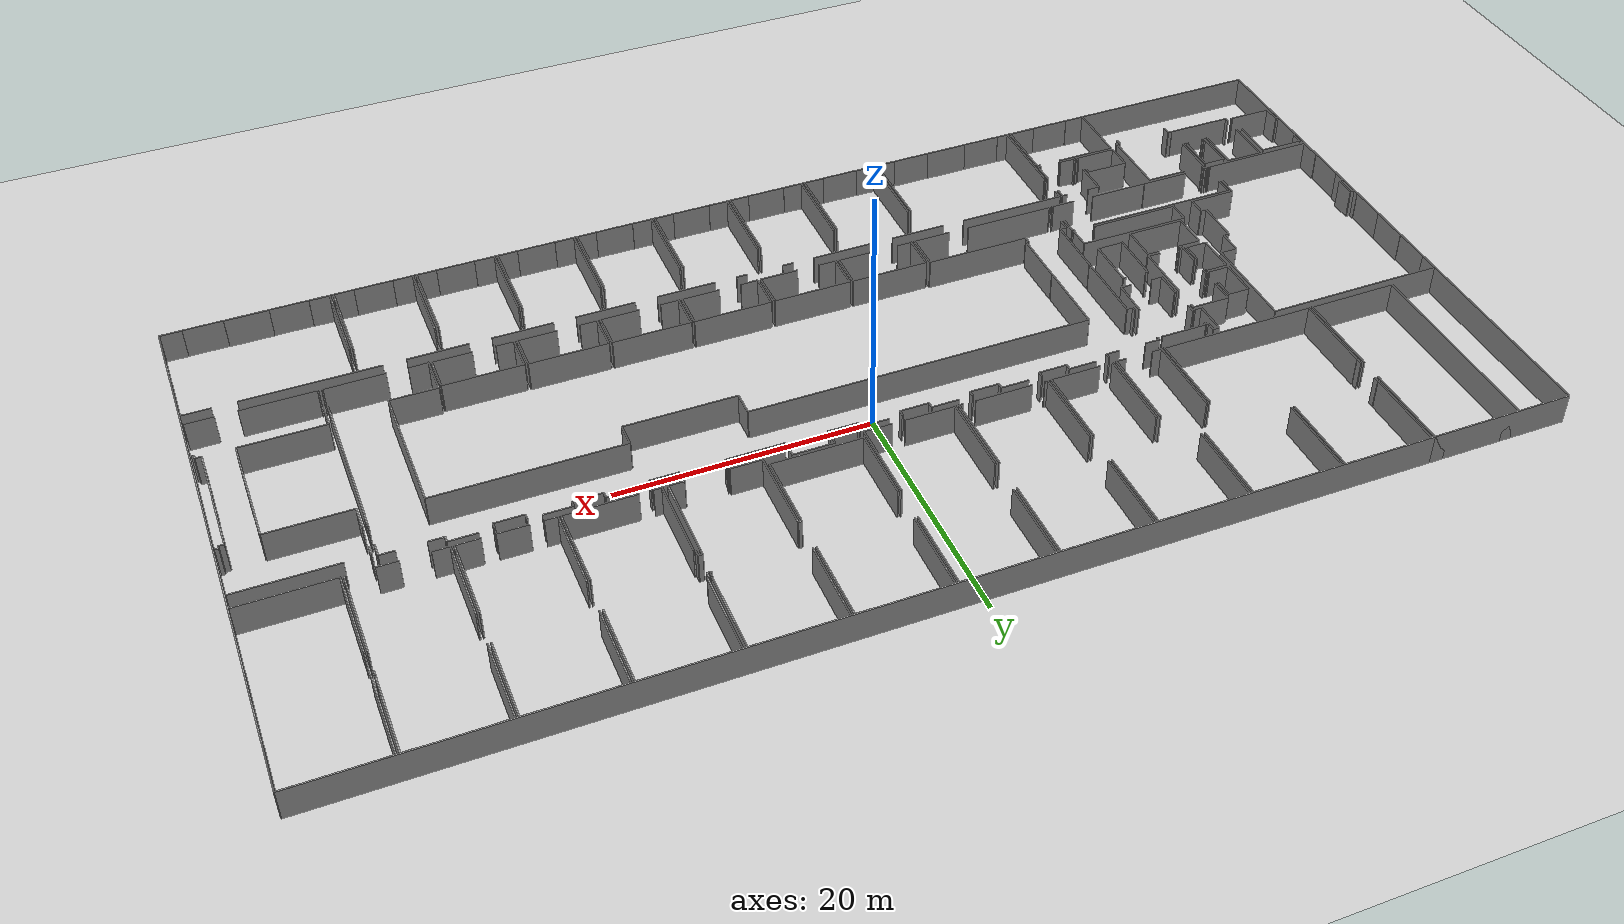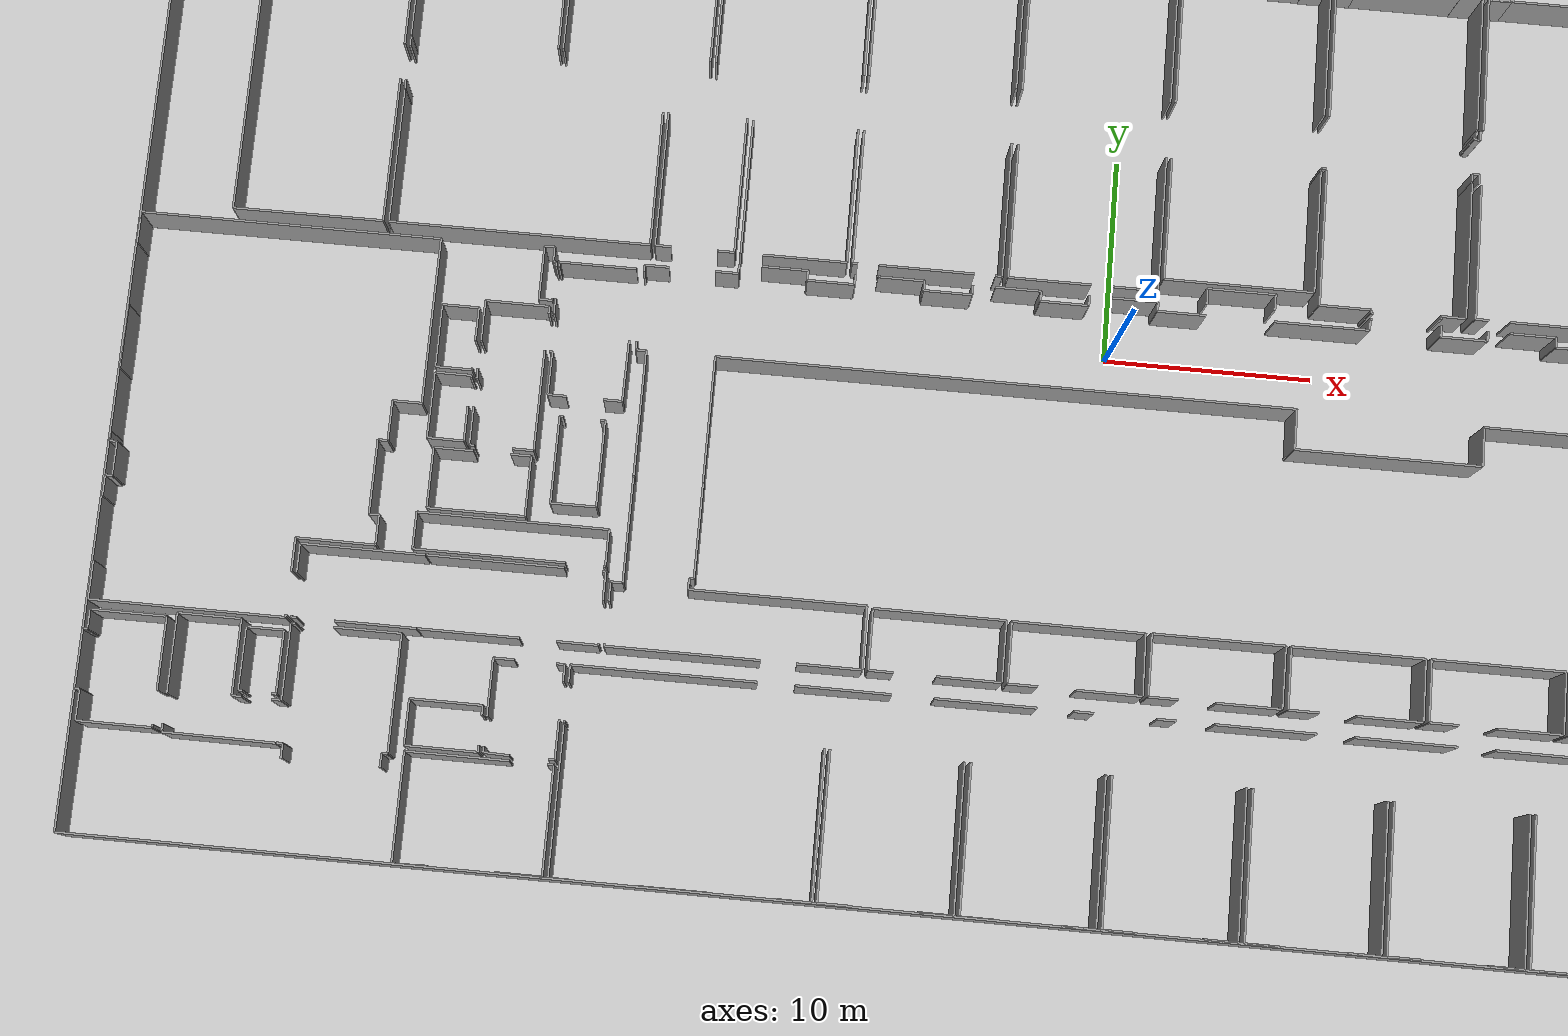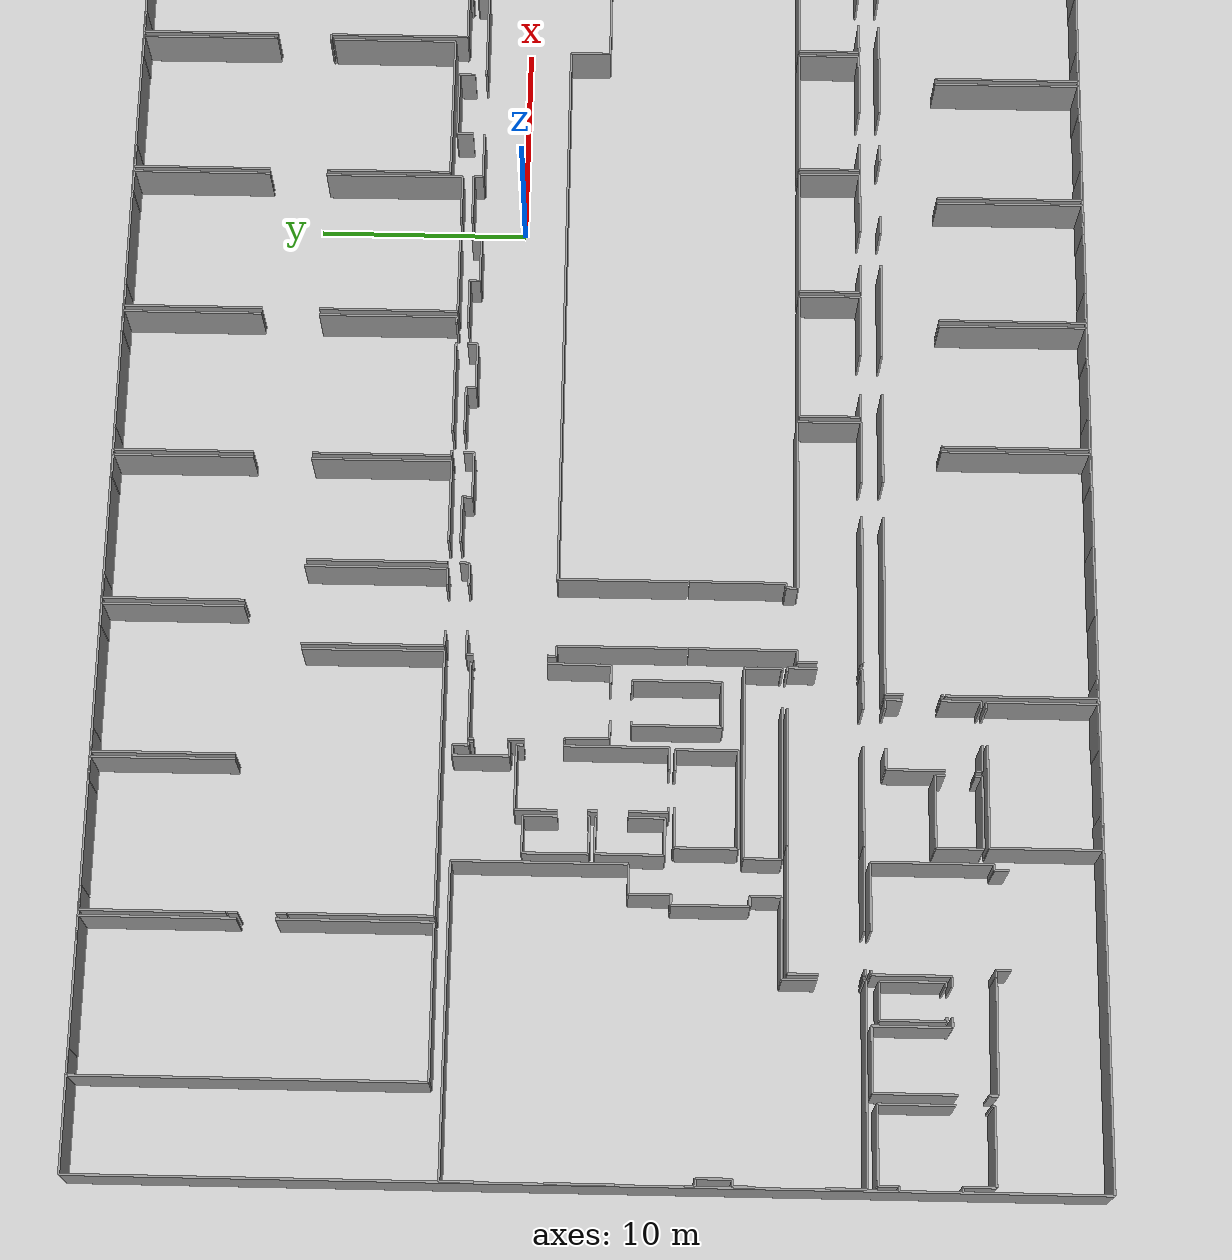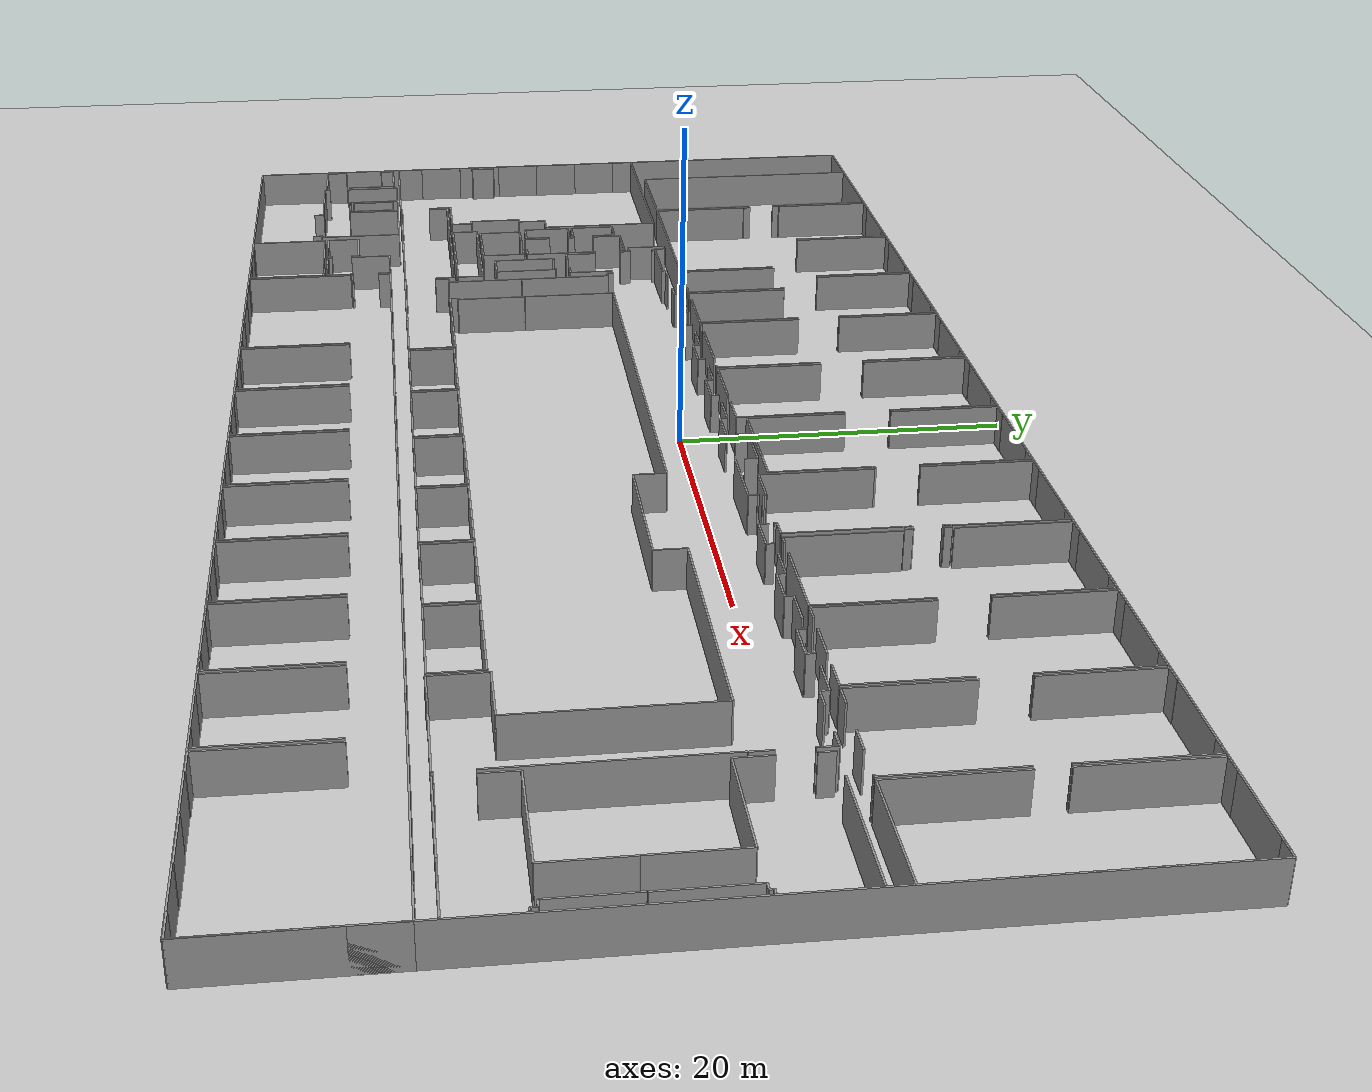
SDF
<sdf version="1.6">
  <world name="default">
    <light name="sun" type="directional">
      <cast_shadows>1</cast_shadows>
      <pose frame="">0 0 10 0 -0 0</pose>
      <diffuse>0.8 0.8 0.8 1</diffuse>
      <specular>0.1 0.1 0.1 1</specular>
      <attenuation>
        <range>1000</range>
        <constant>0.9</constant>
        <linear>0.01</linear>
        <quadratic>0.001</quadratic>
      </attenuation>
      <direction>-0.5 0.5 -1</direction>
    </light>
    <model name="ground_plane">
      <static>1</static>
      <link name="link">
        <collision name="collision">
          <geometry>
            <plane>
              <normal>0 0 1</normal>
              <size>100 100</size>
            </plane>
          </geometry>
          <surface>
            <friction>
              <ode>
                <mu>100</mu>
                <mu2>50</mu2>
              </ode>
              <torsional>
                <ode />
              </torsional>
            </friction>
            <contact>
              <ode />
            </contact>
            <bounce />
          </surface>
          <max_contacts>10</max_contacts>
        </collision>
        <visual name="visual">
          <cast_shadows>0</cast_shadows>
          <geometry>
            <plane>
              <normal>0 0 1</normal>
              <size>100 100</size>
            </plane>
          </geometry>
          <material>
            <script>
              <uri>file://media/materials/scripts/gazebo.material</uri>
              <name>Gazebo/Grey</name>
            </script>
          </material>
        </visual>
        <self_collide>0</self_collide>
        <kinematic>0</kinematic>
        <gravity>1</gravity>
      </link>
    </model>
    <gravity>0 0 -9.8</gravity>
    <magnetic_field>6e-06 2.3e-05 -4.2e-05</magnetic_field>
    <atmosphere type="adiabatic" />
    <physics default="0" name="default_physics" type="ode">
      <max_step_size>0.001</max_step_size>
      <real_time_factor>1</real_time_factor>
      <real_time_update_rate>1000</real_time_update_rate>
    </physics>
    <scene>
      <ambient>0.4 0.4 0.4 1</ambient>
      <background>0.7 0.7 0.7 1</background>
      <shadows>1</shadows>
    </scene>
    <spherical_coordinates>
      <surface_model>EARTH_WGS84</surface_model>
      <latitude_deg>0</latitude_deg>
      <longitude_deg>0</longitude_deg>
      <elevation>0</elevation>
      <heading_deg>0</heading_deg>
    </spherical_coordinates>
  <model name="50045233">
		<static>1</static>
		<link name="Wall_0">
			<collision name="Wall_0_Collision">
				<geometry>
					<box>
						<size>16.1222042448 0.1 2.5</size>
					</box>
				</geometry>
				<pose frame="">8.06110212239 0 1.25 0 0 0</pose>
			</collision>
			<visual name="Wall_0_Visual">
				<pose frame="">8.06110212239 0 1.25 0 0 0</pose>
				<geometry>
					<box>
						<size>16.1222042448 0.1 2.5</size>
					</box>
				</geometry>
				<material>
					<script>
						<uri>file://media/materials/scripts/gazebo.material</uri>
						<name>Gazebo/Grey</name>
					</script>
					<ambient>1 1 1 1</ambient>
				</material>
			</visual>
			<pose frame="">4.38171377812 -16.1222042448 0 0 0 1.57079632679</pose>
		</link>
		<link name="Wall_1">
			<collision name="Wall_1_Collision">
				<geometry>
					<box>
						<size>1.19755083912 0.1 2.5</size>
					</box>
				</geometry>
				<pose frame="">0.598775419562 0 1.25 0 0 0</pose>
			</collision>
			<visual name="Wall_1_Visual">
				<pose frame="">0.598775419562 0 1.25 0 0 0</pose>
				<geometry>
					<box>
						<size>1.19755083912 0.1 2.5</size>
					</box>
				</geometry>
				<material>
					<script>
						<uri>file://media/materials/scripts/gazebo.material</uri>
						<name>Gazebo/Grey</name>
					</script>
					<ambient>1 1 1 1</ambient>
				</material>
			</visual>
			<pose frame="">4.38171377812 -0.0 0 0 0 0.0</pose>
		</link>
		<link name="Wall_2">
			<collision name="Wall_2_Collision">
				<geometry>
					<box>
						<size>1.13232448209 0.1 2.5</size>
					</box>
				</geometry>
				<pose frame="">0.566162241046 0 1.25 0 0 0</pose>
			</collision>
			<visual name="Wall_2_Visual">
				<pose frame="">0.566162241046 0 1.25 0 0 0</pose>
				<geometry>
					<box>
						<size>1.13232448209 0.1 2.5</size>
					</box>
				</geometry>
				<material>
					<script>
						<uri>file://media/materials/scripts/gazebo.material</uri>
						<name>Gazebo/Grey</name>
					</script>
					<ambient>1 1 1 1</ambient>
				</material>
			</visual>
			<pose frame="">10.4920529171 -0.0 0 0 0 0.0</pose>
		</link>
		<link name="Wall_3">
			<collision name="Wall_3_Collision">
				<geometry>
					<box>
						<size>7.14850417182 0.1 2.5</size>
					</box>
				</geometry>
				<pose frame="">3.57425208591 0 1.25 0 0 0</pose>
			</collision>
			<visual name="Wall_3_Visual">
				<pose frame="">3.57425208591 0 1.25 0 0 0</pose>
				<geometry>
					<box>
						<size>7.14850417182 0.1 2.5</size>
					</box>
				</geometry>
				<material>
					<script>
						<uri>file://media/materials/scripts/gazebo.material</uri>
						<name>Gazebo/Grey</name>
					</script>
					<ambient>1 1 1 1</ambient>
				</material>
			</visual>
			<pose frame="">11.6243773992 -0.0 0 0 0 -1.57079632679</pose>
		</link>
		<link name="Wall_4">
			<collision name="Wall_4_Collision">
				<geometry>
					<box>
						<size>7.17109228768 0.1 2.5</size>
					</box>
				</geometry>
				<pose frame="">3.58554614384 0 1.25 0 0 0</pose>
			</collision>
			<visual name="Wall_4_Visual">
				<pose frame="">3.58554614384 0 1.25 0 0 0</pose>
				<geometry>
					<box>
						<size>7.17109228768 0.1 2.5</size>
					</box>
				</geometry>
				<material>
					<script>
						<uri>file://media/materials/scripts/gazebo.material</uri>
						<name>Gazebo/Grey</name>
					</script>
					<ambient>1 1 1 1</ambient>
				</material>
			</visual>
			<pose frame="">11.6243773992 -8.9204022715 0 0 0 -1.57079632679</pose>
		</link>
		<link name="Wall_5">
			<collision name="Wall_5_Collision">
				<geometry>
					<box>
						<size>7.242728727 0.1 2.5</size>
					</box>
				</geometry>
				<pose frame="">3.6213643635 0 1.25 0 0 0</pose>
			</collision>
			<visual name="Wall_5_Visual">
				<pose frame="">3.6213643635 0 1.25 0 0 0</pose>
				<geometry>
					<box>
						<size>7.242728727 0.1 2.5</size>
					</box>
				</geometry>
				<material>
					<script>
						<uri>file://media/materials/scripts/gazebo.material</uri>
						<name>Gazebo/Grey</name>
					</script>
					<ambient>1 1 1 1</ambient>
				</material>
			</visual>
			<pose frame="">11.6243773992 -16.0914945592 0 0 0 -3.13735256967</pose>
		</link>
		<link name="Wall_6">
			<collision name="Wall_6_Collision">
				<geometry>
					<box>
						<size>0.472573839662 0.1 2.5</size>
					</box>
				</geometry>
				<pose frame="">0.236286919831 0 1.25 0 0 0</pose>
			</collision>
			<visual name="Wall_6_Visual">
				<pose frame="">0.236286919831 0 1.25 0 0 0</pose>
				<geometry>
					<box>
						<size>0.472573839662 0.1 2.5</size>
					</box>
				</geometry>
				<material>
					<script>
						<uri>file://media/materials/scripts/gazebo.material</uri>
						<name>Gazebo/Grey</name>
					</script>
					<ambient>1 1 1 1</ambient>
				</material>
			</visual>
			<pose frame="">11.8937850957 -9.40630056153 0 0 0 1.57079632679</pose>
		</link>
		<link name="Wall_7">
			<collision name="Wall_7_Collision">
				<geometry>
					<box>
						<size>0.449858824276 0.1 2.5</size>
					</box>
				</geometry>
				<pose frame="">0.224929412138 0 1.25 0 0 0</pose>
			</collision>
			<visual name="Wall_7_Visual">
				<pose frame="">0.224929412138 0 1.25 0 0 0</pose>
				<geometry>
					<box>
						<size>0.449858824276 0.1 2.5</size>
					</box>
				</geometry>
				<material>
					<script>
						<uri>file://media/materials/scripts/gazebo.material</uri>
						<name>Gazebo/Grey</name>
					</script>
					<ambient>1 1 1 1</ambient>
				</material>
			</visual>
			<pose frame="">11.8937850957 -7.19139621205 0 0 0 1.57079632679</pose>
		</link>
		<link name="Wall_8">
			<collision name="Wall_8_Collision">
				<geometry>
					<box>
						<size>0.318771612576 0.1 2.5</size>
					</box>
				</geometry>
				<pose frame="">0.159385806288 0 1.25 0 0 0</pose>
			</collision>
			<visual name="Wall_8_Visual">
				<pose frame="">0.159385806288 0 1.25 0 0 0</pose>
				<geometry>
					<box>
						<size>0.318771612576 0.1 2.5</size>
					</box>
				</geometry>
				<material>
					<script>
						<uri>file://media/materials/scripts/gazebo.material</uri>
						<name>Gazebo/Grey</name>
					</script>
					<ambient>1 1 1 1</ambient>
				</material>
			</visual>
			<pose frame="">63.6124488436 -6.74153738777 0 0 0 -1.57079632679</pose>
		</link>
		<link name="Wall_9">
			<collision name="Wall_9_Collision">
				<geometry>
					<box>
						<size>0.105834205768 0.1 2.5</size>
					</box>
				</geometry>
				<pose frame="">0.0529171028838 0 1.25 0 0 0</pose>
			</collision>
			<visual name="Wall_9_Visual">
				<pose frame="">0.0529171028838 0 1.25 0 0 0</pose>
				<geometry>
					<box>
						<size>0.105834205768 0.1 2.5</size>
					</box>
				</geometry>
				<material>
					<script>
						<uri>file://media/materials/scripts/gazebo.material</uri>
						<name>Gazebo/Grey</name>
					</script>
					<ambient>1 1 1 1</ambient>
				</material>
			</visual>
			<pose frame="">63.6124488436 -7.06030900035 0 0 0 3.14159265359</pose>
		</link>
		<link name="Wall_10">
			<collision name="Wall_10_Collision">
				<geometry>
					<box>
						<size>0.126265029663 0.1 2.5</size>
					</box>
				</geometry>
				<pose frame="">0.0631325148314 0 1.25 0 0 0</pose>
			</collision>
			<visual name="Wall_10_Visual">
				<pose frame="">0.0631325148314 0 1.25 0 0 0</pose>
				<geometry>
					<box>
						<size>0.126265029663 0.1 2.5</size>
					</box>
				</geometry>
				<material>
					<script>
						<uri>file://media/materials/scripts/gazebo.material</uri>
						<name>Gazebo/Grey</name>
					</script>
					<ambient>1 1 1 1</ambient>
				</material>
			</visual>
			<pose frame="">63.5066146379 -7.06030900035 0 0 0 -1.57079632679</pose>
		</link>
		<link name="Wall_11">
			<collision name="Wall_11_Collision">
				<geometry>
					<box>
						<size>0.296310396244 0.1 2.5</size>
					</box>
				</geometry>
				<pose frame="">0.148155198122 0 1.25 0 0 0</pose>
			</collision>
			<visual name="Wall_11_Visual">
				<pose frame="">0.148155198122 0 1.25 0 0 0</pose>
				<geometry>
					<box>
						<size>0.296310396244 0.1 2.5</size>
					</box>
				</geometry>
				<material>
					<script>
						<uri>file://media/materials/scripts/gazebo.material</uri>
						<name>Gazebo/Grey</name>
					</script>
					<ambient>1 1 1 1</ambient>
				</material>
			</visual>
			<pose frame="">63.5066146379 -7.18657403001 0 0 0 0.0</pose>
		</link>
		<link name="Wall_12">
			<collision name="Wall_12_Collision">
				<geometry>
					<box>
						<size>0.438945464928 0.1 2.5</size>
					</box>
				</geometry>
				<pose frame="">0.219472732464 0 1.25 0 0 0</pose>
			</collision>
			<visual name="Wall_12_Visual">
				<pose frame="">0.219472732464 0 1.25 0 0 0</pose>
				<geometry>
					<box>
						<size>0.438945464928 0.1 2.5</size>
					</box>
				</geometry>
				<material>
					<script>
						<uri>file://media/materials/scripts/gazebo.material</uri>
						<name>Gazebo/Grey</name>
					</script>
					<ambient>1 1 1 1</ambient>
				</material>
			</visual>
			<pose frame="">63.8029250341 -7.18657403001 0 0 0 1.57079632679</pose>
		</link>
		<link name="Wall_13">
			<collision name="Wall_13_Collision">
				<geometry>
					<box>
						<size>0.412169664668 0.1 2.5</size>
					</box>
				</geometry>
				<pose frame="">0.206084832334 0 1.25 0 0 0</pose>
			</collision>
			<visual name="Wall_13_Visual">
				<pose frame="">0.206084832334 0 1.25 0 0 0</pose>
				<geometry>
					<box>
						<size>0.412169664668 0.1 2.5</size>
					</box>
				</geometry>
				<material>
					<script>
						<uri>file://media/materials/scripts/gazebo.material</uri>
						<name>Gazebo/Grey</name>
					</script>
					<ambient>1 1 1 1</ambient>
				</material>
			</visual>
			<pose frame="">85.9797595254 -6.74762856508 0 0 0 -1.57079632679</pose>
		</link>
		<link name="Wall_14">
			<collision name="Wall_14_Collision">
				<geometry>
					<box>
						<size>7.19850258558 0.1 2.5</size>
					</box>
				</geometry>
				<pose frame="">3.59925129279 0 1.25 0 0 0</pose>
			</collision>
			<visual name="Wall_14_Visual">
				<pose frame="">3.59925129279 0 1.25 0 0 0</pose>
				<geometry>
					<box>
						<size>7.19850258558 0.1 2.5</size>
					</box>
				</geometry>
				<material>
					<script>
						<uri>file://media/materials/scripts/gazebo.material</uri>
						<name>Gazebo/Grey</name>
					</script>
					<ambient>1 1 1 1</ambient>
				</material>
			</visual>
			<pose frame="">85.9797595254 -8.92370165921 0 0 0 -1.57079632679</pose>
		</link>
		<link name="Wall_15">
			<collision name="Wall_15_Collision">
				<geometry>
					<box>
						<size>0.139716379556 0.1 2.5</size>
					</box>
				</geometry>
				<pose frame="">0.0698581897782 0 1.25 0 0 0</pose>
			</collision>
			<visual name="Wall_15_Visual">
				<pose frame="">0.0698581897782 0 1.25 0 0 0</pose>
				<geometry>
					<box>
						<size>0.139716379556 0.1 2.5</size>
					</box>
				</geometry>
				<material>
					<script>
						<uri>file://media/materials/scripts/gazebo.material</uri>
						<name>Gazebo/Grey</name>
					</script>
					<ambient>1 1 1 1</ambient>
				</material>
			</visual>
			<pose frame="">85.9797595254 -16.1222042448 0 0 0 3.14159265359</pose>
		</link>
		<link name="Wall_16">
			<collision name="Wall_16_Collision">
				<geometry>
					<box>
						<size>1.61073570001 0.1 2.5</size>
					</box>
				</geometry>
				<pose frame="">0.805367850005 0 1.25 0 0 0</pose>
			</collision>
			<visual name="Wall_16_Visual">
				<pose frame="">0.805367850005 0 1.25 0 0 0</pose>
				<geometry>
					<box>
						<size>1.61073570001 0.1 2.5</size>
					</box>
				</geometry>
				<material>
					<script>
						<uri>file://media/materials/scripts/gazebo.material</uri>
						<name>Gazebo/Grey</name>
					</script>
					<ambient>1 1 1 1</ambient>
				</material>
			</visual>
			<pose frame="">83.895561689 -16.1222042448 0 0 0 3.14159265359</pose>
		</link>
		<link name="Wall_17">
			<collision name="Wall_17_Collision">
				<geometry>
					<box>
						<size>1.30211604962 0.1 2.5</size>
					</box>
				</geometry>
				<pose frame="">0.651058024809 0 1.25 0 0 0</pose>
			</collision>
			<visual name="Wall_17_Visual">
				<pose frame="">0.651058024809 0 1.25 0 0 0</pose>
				<geometry>
					<box>
						<size>1.30211604962 0.1 2.5</size>
					</box>
				</geometry>
				<material>
					<script>
						<uri>file://media/materials/scripts/gazebo.material</uri>
						<name>Gazebo/Grey</name>
					</script>
					<ambient>1 1 1 1</ambient>
				</material>
			</visual>
			<pose frame="">80.1170013642 -16.1222042448 0 0 0 3.14159265359</pose>
		</link>
		<link name="Wall_18">
			<collision name="Wall_18_Collision">
				<geometry>
					<box>
						<size>6.72021826719 0.1 2.5</size>
					</box>
				</geometry>
				<pose frame="">3.36010913359 0 1.25 0 0 0</pose>
			</collision>
			<visual name="Wall_18_Visual">
				<pose frame="">3.36010913359 0 1.25 0 0 0</pose>
				<geometry>
					<box>
						<size>6.72021826719 0.1 2.5</size>
					</box>
				</geometry>
				<material>
					<script>
						<uri>file://media/materials/scripts/gazebo.material</uri>
						<name>Gazebo/Grey</name>
					</script>
					<ambient>1 1 1 1</ambient>
				</material>
			</visual>
			<pose frame="">78.8148853146 -16.1222042448 0 0 0 1.57079632679</pose>
		</link>
		<link name="Wall_19">
			<collision name="Wall_19_Collision">
				<geometry>
					<box>
						<size>0.479045715555 0.1 2.5</size>
					</box>
				</geometry>
				<pose frame="">0.239522857777 0 1.25 0 0 0</pose>
			</collision>
			<visual name="Wall_19_Visual">
				<pose frame="">0.239522857777 0 1.25 0 0 0</pose>
				<geometry>
					<box>
						<size>0.479045715555 0.1 2.5</size>
					</box>
				</geometry>
				<material>
					<script>
						<uri>file://media/materials/scripts/gazebo.material</uri>
						<name>Gazebo/Grey</name>
					</script>
					<ambient>1 1 1 1</ambient>
				</material>
			</visual>
			<pose frame="">63.8205640684 -9.4019859776 0 0 0 1.57079632679</pose>
		</link>
		<link name="Wall_20">
			<collision name="Wall_20_Collision">
				<geometry>
					<box>
						<size>0.324735890359 0.1 2.5</size>
					</box>
				</geometry>
				<pose frame="">0.162367945179 0 1.25 0 0 0</pose>
			</collision>
			<visual name="Wall_20_Visual">
				<pose frame="">0.162367945179 0 1.25 0 0 0</pose>
				<geometry>
					<box>
						<size>0.324735890359 0.1 2.5</size>
					</box>
				</geometry>
				<material>
					<script>
						<uri>file://media/materials/scripts/gazebo.material</uri>
						<name>Gazebo/Grey</name>
					</script>
					<ambient>1 1 1 1</ambient>
				</material>
			</visual>
			<pose frame="">63.8205640684 -8.92294026205 0 0 0 3.14159265359</pose>
		</link>
		<link name="Wall_21">
			<collision name="Wall_21_Collision">
				<geometry>
					<box>
						<size>0.393134735573 0.1 2.5</size>
					</box>
				</geometry>
				<pose frame="">0.196567367787 0 1.25 0 0 0</pose>
			</collision>
			<visual name="Wall_21_Visual">
				<pose frame="">0.196567367787 0 1.25 0 0 0</pose>
				<geometry>
					<box>
						<size>0.393134735573 0.1 2.5</size>
					</box>
				</geometry>
				<material>
					<script>
						<uri>file://media/materials/scripts/gazebo.material</uri>
						<name>Gazebo/Grey</name>
					</script>
					<ambient>1 1 1 1</ambient>
				</material>
			</visual>
			<pose frame="">63.495828178 -8.92294026205 0 0 0 -1.57079632679</pose>
		</link>
		<link name="Wall_22">
			<collision name="Wall_22_Collision">
				<geometry>
					<box>
						<size>0.252276260271 0.1 2.5</size>
					</box>
				</geometry>
				<pose frame="">0.126138130135 0 1.25 0 0 0</pose>
			</collision>
			<visual name="Wall_22_Visual">
				<pose frame="">0.126138130135 0 1.25 0 0 0</pose>
				<geometry>
					<box>
						<size>0.252276260271 0.1 2.5</size>
					</box>
				</geometry>
				<material>
					<script>
						<uri>file://media/materials/scripts/gazebo.material</uri>
						<name>Gazebo/Grey</name>
					</script>
					<ambient>1 1 1 1</ambient>
				</material>
			</visual>
			<pose frame="">56.4897052758 -9.31607499762 0 0 0 3.14159265359</pose>
		</link>
		<link name="Wall_23">
			<collision name="Wall_23_Collision">
				<geometry>
					<box>
						<size>0.0649725579772 0.1 2.5</size>
					</box>
				</geometry>
				<pose frame="">0.0324862789886 0 1.25 0 0 0</pose>
			</collision>
			<visual name="Wall_23_Visual">
				<pose frame="">0.0324862789886 0 1.25 0 0 0</pose>
				<geometry>
					<box>
						<size>0.0649725579772 0.1 2.5</size>
					</box>
				</geometry>
				<material>
					<script>
						<uri>file://media/materials/scripts/gazebo.material</uri>
						<name>Gazebo/Grey</name>
					</script>
					<ambient>1 1 1 1</ambient>
				</material>
			</visual>
			<pose frame="">56.2374290156 -9.31607499762 0 0 0 -1.57079632679</pose>
		</link>
		<link name="Wall_24">
			<collision name="Wall_24_Collision">
				<geometry>
					<box>
						<size>6.72009136766 0.1 2.5</size>
					</box>
				</geometry>
				<pose frame="">3.36004568383 0 1.25 0 0 0</pose>
			</collision>
			<visual name="Wall_24_Visual">
				<pose frame="">3.36004568383 0 1.25 0 0 0</pose>
				<geometry>
					<box>
						<size>6.72009136766 0.1 2.5</size>
					</box>
				</geometry>
				<material>
					<script>
						<uri>file://media/materials/scripts/gazebo.material</uri>
						<name>Gazebo/Grey</name>
					</script>
					<ambient>1 1 1 1</ambient>
				</material>
			</visual>
			<pose frame="">28.5239681482 -9.3810475556 0 0 0 -1.57079632679</pose>
		</link>
		<link name="Wall_25">
			<collision name="Wall_25_Collision">
				<geometry>
					<box>
						<size>0.815075663843 0.1 2.5</size>
					</box>
				</geometry>
				<pose frame="">0.407537831922 0 1.25 0 0 0</pose>
			</collision>
			<visual name="Wall_25_Visual">
				<pose frame="">0.407537831922 0 1.25 0 0 0</pose>
				<geometry>
					<box>
						<size>0.815075663843 0.1 2.5</size>
					</box>
				</geometry>
				<material>
					<script>
						<uri>file://media/materials/scripts/gazebo.material</uri>
						<name>Gazebo/Grey</name>
					</script>
					<ambient>1 1 1 1</ambient>
				</material>
			</visual>
			<pose frame="">28.5239681482 -16.1011389233 0 0 0 3.14159265359</pose>
		</link>
		<link name="Wall_26">
			<collision name="Wall_26_Collision">
				<geometry>
					<box>
						<size>0.767615240633 0.1 2.5</size>
					</box>
				</geometry>
				<pose frame="">0.383807620317 0 1.25 0 0 0</pose>
			</collision>
			<visual name="Wall_26_Visual">
				<pose frame="">0.383807620317 0 1.25 0 0 0</pose>
				<geometry>
					<box>
						<size>0.767615240633 0.1 2.5</size>
					</box>
				</geometry>
				<material>
					<script>
						<uri>file://media/materials/scripts/gazebo.material</uri>
						<name>Gazebo/Grey</name>
					</script>
					<ambient>1 1 1 1</ambient>
				</material>
			</visual>
			<pose frame="">25.4801560864 -16.1011389233 0 0 0 3.14159265359</pose>
		</link>
		<link name="Wall_27">
			<collision name="Wall_27_Collision">
				<geometry>
					<box>
						<size>6.68811268678 0.1 2.5</size>
					</box>
				</geometry>
				<pose frame="">3.34405634339 0 1.25 0 0 0</pose>
			</collision>
			<visual name="Wall_27_Visual">
				<pose frame="">3.34405634339 0 1.25 0 0 0</pose>
				<geometry>
					<box>
						<size>6.68811268678 0.1 2.5</size>
					</box>
				</geometry>
				<material>
					<script>
						<uri>file://media/materials/scripts/gazebo.material</uri>
						<name>Gazebo/Grey</name>
					</script>
					<ambient>1 1 1 1</ambient>
				</material>
			</visual>
			<pose frame="">24.7125408458 -16.1011389233 0 0 0 1.57079632679</pose>
		</link>
		<link name="Wall_28">
			<collision name="Wall_28_Collision">
				<geometry>
					<box>
						<size>6.65829129786 0.1 2.5</size>
					</box>
				</geometry>
				<pose frame="">3.32914564893 0 1.25 0 0 0</pose>
			</collision>
			<visual name="Wall_28_Visual">
				<pose frame="">3.32914564893 0 1.25 0 0 0</pose>
				<geometry>
					<box>
						<size>6.65829129786 0.1 2.5</size>
					</box>
				</geometry>
				<material>
					<script>
						<uri>file://media/materials/scripts/gazebo.material</uri>
						<name>Gazebo/Grey</name>
					</script>
					<ambient>1 1 1 1</ambient>
				</material>
			</visual>
			<pose frame="">11.8845214302 -6.66882395863 0 0 0 1.57079632679</pose>
		</link>
		<link name="Wall_29">
			<collision name="Wall_29_Collision">
				<geometry>
					<box>
						<size>1.1096094667 0.1 2.5</size>
					</box>
				</geometry>
				<pose frame="">0.554804733352 0 1.25 0 0 0</pose>
			</collision>
			<visual name="Wall_29_Visual">
				<pose frame="">0.554804733352 0 1.25 0 0 0</pose>
				<geometry>
					<box>
						<size>1.1096094667 0.1 2.5</size>
					</box>
				</geometry>
				<material>
					<script>
						<uri>file://media/materials/scripts/gazebo.material</uri>
						<name>Gazebo/Grey</name>
					</script>
					<ambient>1 1 1 1</ambient>
				</material>
			</visual>
			<pose frame="">11.8845214302 -0.0105326607658 0 0 0 0.0</pose>
		</link>
		<link name="Wall_30">
			<collision name="Wall_30_Collision">
				<geometry>
					<box>
						<size>1.15770438755 0.1 2.5</size>
					</box>
				</geometry>
				<pose frame="">0.578852193776 0 1.25 0 0 0</pose>
			</collision>
			<visual name="Wall_30_Visual">
				<pose frame="">0.578852193776 0 1.25 0 0 0</pose>
				<geometry>
					<box>
						<size>1.15770438755 0.1 2.5</size>
					</box>
				</geometry>
				<material>
					<script>
						<uri>file://media/materials/scripts/gazebo.material</uri>
						<name>Gazebo/Grey</name>
					</script>
					<ambient>1 1 1 1</ambient>
				</material>
			</visual>
			<pose frame="">17.9051426033 -0.0105326607658 0 0 0 0.0</pose>
		</link>
		<link name="Wall_31">
			<collision name="Wall_31_Collision">
				<geometry>
					<box>
						<size>6.65831333697 0.1 2.5</size>
					</box>
				</geometry>
				<pose frame="">3.32915666849 0 1.25 0 0 0</pose>
			</collision>
			<visual name="Wall_31_Visual">
				<pose frame="">3.32915666849 0 1.25 0 0 0</pose>
				<geometry>
					<box>
						<size>6.65831333697 0.1 2.5</size>
					</box>
				</geometry>
				<material>
					<script>
						<uri>file://media/materials/scripts/gazebo.material</uri>
						<name>Gazebo/Grey</name>
					</script>
					<ambient>1 1 1 1</ambient>
				</material>
			</visual>
			<pose frame="">19.0628469909 -0.0105326607658 0 0 0 -1.56822338464</pose>
		</link>
		<link name="Wall_32">
			<collision name="Wall_32_Collision">
				<geometry>
					<box>
						<size>6.6463627423 0.1 2.5</size>
					</box>
				</geometry>
				<pose frame="">3.32318137115 0 1.25 0 0 0</pose>
			</collision>
			<visual name="Wall_32_Visual">
				<pose frame="">3.32318137115 0 1.25 0 0 0</pose>
				<geometry>
					<box>
						<size>6.6463627423 0.1 2.5</size>
					</box>
				</geometry>
				<material>
					<script>
						<uri>file://media/materials/scripts/gazebo.material</uri>
						<name>Gazebo/Grey</name>
					</script>
					<ambient>1 1 1 1</ambient>
				</material>
			</visual>
			<pose frame="">19.3103010691 -6.6617175851 0 0 0 1.57079632679</pose>
		</link>
		<link name="Wall_33">
			<collision name="Wall_33_Collision">
				<geometry>
					<box>
						<size>1.12115732369 0.1 2.5</size>
					</box>
				</geometry>
				<pose frame="">0.560578661844 0 1.25 0 0 0</pose>
			</collision>
			<visual name="Wall_33_Visual">
				<pose frame="">0.560578661844 0 1.25 0 0 0</pose>
				<geometry>
					<box>
						<size>1.12115732369 0.1 2.5</size>
					</box>
				</geometry>
				<material>
					<script>
						<uri>file://media/materials/scripts/gazebo.material</uri>
						<name>Gazebo/Grey</name>
					</script>
					<ambient>1 1 1 1</ambient>
				</material>
			</visual>
			<pose frame="">19.3103010691 -0.0153548428032 0 0 0 0.0</pose>
		</link>
		<link name="Wall_34">
			<collision name="Wall_34_Collision">
				<geometry>
					<box>
						<size>1.11151295961 0.1 2.5</size>
					</box>
				</geometry>
				<pose frame="">0.555756479807 0 1.25 0 0 0</pose>
			</collision>
			<visual name="Wall_34_Visual">
				<pose frame="">0.555756479807 0 1.25 0 0 0</pose>
				<geometry>
					<box>
						<size>1.11151295961 0.1 2.5</size>
					</box>
				</geometry>
				<material>
					<script>
						<uri>file://media/materials/scripts/gazebo.material</uri>
						<name>Gazebo/Grey</name>
					</script>
					<ambient>1 1 1 1</ambient>
				</material>
			</visual>
			<pose frame="">25.369119 -0.0153548428032 0 0 0 0.0</pose>
		</link>
		<link name="Wall_35">
			<collision name="Wall_35_Collision">
				<geometry>
					<box>
						<size>6.64636305243 0.1 2.5</size>
					</box>
				</geometry>
				<pose frame="">3.32318152622 0 1.25 0 0 0</pose>
			</collision>
			<visual name="Wall_35_Visual">
				<pose frame="">3.32318152622 0 1.25 0 0 0</pose>
				<geometry>
					<box>
						<size>6.64636305243 0.1 2.5</size>
					</box>
				</geometry>
				<material>
					<script>
						<uri>file://media/materials/scripts/gazebo.material</uri>
						<name>Gazebo/Grey</name>
					</script>
					<ambient>1 1 1 1</ambient>
				</material>
			</visual>
			<pose frame="">26.4806319596 -0.0153548428032 0 0 0 -1.57049083754</pose>
		</link>
		<link name="Wall_36">
			<collision name="Wall_36_Collision">
				<geometry>
					<box>
						<size>6.66260588179 0.1 2.5</size>
					</box>
				</geometry>
				<pose frame="">3.3313029409 0 1.25 0 0 0</pose>
			</collision>
			<visual name="Wall_36_Visual">
				<pose frame="">3.3313029409 0 1.25 0 0 0</pose>
				<geometry>
					<box>
						<size>6.66260588179 0.1 2.5</size>
					</box>
				</geometry>
				<material>
					<script>
						<uri>file://media/materials/scripts/gazebo.material</uri>
						<name>Gazebo/Grey</name>
					</script>
					<ambient>1 1 1 1</ambient>
				</material>
			</visual>
			<pose frame="">26.7620951112 -6.68747818914 0 0 0 1.57079632679</pose>
		</link>
		<link name="Wall_37">
			<collision name="Wall_37_Collision">
				<geometry>
					<box>
						<size>1.1068176771 0.1 2.5</size>
					</box>
				</geometry>
				<pose frame="">0.553408838552 0 1.25 0 0 0</pose>
			</collision>
			<visual name="Wall_37_Visual">
				<pose frame="">0.553408838552 0 1.25 0 0 0</pose>
				<geometry>
					<box>
						<size>1.1068176771 0.1 2.5</size>
					</box>
				</geometry>
				<material>
					<script>
						<uri>file://media/materials/scripts/gazebo.material</uri>
						<name>Gazebo/Grey</name>
					</script>
					<ambient>1 1 1 1</ambient>
				</material>
			</visual>
			<pose frame="">26.7620951112 -0.0248723073507 0 0 0 0.0</pose>
		</link>
		<link name="Wall_38">
			<collision name="Wall_38_Collision">
				<geometry>
					<box>
						<size>1.14970971733 0.1 2.5</size>
					</box>
				</geometry>
				<pose frame="">0.574854858666 0 1.25 0 0 0</pose>
			</collision>
			<visual name="Wall_38_Visual">
				<pose frame="">0.574854858666 0 1.25 0 0 0</pose>
				<geometry>
					<box>
						<size>1.14970971733 0.1 2.5</size>
					</box>
				</geometry>
				<material>
					<script>
						<uri>file://media/materials/scripts/gazebo.material</uri>
						<name>Gazebo/Grey</name>
					</script>
					<ambient>1 1 1 1</ambient>
				</material>
			</visual>
			<pose frame="">32.7683766378 -0.0248723073507 0 0 0 0.0</pose>
		</link>
		<link name="Wall_39">
			<collision name="Wall_39_Collision">
				<geometry>
					<box>
						<size>6.66267148961 0.1 2.5</size>
					</box>
				</geometry>
				<pose frame="">3.33133574481 0 1.25 0 0 0</pose>
			</collision>
			<visual name="Wall_39_Visual">
				<pose frame="">3.33133574481 0 1.25 0 0 0</pose>
				<geometry>
					<box>
						<size>6.66267148961 0.1 2.5</size>
					</box>
				</geometry>
				<material>
					<script>
						<uri>file://media/materials/scripts/gazebo.material</uri>
						<name>Gazebo/Grey</name>
					</script>
					<ambient>1 1 1 1</ambient>
				</material>
			</visual>
			<pose frame="">33.9180863551 -0.0248723073507 0 0 0 -1.56635851428</pose>
		</link>
		<link name="Wall_40">
			<collision name="Wall_40_Collision">
				<geometry>
					<box>
						<size>6.66019479077 0.1 2.5</size>
					</box>
				</geometry>
				<pose frame="">3.33009739539 0 1.25 0 0 0</pose>
			</collision>
			<visual name="Wall_40_Visual">
				<pose frame="">3.33009739539 0 1.25 0 0 0</pose>
				<geometry>
					<box>
						<size>6.66019479077 0.1 2.5</size>
					</box>
				</geometry>
				<material>
					<script>
						<uri>file://media/materials/scripts/gazebo.material</uri>
						<name>Gazebo/Grey</name>
					</script>
					<ambient>1 1 1 1</ambient>
				</material>
			</visual>
			<pose frame="">34.1938390279 -6.67593033216 0 0 0 1.57079632679</pose>
		</link>
		<link name="Wall_41">
			<collision name="Wall_41_Collision">
				<geometry>
					<box>
						<size>1.11874623267 0.1 2.5</size>
					</box>
				</geometry>
				<pose frame="">0.559373116335 0 1.25 0 0 0</pose>
			</collision>
			<visual name="Wall_41_Visual">
				<pose frame="">0.559373116335 0 1.25 0 0 0</pose>
				<geometry>
					<box>
						<size>1.11874623267 0.1 2.5</size>
					</box>
				</geometry>
				<material>
					<script>
						<uri>file://media/materials/scripts/gazebo.material</uri>
						<name>Gazebo/Grey</name>
					</script>
					<ambient>1 1 1 1</ambient>
				</material>
			</visual>
			<pose frame="">34.1938390279 -0.0157355413851 0 0 0 0.0</pose>
		</link>
		<link name="Wall_42">
			<collision name="Wall_42_Collision">
				<geometry>
					<box>
						<size>1.11735033787 0.1 2.5</size>
					</box>
				</geometry>
				<pose frame="">0.558675168935 0 1.25 0 0 0</pose>
			</collision>
			<visual name="Wall_42_Visual">
				<pose frame="">0.558675168935 0 1.25 0 0 0</pose>
				<geometry>
					<box>
						<size>1.11735033787 0.1 2.5</size>
					</box>
				</geometry>
				<material>
					<script>
						<uri>file://media/materials/scripts/gazebo.material</uri>
						<name>Gazebo/Grey</name>
					</script>
					<ambient>1 1 1 1</ambient>
				</material>
			</visual>
			<pose frame="">40.2318454364 -0.0157355413851 0 0 0 0.0</pose>
		</link>
		<link name="Wall_43">
			<collision name="Wall_43_Collision">
				<geometry>
					<box>
						<size>6.6601948343 0.1 2.5</size>
					</box>
				</geometry>
				<pose frame="">3.33009741715 0 1.25 0 0 0</pose>
			</collision>
			<visual name="Wall_43_Visual">
				<pose frame="">3.33009741715 0 1.25 0 0 0</pose>
				<geometry>
					<box>
						<size>6.6601948343 0.1 2.5</size>
					</box>
				</geometry>
				<material>
					<script>
						<uri>file://media/materials/scripts/gazebo.material</uri>
						<name>Gazebo/Grey</name>
					</script>
					<ambient>1 1 1 1</ambient>
				</material>
			</visual>
			<pose frame="">41.3491957742 -0.0157355413851 0 0 0 -1.57091064735</pose>
		</link>
		<link name="Wall_44">
			<collision name="Wall_44_Collision">
				<geometry>
					<box>
						<size>6.65461121157 0.1 2.5</size>
					</box>
				</geometry>
				<pose frame="">3.32730560579 0 1.25 0 0 0</pose>
			</collision>
			<visual name="Wall_44_Visual">
				<pose frame="">3.32730560579 0 1.25 0 0 0</pose>
				<geometry>
					<box>
						<size>6.65461121157 0.1 2.5</size>
					</box>
				</geometry>
				<material>
					<script>
						<uri>file://media/materials/scripts/gazebo.material</uri>
						<name>Gazebo/Grey</name>
					</script>
					<ambient>1 1 1 1</ambient>
				</material>
			</visual>
			<pose frame="">41.6330700168 -6.67618413121 0 0 0 1.57079632679</pose>
		</link>
		<link name="Wall_45">
			<collision name="Wall_45_Collision">
				<geometry>
					<box>
						<size>1.10275689223 0.1 2.5</size>
					</box>
				</geometry>
				<pose frame="">0.551378446115 0 1.25 0 0 0</pose>
			</collision>
			<visual name="Wall_45_Visual">
				<pose frame="">0.551378446115 0 1.25 0 0 0</pose>
				<geometry>
					<box>
						<size>1.10275689223 0.1 2.5</size>
					</box>
				</geometry>
				<material>
					<script>
						<uri>file://media/materials/scripts/gazebo.material</uri>
						<name>Gazebo/Grey</name>
					</script>
					<ambient>1 1 1 1</ambient>
				</material>
			</visual>
			<pose frame="">41.6330700168 -0.0215729196409 0 0 0 0.0</pose>
		</link>
		<link name="Wall_46">
			<collision name="Wall_46_Collision">
				<geometry>
					<box>
						<size>1.16316106723 0.1 2.5</size>
					</box>
				</geometry>
				<pose frame="">0.581580533613 0 1.25 0 0 0</pose>
			</collision>
			<visual name="Wall_46_Visual">
				<pose frame="">0.581580533613 0 1.25 0 0 0</pose>
				<geometry>
					<box>
						<size>1.16316106723 0.1 2.5</size>
					</box>
				</geometry>
				<material>
					<script>
						<uri>file://media/materials/scripts/gazebo.material</uri>
						<name>Gazebo/Grey</name>
					</script>
					<ambient>1 1 1 1</ambient>
				</material>
			</visual>
			<pose frame="">47.6459503188 -0.0215729196409 0 0 0 0.0</pose>
		</link>
		<link name="Wall_47">
			<collision name="Wall_47_Collision">
				<geometry>
					<box>
						<size>6.6546139993 0.1 2.5</size>
					</box>
				</geometry>
				<pose frame="">3.32730699965 0 1.25 0 0 0</pose>
			</collision>
			<visual name="Wall_47_Visual">
				<pose frame="">3.32730699965 0 1.25 0 0 0</pose>
				<geometry>
					<box>
						<size>6.6546139993 0.1 2.5</size>
					</box>
				</geometry>
				<material>
					<script>
						<uri>file://media/materials/scripts/gazebo.material</uri>
						<name>Gazebo/Grey</name>
					</script>
					<ambient>1 1 1 1</ambient>
				</material>
			</visual>
			<pose frame="">48.8091113861 -0.0215729196409 0 0 0 -1.56988099524</pose>
		</link>
		<link name="Wall_48">
			<collision name="Wall_48_Collision">
				<geometry>
					<box>
						<size>6.63468798579 0.1 2.5</size>
					</box>
				</geometry>
				<pose frame="">3.31734399289 0 1.25 0 0 0</pose>
			</collision>
			<visual name="Wall_48_Visual">
				<pose frame="">3.31734399289 0 1.25 0 0 0</pose>
				<geometry>
					<box>
						<size>6.63468798579 0.1 2.5</size>
					</box>
				</geometry>
				<material>
					<script>
						<uri>file://media/materials/scripts/gazebo.material</uri>
						<name>Gazebo/Grey</name>
					</script>
					<ambient>1 1 1 1</ambient>
				</material>
			</visual>
			<pose frame="">49.0613876463 -6.6617175851 0 0 0 1.57079632679</pose>
		</link>
		<link name="Wall_49">
			<collision name="Wall_49_Collision">
				<geometry>
					<box>
						<size>1.13016719013 0.1 2.5</size>
					</box>
				</geometry>
				<pose frame="">0.565083595064 0 1.25 0 0 0</pose>
			</collision>
			<visual name="Wall_49_Visual">
				<pose frame="">0.565083595064 0 1.25 0 0 0</pose>
				<geometry>
					<box>
						<size>1.13016719013 0.1 2.5</size>
					</box>
				</geometry>
				<material>
					<script>
						<uri>file://media/materials/scripts/gazebo.material</uri>
						<name>Gazebo/Grey</name>
					</script>
					<ambient>1 1 1 1</ambient>
				</material>
			</visual>
			<pose frame="">49.0613876463 -0.0270295993147 0 0 0 0.0</pose>
		</link>
		<link name="Wall_50">
			<collision name="Wall_50_Collision">
				<geometry>
					<box>
						<size>1.13016719013 0.1 2.5</size>
					</box>
				</geometry>
				<pose frame="">0.565083595064 0 1.25 0 0 0</pose>
			</collision>
			<visual name="Wall_50_Visual">
				<pose frame="">0.565083595064 0 1.25 0 0 0</pose>
				<geometry>
					<box>
						<size>1.13016719013 0.1 2.5</size>
					</box>
				</geometry>
				<material>
					<script>
						<uri>file://media/materials/scripts/gazebo.material</uri>
						<name>Gazebo/Grey</name>
					</script>
					<ambient>1 1 1 1</ambient>
				</material>
			</visual>
			<pose frame="">55.1018051458 -0.0270295993147 0 0 0 0.0</pose>
		</link>
		<link name="Wall_51">
			<collision name="Wall_51_Collision">
				<geometry>
					<box>
						<size>6.63471828161 0.1 2.5</size>
					</box>
				</geometry>
				<pose frame="">3.3173591408 0 1.25 0 0 0</pose>
			</collision>
			<visual name="Wall_51_Visual">
				<pose frame="">3.3173591408 0 1.25 0 0 0</pose>
				<geometry>
					<box>
						<size>6.63471828161 0.1 2.5</size>
					</box>
				</geometry>
				<material>
					<script>
						<uri>file://media/materials/scripts/gazebo.material</uri>
						<name>Gazebo/Grey</name>
					</script>
					<ambient>1 1 1 1</ambient>
				</material>
			</visual>
			<pose frame="">56.2319723359 -0.0270295993147 0 0 0 -1.56777432119</pose>
		</link>
		<link name="Wall_52">
			<collision name="Wall_52_Collision">
				<geometry>
					<box>
						<size>6.67275784398 0.1 2.5</size>
					</box>
				</geometry>
				<pose frame="">3.33637892199 0 1.25 0 0 0</pose>
			</collision>
			<visual name="Wall_52_Visual">
				<pose frame="">3.33637892199 0 1.25 0 0 0</pose>
				<geometry>
					<box>
						<size>6.67275784398 0.1 2.5</size>
					</box>
				</geometry>
				<material>
					<script>
						<uri>file://media/materials/scripts/gazebo.material</uri>
						<name>Gazebo/Grey</name>
					</script>
					<ambient>1 1 1 1</ambient>
				</material>
			</visual>
			<pose frame="">63.6316106723 -6.68417880143 0 0 0 1.57079632679</pose>
		</link>
		<link name="Wall_53">
			<collision name="Wall_53_Collision">
				<geometry>
					<box>
						<size>1.07090511088 0.1 2.5</size>
					</box>
				</geometry>
				<pose frame="">0.535452555439 0 1.25 0 0 0</pose>
			</collision>
			<visual name="Wall_53_Visual">
				<pose frame="">0.535452555439 0 1.25 0 0 0</pose>
				<geometry>
					<box>
						<size>1.07090511088 0.1 2.5</size>
					</box>
				</geometry>
				<material>
					<script>
						<uri>file://media/materials/scripts/gazebo.material</uri>
						<name>Gazebo/Grey</name>
					</script>
					<ambient>1 1 1 1</ambient>
				</material>
			</visual>
			<pose frame="">63.6316106723 -0.0114209574569 0 0 0 3.14159265359</pose>
		</link>
		<link name="Wall_54">
			<collision name="Wall_54_Collision">
				<geometry>
					<box>
						<size>1.13181688398 0.1 2.5</size>
					</box>
				</geometry>
				<pose frame="">0.565908441991 0 1.25 0 0 0</pose>
			</collision>
			<visual name="Wall_54_Visual">
				<pose frame="">0.565908441991 0 1.25 0 0 0</pose>
				<geometry>
					<box>
						<size>1.13181688398 0.1 2.5</size>
					</box>
				</geometry>
				<material>
					<script>
						<uri>file://media/materials/scripts/gazebo.material</uri>
						<name>Gazebo/Grey</name>
					</script>
					<ambient>1 1 1 1</ambient>
				</material>
			</visual>
			<pose frame="">57.6232987532 -0.0114209574569 0 0 0 3.14159265359</pose>
		</link>
		<link name="Wall_55">
			<collision name="Wall_55_Collision">
				<geometry>
					<box>
						<size>6.67275794172 0.1 2.5</size>
					</box>
				</geometry>
				<pose frame="">3.33637897086 0 1.25 0 0 0</pose>
			</collision>
			<visual name="Wall_55_Visual">
				<pose frame="">3.33637897086 0 1.25 0 0 0</pose>
				<geometry>
					<box>
						<size>6.67275794172 0.1 2.5</size>
					</box>
				</geometry>
				<material>
					<script>
						<uri>file://media/materials/scripts/gazebo.material</uri>
						<name>Gazebo/Grey</name>
					</script>
					<ambient>1 1 1 1</ambient>
				</material>
			</visual>
			<pose frame="">56.4914818692 -0.0114209574569 0 0 0 -1.57062516882</pose>
		</link>
		<link name="Wall_56">
			<collision name="Wall_56_Collision">
				<geometry>
					<box>
						<size>6.65181942197 0.1 2.5</size>
					</box>
				</geometry>
				<pose frame="">3.32590971099 0 1.25 0 0 0</pose>
			</collision>
			<visual name="Wall_56_Visual">
				<pose frame="">3.32590971099 0 1.25 0 0 0</pose>
				<geometry>
					<box>
						<size>6.65181942197 0.1 2.5</size>
					</box>
				</geometry>
				<material>
					<script>
						<uri>file://media/materials/scripts/gazebo.material</uri>
						<name>Gazebo/Grey</name>
					</script>
					<ambient>1 1 1 1</ambient>
				</material>
			</visual>
			<pose frame="">63.9269058723 -6.66755496336 0 0 0 1.57079632679</pose>
		</link>
		<link name="Wall_57">
			<collision name="Wall_57_Collision">
				<geometry>
					<box>
						<size>1.1188731322 0.1 2.5</size>
					</box>
				</geometry>
				<pose frame="">0.559436566099 0 1.25 0 0 0</pose>
			</collision>
			<visual name="Wall_57_Visual">
				<pose frame="">0.559436566099 0 1.25 0 0 0</pose>
				<geometry>
					<box>
						<size>1.1188731322 0.1 2.5</size>
					</box>
				</geometry>
				<material>
					<script>
						<uri>file://media/materials/scripts/gazebo.material</uri>
						<name>Gazebo/Grey</name>
					</script>
					<ambient>1 1 1 1</ambient>
				</material>
			</visual>
			<pose frame="">63.9269058723 -0.0157355413851 0 0 0 0.0</pose>
		</link>
		<link name="Wall_58">
			<collision name="Wall_58_Collision">
				<geometry>
					<box>
						<size>1.13181688398 0.1 2.5</size>
					</box>
				</geometry>
				<pose frame="">0.565908441991 0 1.25 0 0 0</pose>
			</collision>
			<visual name="Wall_58_Visual">
				<pose frame="">0.565908441991 0 1.25 0 0 0</pose>
				<geometry>
					<box>
						<size>1.13181688398 0.1 2.5</size>
					</box>
				</geometry>
				<material>
					<script>
						<uri>file://media/materials/scripts/gazebo.material</uri>
						<name>Gazebo/Grey</name>
					</script>
					<ambient>1 1 1 1</ambient>
				</material>
			</visual>
			<pose frame="">69.9795057263 -0.0157355413851 0 0 0 0.0</pose>
		</link>
		<link name="Wall_59">
			<collision name="Wall_59_Collision">
				<geometry>
					<box>
						<size>6.65183956517 0.1 2.5</size>
					</box>
				</geometry>
				<pose frame="">3.32591978258 0 1.25 0 0 0</pose>
			</collision>
			<visual name="Wall_59_Visual">
				<pose frame="">3.32591978258 0 1.25 0 0 0</pose>
				<geometry>
					<box>
						<size>6.65183956517 0.1 2.5</size>
					</box>
				</geometry>
				<material>
					<script>
						<uri>file://media/materials/scripts/gazebo.material</uri>
						<name>Gazebo/Grey</name>
					</script>
					<ambient>1 1 1 1</ambient>
				</material>
			</visual>
			<pose frame="">71.1113226103 -0.0157355413851 0 0 0 -1.56833534508</pose>
		</link>
		<link name="Wall_60">
			<collision name="Wall_60_Collision">
				<geometry>
					<box>
						<size>6.66374797754 0.1 2.5</size>
					</box>
				</geometry>
				<pose frame="">3.33187398877 0 1.25 0 0 0</pose>
			</collision>
			<visual name="Wall_60_Visual">
				<pose frame="">3.33187398877 0 1.25 0 0 0</pose>
				<geometry>
					<box>
						<size>6.66374797754 0.1 2.5</size>
					</box>
				</geometry>
				<material>
					<script>
						<uri>file://media/materials/scripts/gazebo.material</uri>
						<name>Gazebo/Grey</name>
					</script>
					<ambient>1 1 1 1</ambient>
				</material>
			</visual>
			<pose frame="">71.367786555 -6.67593033216 0 0 0 1.57079632679</pose>
		</link>
		<link name="Wall_61">
			<collision name="Wall_61_Collision">
				<geometry>
					<box>
						<size>1.11671584023 0.1 2.5</size>
					</box>
				</geometry>
				<pose frame="">0.558357920117 0 1.25 0 0 0</pose>
			</collision>
			<visual name="Wall_61_Visual">
				<pose frame="">0.558357920117 0 1.25 0 0 0</pose>
				<geometry>
					<box>
						<size>1.11671584023 0.1 2.5</size>
					</box>
				</geometry>
				<material>
					<script>
						<uri>file://media/materials/scripts/gazebo.material</uri>
						<name>Gazebo/Grey</name>
					</script>
					<ambient>1 1 1 1</ambient>
				</material>
			</visual>
			<pose frame="">71.367786555 -0.0121823546207 0 0 0 0.0</pose>
		</link>
		<link name="Wall_62">
			<collision name="Wall_62_Collision">
				<geometry>
					<box>
						<size>1.17356682846 0.1 2.5</size>
					</box>
				</geometry>
				<pose frame="">0.586783414232 0 1.25 0 0 0</pose>
			</collision>
			<visual name="Wall_62_Visual">
				<pose frame="">0.586783414232 0 1.25 0 0 0</pose>
				<geometry>
					<box>
						<size>1.17356682846 0.1 2.5</size>
					</box>
				</geometry>
				<material>
					<script>
						<uri>file://media/materials/scripts/gazebo.material</uri>
						<name>Gazebo/Grey</name>
					</script>
					<ambient>1 1 1 1</ambient>
				</material>
			</visual>
			<pose frame="">77.3867580343 -0.0121823546207 0 0 0 0.0</pose>
		</link>
		<link name="Wall_63">
			<collision name="Wall_63_Collision">
				<geometry>
					<box>
						<size>6.66375124476 0.1 2.5</size>
					</box>
				</geometry>
				<pose frame="">3.33187562238 0 1.25 0 0 0</pose>
			</collision>
			<visual name="Wall_63_Visual">
				<pose frame="">3.33187562238 0 1.25 0 0 0</pose>
				<geometry>
					<box>
						<size>6.66375124476 0.1 2.5</size>
					</box>
				</geometry>
				<material>
					<script>
						<uri>file://media/materials/scripts/gazebo.material</uri>
						<name>Gazebo/Grey</name>
					</script>
					<ambient>1 1 1 1</ambient>
				</material>
			</visual>
			<pose frame="">78.5603248628 -0.0121823546207 0 0 0 -1.57178657632</pose>
		</link>
		<link name="Wall_64">
			<collision name="Wall_64_Collision">
				<geometry>
					<box>
						<size>6.65258081914 0.1 2.5</size>
					</box>
				</geometry>
				<pose frame="">3.32629040957 0 1.25 0 0 0</pose>
			</collision>
			<visual name="Wall_64_Visual">
				<pose frame="">3.32629040957 0 1.25 0 0 0</pose>
				<geometry>
					<box>
						<size>6.65258081914 0.1 2.5</size>
					</box>
				</geometry>
				<material>
					<script>
						<uri>file://media/materials/scripts/gazebo.material</uri>
						<name>Gazebo/Grey</name>
					</script>
					<ambient>1 1 1 1</ambient>
				</material>
			</visual>
			<pose frame="">78.7967386821 -6.67961041845 0 0 0 1.57079632679</pose>
		</link>
		<link name="Wall_65">
			<collision name="Wall_65_Collision">
				<geometry>
					<box>
						<size>1.11367025158 0.1 2.5</size>
					</box>
				</geometry>
				<pose frame="">0.556835125789 0 1.25 0 0 0</pose>
			</collision>
			<visual name="Wall_65_Visual">
				<pose frame="">0.556835125789 0 1.25 0 0 0</pose>
				<geometry>
					<box>
						<size>1.11367025158 0.1 2.5</size>
					</box>
				</geometry>
				<material>
					<script>
						<uri>file://media/materials/scripts/gazebo.material</uri>
						<name>Gazebo/Grey</name>
					</script>
					<ambient>1 1 1 1</ambient>
				</material>
			</visual>
			<pose frame="">78.7967386821 -0.0270295993147 0 0 0 0.0</pose>
		</link>
		<link name="Wall_66">
			<collision name="Wall_66_Collision">
				<geometry>
					<box>
						<size>1.1356238698 0.1 2.5</size>
					</box>
				</geometry>
				<pose frame="">0.567811934901 0 1.25 0 0 0</pose>
			</collision>
			<visual name="Wall_66_Visual">
				<pose frame="">0.567811934901 0 1.25 0 0 0</pose>
				<geometry>
					<box>
						<size>1.1356238698 0.1 2.5</size>
					</box>
				</geometry>
				<material>
					<script>
						<uri>file://media/materials/scripts/gazebo.material</uri>
						<name>Gazebo/Grey</name>
					</script>
					<ambient>1 1 1 1</ambient>
				</material>
			</visual>
			<pose frame="">84.8370292821 -0.0270295993147 0 0 0 0.0</pose>
		</link>
		<link name="Wall_67">
			<collision name="Wall_67_Collision">
				<geometry>
					<box>
						<size>6.65258915702 0.1 2.5</size>
					</box>
				</geometry>
				<pose frame="">3.32629457851 0 1.25 0 0 0</pose>
			</collision>
			<visual name="Wall_67_Visual">
				<pose frame="">3.32629457851 0 1.25 0 0 0</pose>
				<geometry>
					<box>
						<size>6.65258915702 0.1 2.5</size>
					</box>
				</geometry>
				<material>
					<script>
						<uri>file://media/materials/scripts/gazebo.material</uri>
						<name>Gazebo/Grey</name>
					</script>
					<ambient>1 1 1 1</ambient>
				</material>
			</visual>
			<pose frame="">85.9726531519 -0.0270295993147 0 0 0 -1.5692130838</pose>
		</link>
		<link name="Wall_68">
			<collision name="Wall_68_Collision">
				<geometry>
					<box>
						<size>7.17731036452 0.1 2.5</size>
					</box>
				</geometry>
				<pose frame="">3.58865518226 0 1.25 0 0 0</pose>
			</collision>
			<visual name="Wall_68_Visual">
				<pose frame="">3.58865518226 0 1.25 0 0 0</pose>
				<geometry>
					<box>
						<size>7.17731036452 0.1 2.5</size>
					</box>
				</geometry>
				<material>
					<script>
						<uri>file://media/materials/scripts/gazebo.material</uri>
						<name>Gazebo/Grey</name>
					</script>
					<ambient>1 1 1 1</ambient>
				</material>
			</visual>
			<pose frame="">86.2192189334 -16.1106563878 0 0 0 1.57079632679</pose>
		</link>
		<link name="Wall_69">
			<collision name="Wall_69_Collision">
				<geometry>
					<box>
						<size>7.15243805717 0.1 2.5</size>
					</box>
				</geometry>
				<pose frame="">3.57621902858 0 1.25 0 0 0</pose>
			</collision>
			<visual name="Wall_69_Visual">
				<pose frame="">3.57621902858 0 1.25 0 0 0</pose>
				<geometry>
					<box>
						<size>7.15243805717 0.1 2.5</size>
					</box>
				</geometry>
				<material>
					<script>
						<uri>file://media/materials/scripts/gazebo.material</uri>
						<name>Gazebo/Grey</name>
					</script>
					<ambient>1 1 1 1</ambient>
				</material>
			</visual>
			<pose frame="">86.2192189334 -7.16195552172 0 0 0 1.57079632679</pose>
		</link>
		<link name="Wall_70">
			<collision name="Wall_70_Collision">
				<geometry>
					<box>
						<size>1.14184194664 0.1 2.5</size>
					</box>
				</geometry>
				<pose frame="">0.570920973319 0 1.25 0 0 0</pose>
			</collision>
			<visual name="Wall_70_Visual">
				<pose frame="">0.570920973319 0 1.25 0 0 0</pose>
				<geometry>
					<box>
						<size>1.14184194664 0.1 2.5</size>
					</box>
				</geometry>
				<material>
					<script>
						<uri>file://media/materials/scripts/gazebo.material</uri>
						<name>Gazebo/Grey</name>
					</script>
					<ambient>1 1 1 1</ambient>
				</material>
			</visual>
			<pose frame="">86.2192189334 -0.00951746454745 0 0 0 0.0</pose>
		</link>
		<link name="Wall_71">
			<collision name="Wall_71_Collision">
				<geometry>
					<box>
						<size>1.2681069763 0.1 2.5</size>
					</box>
				</geometry>
				<pose frame="">0.634053488151 0 1.25 0 0 0</pose>
			</collision>
			<visual name="Wall_71_Visual">
				<pose frame="">0.634053488151 0 1.25 0 0 0</pose>
				<geometry>
					<box>
						<size>1.2681069763 0.1 2.5</size>
					</box>
				</geometry>
				<material>
					<script>
						<uri>file://media/materials/scripts/gazebo.material</uri>
						<name>Gazebo/Grey</name>
					</script>
					<ambient>1 1 1 1</ambient>
				</material>
			</visual>
			<pose frame="">92.2700421941 -0.00951746454745 0 0 0 0.0</pose>
		</link>
		<link name="Wall_72">
			<collision name="Wall_72_Collision">
				<geometry>
					<box>
						<size>16.0847688842 0.1 2.5</size>
					</box>
				</geometry>
				<pose frame="">8.04238444212 0 1.25 0 0 0</pose>
			</collision>
			<visual name="Wall_72_Visual">
				<pose frame="">8.04238444212 0 1.25 0 0 0</pose>
				<geometry>
					<box>
						<size>16.0847688842 0.1 2.5</size>
					</box>
				</geometry>
				<material>
					<script>
						<uri>file://media/materials/scripts/gazebo.material</uri>
						<name>Gazebo/Grey</name>
					</script>
					<ambient>1 1 1 1</ambient>
				</material>
			</visual>
			<pose frame="">93.5381491704 -0.00951746454745 0 0 0 -1.57079632679</pose>
		</link>
		<link name="Wall_73">
			<collision name="Wall_73_Collision">
				<geometry>
					<box>
						<size>7.31894854416 0.1 2.5</size>
					</box>
				</geometry>
				<pose frame="">3.65947427208 0 1.25 0 0 0</pose>
			</collision>
			<visual name="Wall_73_Visual">
				<pose frame="">3.65947427208 0 1.25 0 0 0</pose>
				<geometry>
					<box>
						<size>7.31894854416 0.1 2.5</size>
					</box>
				</geometry>
				<material>
					<script>
						<uri>file://media/materials/scripts/gazebo.material</uri>
						<name>Gazebo/Grey</name>
					</script>
					<ambient>1 1 1 1</ambient>
				</material>
			</visual>
			<pose frame="">93.5381491704 -16.0942863488 0 0 0 -3.13935598632</pose>
		</link>
		<link name="Wall_74">
			<collision name="Wall_74_Collision">
				<geometry>
					<box>
						<size>1.82811459027 0.1 2.5</size>
					</box>
				</geometry>
				<pose frame="">0.914057295137 0 1.25 0 0 0</pose>
			</collision>
			<visual name="Wall_74_Visual">
				<pose frame="">0.914057295137 0 1.25 0 0 0</pose>
				<geometry>
					<box>
						<size>1.82811459027 0.1 2.5</size>
					</box>
				</geometry>
				<material>
					<script>
						<uri>file://media/materials/scripts/gazebo.material</uri>
						<name>Gazebo/Grey</name>
					</script>
					<ambient>1 1 1 1</ambient>
				</material>
			</visual>
			<pose frame="">78.5544874845 -16.1095142921 0 0 0 3.14159265359</pose>
		</link>
		<link name="Wall_75">
			<collision name="Wall_75_Collision">
				<geometry>
					<box>
						<size>2.33951968529 0.1 2.5</size>
					</box>
				</geometry>
				<pose frame="">1.16975984264 0 1.25 0 0 0</pose>
			</collision>
			<visual name="Wall_75_Visual">
				<pose frame="">1.16975984264 0 1.25 0 0 0</pose>
				<geometry>
					<box>
						<size>2.33951968529 0.1 2.5</size>
					</box>
				</geometry>
				<material>
					<script>
						<uri>file://media/materials/scripts/gazebo.material</uri>
						<name>Gazebo/Grey</name>
					</script>
					<ambient>1 1 1 1</ambient>
				</material>
			</visual>
			<pose frame="">75.700136417 -16.1095142921 0 0 0 3.14159265359</pose>
		</link>
		<link name="Wall_76">
			<collision name="Wall_76_Collision">
				<geometry>
					<box>
						<size>0.994003997335 0.1 2.5</size>
					</box>
				</geometry>
				<pose frame="">0.497001998668 0 1.25 0 0 0</pose>
			</collision>
			<visual name="Wall_76_Visual">
				<pose frame="">0.497001998668 0 1.25 0 0 0</pose>
				<geometry>
					<box>
						<size>0.994003997335 0.1 2.5</size>
					</box>
				</geometry>
				<material>
					<script>
						<uri>file://media/materials/scripts/gazebo.material</uri>
						<name>Gazebo/Grey</name>
					</script>
					<ambient>1 1 1 1</ambient>
				</material>
			</visual>
			<pose frame="">72.3447860157 -16.1095142921 0 0 0 3.14159265359</pose>
		</link>
		<link name="Wall_77">
			<collision name="Wall_77_Collision">
				<geometry>
					<box>
						<size>6.6435709527 0.1 2.5</size>
					</box>
				</geometry>
				<pose frame="">3.32178547635 0 1.25 0 0 0</pose>
			</collision>
			<visual name="Wall_77_Visual">
				<pose frame="">3.32178547635 0 1.25 0 0 0</pose>
				<geometry>
					<box>
						<size>6.6435709527 0.1 2.5</size>
					</box>
				</geometry>
				<material>
					<script>
						<uri>file://media/materials/scripts/gazebo.material</uri>
						<name>Gazebo/Grey</name>
					</script>
					<ambient>1 1 1 1</ambient>
				</material>
			</visual>
			<pose frame="">71.3507820183 -16.1095142921 0 0 0 1.57079632679</pose>
		</link>
		<link name="Wall_78">
			<collision name="Wall_78_Collision">
				<geometry>
					<box>
						<size>6.64357097209 0.1 2.5</size>
					</box>
				</geometry>
				<pose frame="">3.32178548604 0 1.25 0 0 0</pose>
			</collision>
			<visual name="Wall_78_Visual">
				<pose frame="">3.32178548604 0 1.25 0 0 0</pose>
				<geometry>
					<box>
						<size>6.64357097209 0.1 2.5</size>
					</box>
				</geometry>
				<material>
					<script>
						<uri>file://media/materials/scripts/gazebo.material</uri>
						<name>Gazebo/Grey</name>
					</script>
					<ambient>1 1 1 1</ambient>
				</material>
			</visual>
			<pose frame="">78.5539798864 -9.46594333936 0 0 0 -1.57071992239</pose>
		</link>
		<link name="Wall_79">
			<collision name="Wall_79_Collision">
				<geometry>
					<box>
						<size>5.54614384061 0.1 2.5</size>
					</box>
				</geometry>
				<pose frame="">2.77307192031 0 1.25 0 0 0</pose>
			</collision>
			<visual name="Wall_79_Visual">
				<pose frame="">2.77307192031 0 1.25 0 0 0</pose>
				<geometry>
					<box>
						<size>5.54614384061 0.1 2.5</size>
					</box>
				</geometry>
				<material>
					<script>
						<uri>file://media/materials/scripts/gazebo.material</uri>
						<name>Gazebo/Grey</name>
					</script>
					<ambient>1 1 1 1</ambient>
				</material>
			</visual>
			<pose frame="">71.1448240855 -16.1106563878 0 0 0 3.14159265359</pose>
		</link>
		<link name="Wall_80">
			<collision name="Wall_80_Collision">
				<geometry>
					<box>
						<size>0.633228641223 0.1 2.5</size>
					</box>
				</geometry>
				<pose frame="">0.316614320612 0 1.25 0 0 0</pose>
			</collision>
			<visual name="Wall_80_Visual">
				<pose frame="">0.316614320612 0 1.25 0 0 0</pose>
				<geometry>
					<box>
						<size>0.633228641223 0.1 2.5</size>
					</box>
				</geometry>
				<material>
					<script>
						<uri>file://media/materials/scripts/gazebo.material</uri>
						<name>Gazebo/Grey</name>
					</script>
					<ambient>1 1 1 1</ambient>
				</material>
			</visual>
			<pose frame="">64.5622918055 -16.1106563878 0 0 0 3.14159265359</pose>
		</link>
		<link name="Wall_81">
			<collision name="Wall_81_Collision">
				<geometry>
					<box>
						<size>6.64826623521 0.1 2.5</size>
					</box>
				</geometry>
				<pose frame="">3.3241331176 0 1.25 0 0 0</pose>
			</collision>
			<visual name="Wall_81_Visual">
				<pose frame="">3.3241331176 0 1.25 0 0 0</pose>
				<geometry>
					<box>
						<size>6.64826623521 0.1 2.5</size>
					</box>
				</geometry>
				<material>
					<script>
						<uri>file://media/materials/scripts/gazebo.material</uri>
						<name>Gazebo/Grey</name>
					</script>
					<ambient>1 1 1 1</ambient>
				</material>
			</visual>
			<pose frame="">63.9290631642 -16.1106563878 0 0 0 1.57079632679</pose>
		</link>
		<link name="Wall_82">
			<collision name="Wall_82_Collision">
				<geometry>
					<box>
						<size>6.64838488484 0.1 2.5</size>
					</box>
				</geometry>
				<pose frame="">3.32419244242 0 1.25 0 0 0</pose>
			</collision>
			<visual name="Wall_82_Visual">
				<pose frame="">3.32419244242 0 1.25 0 0 0</pose>
				<geometry>
					<box>
						<size>6.64838488484 0.1 2.5</size>
					</box>
				</geometry>
				<material>
					<script>
						<uri>file://media/materials/scripts/gazebo.material</uri>
						<name>Gazebo/Grey</name>
					</script>
					<ambient>1 1 1 1</ambient>
				</material>
			</visual>
			<pose frame="">71.1051045335 -9.4623901526 0 0 0 -1.56482197528</pose>
		</link>
		<link name="Wall_83">
			<collision name="Wall_83_Collision">
				<geometry>
					<box>
						<size>1.20288061927 0.1 2.5</size>
					</box>
				</geometry>
				<pose frame="">0.601440309635 0 1.25 0 0 0</pose>
			</collision>
			<visual name="Wall_83_Visual">
				<pose frame="">0.601440309635 0 1.25 0 0 0</pose>
				<geometry>
					<box>
						<size>1.20288061927 0.1 2.5</size>
					</box>
				</geometry>
				<material>
					<script>
						<uri>file://media/materials/scripts/gazebo.material</uri>
						<name>Gazebo/Grey</name>
					</script>
					<ambient>1 1 1 1</ambient>
				</material>
			</visual>
			<pose frame="">63.4877066083 -16.1222042448 0 0 0 3.14159265359</pose>
		</link>
		<link name="Wall_84">
			<collision name="Wall_84_Collision">
				<geometry>
					<box>
						<size>0.165476983598 0.1 2.5</size>
					</box>
				</geometry>
				<pose frame="">0.0827384917991 0 1.25 0 0 0</pose>
			</collision>
			<visual name="Wall_84_Visual">
				<pose frame="">0.0827384917991 0 1.25 0 0 0</pose>
				<geometry>
					<box>
						<size>0.165476983598 0.1 2.5</size>
					</box>
				</geometry>
				<material>
					<script>
						<uri>file://media/materials/scripts/gazebo.material</uri>
						<name>Gazebo/Grey</name>
					</script>
					<ambient>1 1 1 1</ambient>
				</material>
			</visual>
			<pose frame="">62.284825989 -16.1222042448 0 0 0 -1.57079632679</pose>
		</link>
		<link name="Wall_85">
			<collision name="Wall_85_Collision">
				<geometry>
					<box>
						<size>0.125249833444 0.1 2.5</size>
					</box>
				</geometry>
				<pose frame="">0.0626249167222 0 1.25 0 0 0</pose>
			</collision>
			<visual name="Wall_85_Visual">
				<pose frame="">0.0626249167222 0 1.25 0 0 0</pose>
				<geometry>
					<box>
						<size>0.125249833444 0.1 2.5</size>
					</box>
				</geometry>
				<material>
					<script>
						<uri>file://media/materials/scripts/gazebo.material</uri>
						<name>Gazebo/Grey</name>
					</script>
					<ambient>1 1 1 1</ambient>
				</material>
			</visual>
			<pose frame="">59.0792170299 -16.2876812284 0 0 0 3.14159265359</pose>
		</link>
		<link name="Wall_86">
			<collision name="Wall_86_Collision">
				<geometry>
					<box>
						<size>0.174867548618 0.1 2.5</size>
					</box>
				</geometry>
				<pose frame="">0.0874337743092 0 1.25 0 0 0</pose>
			</collision>
			<visual name="Wall_86_Visual">
				<pose frame="">0.0874337743092 0 1.25 0 0 0</pose>
				<geometry>
					<box>
						<size>0.174867548618 0.1 2.5</size>
					</box>
				</geometry>
				<material>
					<script>
						<uri>file://media/materials/scripts/gazebo.material</uri>
						<name>Gazebo/Grey</name>
					</script>
					<ambient>1 1 1 1</ambient>
				</material>
			</visual>
			<pose frame="">58.9539671965 -16.2876812284 0 0 0 1.57079632679</pose>
		</link>
		<link name="Wall_87">
			<collision name="Wall_87_Collision">
				<geometry>
					<box>
						<size>2.4613432315 0.1 2.5</size>
					</box>
				</geometry>
				<pose frame="">1.23067161575 0 1.25 0 0 0</pose>
			</collision>
			<visual name="Wall_87_Visual">
				<pose frame="">1.23067161575 0 1.25 0 0 0</pose>
				<geometry>
					<box>
						<size>2.4613432315 0.1 2.5</size>
					</box>
				</geometry>
				<material>
					<script>
						<uri>file://media/materials/scripts/gazebo.material</uri>
						<name>Gazebo/Grey</name>
					</script>
					<ambient>1 1 1 1</ambient>
				</material>
			</visual>
			<pose frame="">58.9539671965 -16.1128136798 0 0 0 3.14159265359</pose>
		</link>
		<link name="Wall_88">
			<collision name="Wall_88_Collision">
				<geometry>
					<box>
						<size>6.73278132039 0.1 2.5</size>
					</box>
				</geometry>
				<pose frame="">3.36639066019 0 1.25 0 0 0</pose>
			</collision>
			<visual name="Wall_88_Visual">
				<pose frame="">3.36639066019 0 1.25 0 0 0</pose>
				<geometry>
					<box>
						<size>6.73278132039 0.1 2.5</size>
					</box>
				</geometry>
				<material>
					<script>
						<uri>file://media/materials/scripts/gazebo.material</uri>
						<name>Gazebo/Grey</name>
					</script>
					<ambient>1 1 1 1</ambient>
				</material>
			</visual>
			<pose frame="">56.492623965 -16.1128136798 0 0 0 1.57079632679</pose>
		</link>
		<link name="Wall_89">
			<collision name="Wall_89_Collision">
				<geometry>
					<box>
						<size>6.74217399204 0.1 2.5</size>
					</box>
				</geometry>
				<pose frame="">3.37108699602 0 1.25 0 0 0</pose>
			</collision>
			<visual name="Wall_89_Visual">
				<pose frame="">3.37108699602 0 1.25 0 0 0</pose>
				<geometry>
					<box>
						<size>6.74217399204 0.1 2.5</size>
					</box>
				</geometry>
				<material>
					<script>
						<uri>file://media/materials/scripts/gazebo.material</uri>
						<name>Gazebo/Grey</name>
					</script>
					<ambient>1 1 1 1</ambient>
				</material>
			</visual>
			<pose frame="">63.4930363884 -9.38003235938 0 0 0 -1.57158684046</pose>
		</link>
		<link name="Wall_90">
			<collision name="Wall_90_Collision">
				<geometry>
					<box>
						<size>7.19241140827 0.1 2.5</size>
					</box>
				</geometry>
				<pose frame="">3.59620570413 0 1.25 0 0 0</pose>
			</collision>
			<visual name="Wall_90_Visual">
				<pose frame="">3.59620570413 0 1.25 0 0 0</pose>
				<geometry>
					<box>
						<size>7.19241140827 0.1 2.5</size>
					</box>
				</geometry>
				<material>
					<script>
						<uri>file://media/materials/scripts/gazebo.material</uri>
						<name>Gazebo/Grey</name>
					</script>
					<ambient>1 1 1 1</ambient>
				</material>
			</visual>
			<pose frame="">56.2338758288 -15.5120713175 0 0 0 3.14159265359</pose>
		</link>
		<link name="Wall_91">
			<collision name="Wall_91_Collision">
				<geometry>
					<box>
						<size>6.04866596872 0.1 2.5</size>
					</box>
				</geometry>
				<pose frame="">3.02433298436 0 1.25 0 0 0</pose>
			</collision>
			<visual name="Wall_91_Visual">
				<pose frame="">3.02433298436 0 1.25 0 0 0</pose>
				<geometry>
					<box>
						<size>6.04866596872 0.1 2.5</size>
					</box>
				</geometry>
				<material>
					<script>
						<uri>file://media/materials/scripts/gazebo.material</uri>
						<name>Gazebo/Grey</name>
					</script>
					<ambient>1 1 1 1</ambient>
				</material>
			</visual>
			<pose frame="">49.0414644205 -15.5120713175 0 0 0 1.57079632679</pose>
		</link>
		<link name="Wall_92">
			<collision name="Wall_92_Collision">
				<geometry>
					<box>
						<size>6.04866619369 0.1 2.5</size>
					</box>
				</geometry>
				<pose frame="">3.02433309684 0 1.25 0 0 0</pose>
			</collision>
			<visual name="Wall_92_Visual">
				<pose frame="">3.02433309684 0 1.25 0 0 0</pose>
				<geometry>
					<box>
						<size>6.04866619369 0.1 2.5</size>
					</box>
				</geometry>
				<material>
					<script>
						<uri>file://media/materials/scripts/gazebo.material</uri>
						<name>Gazebo/Grey</name>
					</script>
					<ambient>1 1 1 1</ambient>
				</material>
			</visual>
			<pose frame="">56.232226135 -9.46340534882 0 0 0 -1.57052358999</pose>
		</link>
		<link name="Wall_93">
			<collision name="Wall_93_Collision">
				<geometry>
					<box>
						<size>2.19447352559 0.1 2.5</size>
					</box>
				</geometry>
				<pose frame="">1.09723676279 0 1.25 0 0 0</pose>
			</collision>
			<visual name="Wall_93_Visual">
				<pose frame="">1.09723676279 0 1.25 0 0 0</pose>
				<geometry>
					<box>
						<size>2.19447352559 0.1 2.5</size>
					</box>
				</geometry>
				<material>
					<script>
						<uri>file://media/materials/scripts/gazebo.material</uri>
						<name>Gazebo/Grey</name>
					</script>
					<ambient>1 1 1 1</ambient>
				</material>
			</visual>
			<pose frame="">48.8099996828 -16.1194124552 0 0 0 3.14159265359</pose>
		</link>
		<link name="Wall_94">
			<collision name="Wall_94_Collision">
				<geometry>
					<box>
						<size>3.9586307541 0.1 2.5</size>
					</box>
				</geometry>
				<pose frame="">1.97931537705 0 1.25 0 0 0</pose>
			</collision>
			<visual name="Wall_94_Visual">
				<pose frame="">1.97931537705 0 1.25 0 0 0</pose>
				<geometry>
					<box>
						<size>3.9586307541 0.1 2.5</size>
					</box>
				</geometry>
				<material>
					<script>
						<uri>file://media/materials/scripts/gazebo.material</uri>
						<name>Gazebo/Grey</name>
					</script>
					<ambient>1 1 1 1</ambient>
				</material>
			</visual>
			<pose frame="">45.6003299388 -16.1194124552 0 0 0 3.14159265359</pose>
		</link>
		<link name="Wall_95">
			<collision name="Wall_95_Collision">
				<geometry>
					<box>
						<size>6.66235208274 0.1 2.5</size>
					</box>
				</geometry>
				<pose frame="">3.33117604137 0 1.25 0 0 0</pose>
			</collision>
			<visual name="Wall_95_Visual">
				<pose frame="">3.33117604137 0 1.25 0 0 0</pose>
				<geometry>
					<box>
						<size>6.66235208274 0.1 2.5</size>
					</box>
				</geometry>
				<material>
					<script>
						<uri>file://media/materials/scripts/gazebo.material</uri>
						<name>Gazebo/Grey</name>
					</script>
					<ambient>1 1 1 1</ambient>
				</material>
			</visual>
			<pose frame="">41.6416991847 -16.1194124552 0 0 0 1.57079632679</pose>
		</link>
		<link name="Wall_96">
			<collision name="Wall_96_Collision">
				<geometry>
					<box>
						<size>6.66238825315 0.1 2.5</size>
					</box>
				</geometry>
				<pose frame="">3.33119412658 0 1.25 0 0 0</pose>
			</collision>
			<visual name="Wall_96_Visual">
				<pose frame="">3.33119412658 0 1.25 0 0 0</pose>
				<geometry>
					<box>
						<size>6.66238825315 0.1 2.5</size>
					</box>
				</geometry>
				<material>
					<script>
						<uri>file://media/materials/scripts/gazebo.material</uri>
						<name>Gazebo/Grey</name>
					</script>
					<ambient>1 1 1 1</ambient>
				</material>
			</visual>
			<pose frame="">48.7880460645 -9.45706037245 0 0 0 -1.56750116339</pose>
		</link>
		<link name="Wall_97">
			<collision name="Wall_97_Collision">
				<geometry>
					<box>
						<size>0.321690301704 0.1 2.5</size>
					</box>
				</geometry>
				<pose frame="">0.160845150852 0 1.25 0 0 0</pose>
			</collision>
			<visual name="Wall_97_Visual">
				<pose frame="">0.160845150852 0 1.25 0 0 0</pose>
				<geometry>
					<box>
						<size>0.321690301704 0.1 2.5</size>
					</box>
				</geometry>
				<material>
					<script>
						<uri>file://media/materials/scripts/gazebo.material</uri>
						<name>Gazebo/Grey</name>
					</script>
					<ambient>1 1 1 1</ambient>
				</material>
			</visual>
			<pose frame="">41.3568097459 -16.0960629422 0 0 0 3.14159265359</pose>
		</link>
		<link name="Wall_98">
			<collision name="Wall_98_Collision">
				<geometry>
					<box>
						<size>4.57003267663 0.1 2.5</size>
					</box>
				</geometry>
				<pose frame="">2.28501633831 0 1.25 0 0 0</pose>
			</collision>
			<visual name="Wall_98_Visual">
				<pose frame="">2.28501633831 0 1.25 0 0 0</pose>
				<geometry>
					<box>
						<size>4.57003267663 0.1 2.5</size>
					</box>
				</geometry>
				<material>
					<script>
						<uri>file://media/materials/scripts/gazebo.material</uri>
						<name>Gazebo/Grey</name>
					</script>
					<ambient>1 1 1 1</ambient>
				</material>
			</visual>
			<pose frame="">40.0256337045 -16.0960629422 0 0 0 3.14159265359</pose>
		</link>
		<link name="Wall_99">
			<collision name="Wall_99_Collision">
				<geometry>
					<box>
						<size>0.250245867834 0.1 2.5</size>
					</box>
				</geometry>
				<pose frame="">0.125122933917 0 1.25 0 0 0</pose>
			</collision>
			<visual name="Wall_99_Visual">
				<pose frame="">0.125122933917 0 1.25 0 0 0</pose>
				<geometry>
					<box>
						<size>0.250245867834 0.1 2.5</size>
					</box>
				</geometry>
				<material>
					<script>
						<uri>file://media/materials/scripts/gazebo.material</uri>
						<name>Gazebo/Grey</name>
					</script>
					<ambient>1 1 1 1</ambient>
				</material>
			</visual>
			<pose frame="">34.4397703119 -16.0960629422 0 0 0 3.14159265359</pose>
		</link>
		<link name="Wall_100">
			<collision name="Wall_100_Collision">
				<geometry>
					<box>
						<size>6.63963706735 0.1 2.5</size>
					</box>
				</geometry>
				<pose frame="">3.31981853368 0 1.25 0 0 0</pose>
			</collision>
			<visual name="Wall_100_Visual">
				<pose frame="">3.31981853368 0 1.25 0 0 0</pose>
				<geometry>
					<box>
						<size>6.63963706735 0.1 2.5</size>
					</box>
				</geometry>
				<material>
					<script>
						<uri>file://media/materials/scripts/gazebo.material</uri>
						<name>Gazebo/Grey</name>
					</script>
					<ambient>1 1 1 1</ambient>
				</material>
			</visual>
			<pose frame="">34.189524444 -16.0960629422 0 0 0 1.57079632679</pose>
		</link>
		<link name="Wall_101">
			<collision name="Wall_101_Collision">
				<geometry>
					<box>
						<size>6.63969105679 0.1 2.5</size>
					</box>
				</geometry>
				<pose frame="">3.3198455284 0 1.25 0 0 0</pose>
			</collision>
			<visual name="Wall_101_Visual">
				<pose frame="">3.3198455284 0 1.25 0 0 0</pose>
				<geometry>
					<box>
						<size>6.63969105679 0.1 2.5</size>
					</box>
				</geometry>
				<material>
					<script>
						<uri>file://media/materials/scripts/gazebo.material</uri>
						<name>Gazebo/Grey</name>
					</script>
					<ambient>1 1 1 1</ambient>
				</material>
			</visual>
			<pose frame="">41.3300339456 -9.45642587481 0 0 0 -1.56676362819</pose>
		</link>
		<link name="Wall_102">
			<collision name="Wall_102_Collision">
				<geometry>
					<box>
						<size>4.03261317852 0.1 2.5</size>
					</box>
				</geometry>
				<pose frame="">2.01630658926 0 1.25 0 0 0</pose>
			</collision>
			<visual name="Wall_102_Visual">
				<pose frame="">2.01630658926 0 1.25 0 0 0</pose>
				<geometry>
					<box>
						<size>4.03261317852 0.1 2.5</size>
					</box>
				</geometry>
				<material>
					<script>
						<uri>file://media/materials/scripts/gazebo.material</uri>
						<name>Gazebo/Grey</name>
					</script>
					<ambient>1 1 1 1</ambient>
				</material>
			</visual>
			<pose frame="">33.9194822499 -16.1016465214 0 0 0 3.14159265359</pose>
		</link>
		<link name="Wall_103">
			<collision name="Wall_103_Collision">
				<geometry>
					<box>
						<size>6.65093112528 0.1 2.5</size>
					</box>
				</geometry>
				<pose frame="">3.32546556264 0 1.25 0 0 0</pose>
			</collision>
			<visual name="Wall_103_Visual">
				<pose frame="">3.32546556264 0 1.25 0 0 0</pose>
				<geometry>
					<box>
						<size>6.65093112528 0.1 2.5</size>
					</box>
				</geometry>
				<material>
					<script>
						<uri>file://media/materials/scripts/gazebo.material</uri>
						<name>Gazebo/Grey</name>
					</script>
					<ambient>1 1 1 1</ambient>
				</material>
			</visual>
			<pose frame="">28.8277656166 -16.1016465214 0 0 0 1.57079632679</pose>
		</link>
		<link name="Wall_104">
			<collision name="Wall_104_Collision">
				<geometry>
					<box>
						<size>6.65094685847 0.1 2.5</size>
					</box>
				</geometry>
				<pose frame="">3.32547342924 0 1.25 0 0 0</pose>
			</collision>
			<visual name="Wall_104_Visual">
				<pose frame="">3.32547342924 0 1.25 0 0 0</pose>
				<geometry>
					<box>
						<size>6.65094685847 0.1 2.5</size>
					</box>
				</geometry>
				<material>
					<script>
						<uri>file://media/materials/scripts/gazebo.material</uri>
						<name>Gazebo/Grey</name>
					</script>
					<ambient>1 1 1 1</ambient>
				</material>
			</visual>
			<pose frame="">33.9050157038 -9.45071539609 0 0 0 -1.56862121431</pose>
		</link>
		<link name="Wall_105">
			<collision name="Wall_105_Collision">
				<geometry>
					<box>
						<size>12.5843723232 0.1 2.5</size>
					</box>
				</geometry>
				<pose frame="">6.29218616161 0 1.25 0 0 0</pose>
			</collision>
			<visual name="Wall_105_Visual">
				<pose frame="">6.29218616161 0 1.25 0 0 0</pose>
				<geometry>
					<box>
						<size>12.5843723232 0.1 2.5</size>
					</box>
				</geometry>
				<material>
					<script>
						<uri>file://media/materials/scripts/gazebo.material</uri>
						<name>Gazebo/Grey</name>
					</script>
					<ambient>1 1 1 1</ambient>
				</material>
			</visual>
			<pose frame="">24.4822182037 -16.1011389233 0 0 0 3.14159265359</pose>
		</link>
		<link name="Wall_106">
			<collision name="Wall_106_Collision">
				<geometry>
					<box>
						<size>6.64407855081 0.1 2.5</size>
					</box>
				</geometry>
				<pose frame="">3.3220392754 0 1.25 0 0 0</pose>
			</collision>
			<visual name="Wall_106_Visual">
				<pose frame="">3.3220392754 0 1.25 0 0 0</pose>
				<geometry>
					<box>
						<size>6.64407855081 0.1 2.5</size>
					</box>
				</geometry>
				<material>
					<script>
						<uri>file://media/materials/scripts/gazebo.material</uri>
						<name>Gazebo/Grey</name>
					</script>
					<ambient>1 1 1 1</ambient>
				</material>
			</visual>
			<pose frame="">11.8978458805 -16.1011389233 0 0 0 1.57079632679</pose>
		</link>
		<link name="Wall_107">
			<collision name="Wall_107_Collision">
				<geometry>
					<box>
						<size>6.64418401277 0.1 2.5</size>
					</box>
				</geometry>
				<pose frame="">3.32209200638 0 1.25 0 0 0</pose>
			</collision>
			<visual name="Wall_107_Visual">
				<pose frame="">3.32209200638 0 1.25 0 0 0</pose>
				<geometry>
					<box>
						<size>6.64418401277 0.1 2.5</size>
					</box>
				</geometry>
				<material>
					<script>
						<uri>file://media/materials/scripts/gazebo.material</uri>
						<name>Gazebo/Grey</name>
					</script>
					<ambient>1 1 1 1</ambient>
				</material>
			</visual>
			<pose frame="">24.4447828432 -9.45706037245 0 0 0 -1.56516199178</pose>
		</link>
		<link name="Wall_108">
			<collision name="Wall_108_Collision">
				<geometry>
					<box>
						<size>1.83953554773 0.1 2.5</size>
					</box>
				</geometry>
				<pose frame="">0.919767773865 0 1.25 0 0 0</pose>
			</collision>
			<visual name="Wall_108_Visual">
				<pose frame="">0.919767773865 0 1.25 0 0 0</pose>
				<geometry>
					<box>
						<size>1.83953554773 0.1 2.5</size>
					</box>
				</geometry>
				<material>
					<script>
						<uri>file://media/materials/scripts/gazebo.material</uri>
						<name>Gazebo/Grey</name>
					</script>
					<ambient>1 1 1 1</ambient>
				</material>
			</visual>
			<pose frame="">0.0579930839758 -35.56778021 0 0 0 1.57079632679</pose>
		</link>
		<link name="Wall_109">
			<collision name="Wall_109_Collision">
				<geometry>
					<box>
						<size>1.0170997113 0.1 2.5</size>
					</box>
				</geometry>
				<pose frame="">0.508549855652 0 1.25 0 0 0</pose>
			</collision>
			<visual name="Wall_109_Visual">
				<pose frame="">0.508549855652 0 1.25 0 0 0</pose>
				<geometry>
					<box>
						<size>1.0170997113 0.1 2.5</size>
					</box>
				</geometry>
				<material>
					<script>
						<uri>file://media/materials/scripts/gazebo.material</uri>
						<name>Gazebo/Grey</name>
					</script>
					<ambient>1 1 1 1</ambient>
				</material>
			</visual>
			<pose frame="">0.0579930839758 -30.6570223026 0 0 0 1.57079632679</pose>
		</link>
		<link name="Wall_110">
			<collision name="Wall_110_Collision">
				<geometry>
					<box>
						<size>0.32562418705 0.1 2.5</size>
					</box>
				</geometry>
				<pose frame="">0.162812093525 0 1.25 0 0 0</pose>
			</collision>
			<visual name="Wall_110_Visual">
				<pose frame="">0.162812093525 0 1.25 0 0 0</pose>
				<geometry>
					<box>
						<size>0.32562418705 0.1 2.5</size>
					</box>
				</geometry>
				<material>
					<script>
						<uri>file://media/materials/scripts/gazebo.material</uri>
						<name>Gazebo/Grey</name>
					</script>
					<ambient>1 1 1 1</ambient>
				</material>
			</visual>
			<pose frame="">0.0579930839758 -29.6399225913 0 0 0 0.0</pose>
		</link>
		<link name="Wall_111">
			<collision name="Wall_111_Collision">
				<geometry>
					<box>
						<size>1.64664826624 0.1 2.5</size>
					</box>
				</geometry>
				<pose frame="">0.823324133118 0 1.25 0 0 0</pose>
			</collision>
			<visual name="Wall_111_Visual">
				<pose frame="">0.823324133118 0 1.25 0 0 0</pose>
				<geometry>
					<box>
						<size>1.64664826624 0.1 2.5</size>
					</box>
				</geometry>
				<material>
					<script>
						<uri>file://media/materials/scripts/gazebo.material</uri>
						<name>Gazebo/Grey</name>
					</script>
					<ambient>1 1 1 1</ambient>
				</material>
			</visual>
			<pose frame="">0.383617271026 -29.6399225913 0 0 0 1.57079632679</pose>
		</link>
		<link name="Wall_112">
			<collision name="Wall_112_Collision">
				<geometry>
					<box>
						<size>0.353288284001 0.1 2.5</size>
					</box>
				</geometry>
				<pose frame="">0.176644142001 0 1.25 0 0 0</pose>
			</collision>
			<visual name="Wall_112_Visual">
				<pose frame="">0.176644142001 0 1.25 0 0 0</pose>
				<geometry>
					<box>
						<size>0.353288284001 0.1 2.5</size>
					</box>
				</geometry>
				<material>
					<script>
						<uri>file://media/materials/scripts/gazebo.material</uri>
						<name>Gazebo/Grey</name>
					</script>
					<ambient>1 1 1 1</ambient>
				</material>
			</visual>
			<pose frame="">0.383617271026 -27.9932743251 0 0 0 3.14159265359</pose>
		</link>
		<link name="Wall_113">
			<collision name="Wall_113_Collision">
				<geometry>
					<box>
						<size>0.460518384569 0.1 2.5</size>
					</box>
				</geometry>
				<pose frame="">0.230259192285 0 1.25 0 0 0</pose>
			</collision>
			<visual name="Wall_113_Visual">
				<pose frame="">0.230259192285 0 1.25 0 0 0</pose>
				<geometry>
					<box>
						<size>0.460518384569 0.1 2.5</size>
					</box>
				</geometry>
				<material>
					<script>
						<uri>file://media/materials/scripts/gazebo.material</uri>
						<name>Gazebo/Grey</name>
					</script>
					<ambient>1 1 1 1</ambient>
				</material>
			</visual>
			<pose frame="">0.0303289870245 -27.9932743251 0 0 0 1.57079632679</pose>
		</link>
		<link name="Wall_114">
			<collision name="Wall_114_Collision">
				<geometry>
					<box>
						<size>3.13429142476 0.1 2.5</size>
					</box>
				</geometry>
				<pose frame="">1.56714571238 0 1.25 0 0 0</pose>
			</collision>
			<visual name="Wall_114_Visual">
				<pose frame="">1.56714571238 0 1.25 0 0 0</pose>
				<geometry>
					<box>
						<size>3.13429142476 0.1 2.5</size>
					</box>
				</geometry>
				<material>
					<script>
						<uri>file://media/materials/scripts/gazebo.material</uri>
						<name>Gazebo/Grey</name>
					</script>
					<ambient>1 1 1 1</ambient>
				</material>
			</visual>
			<pose frame="">0.0303289870245 -24.4667364614 0 0 0 1.57079632679</pose>
		</link>
		<link name="Wall_115">
			<collision name="Wall_115_Collision">
				<geometry>
					<box>
						<size>1.54550934298 0.1 2.5</size>
					</box>
				</geometry>
				<pose frame="">0.772754671489 0 1.25 0 0 0</pose>
			</collision>
			<visual name="Wall_115_Visual">
				<pose frame="">0.772754671489 0 1.25 0 0 0</pose>
				<geometry>
					<box>
						<size>1.54550934298 0.1 2.5</size>
					</box>
				</geometry>
				<material>
					<script>
						<uri>file://media/materials/scripts/gazebo.material</uri>
						<name>Gazebo/Grey</name>
					</script>
					<ambient>1 1 1 1</ambient>
				</material>
			</visual>
			<pose frame="">0.0303289870245 -18.270613242 0 0 0 1.57079632679</pose>
		</link>
		<link name="Wall_116">
			<collision name="Wall_116_Collision">
				<geometry>
					<box>
						<size>14.4631198249 0.1 2.5</size>
					</box>
				</geometry>
				<pose frame="">7.23155991244 0 1.25 0 0 0</pose>
			</collision>
			<visual name="Wall_116_Visual">
				<pose frame="">7.23155991244 0 1.25 0 0 0</pose>
				<geometry>
					<box>
						<size>14.4631198249 0.1 2.5</size>
					</box>
				</geometry>
				<material>
					<script>
						<uri>file://media/materials/scripts/gazebo.material</uri>
						<name>Gazebo/Grey</name>
					</script>
					<ambient>1 1 1 1</ambient>
				</material>
			</visual>
			<pose frame="">0.0303289870245 -16.725103899 0 0 0 0.0</pose>
		</link>
		<link name="Wall_117">
			<collision name="Wall_117_Collision">
				<geometry>
					<box>
						<size>8.1050728086 0.1 2.5</size>
					</box>
				</geometry>
				<pose frame="">4.0525364043 0 1.25 0 0 0</pose>
			</collision>
			<visual name="Wall_117_Visual">
				<pose frame="">4.0525364043 0 1.25 0 0 0</pose>
				<geometry>
					<box>
						<size>8.1050728086 0.1 2.5</size>
					</box>
				</geometry>
				<material>
					<script>
						<uri>file://media/materials/scripts/gazebo.material</uri>
						<name>Gazebo/Grey</name>
					</script>
					<ambient>1 1 1 1</ambient>
				</material>
			</visual>
			<pose frame="">14.4934488119 -16.725103899 0 0 0 -1.57079632679</pose>
		</link>
		<link name="Wall_118">
			<collision name="Wall_118_Collision">
				<geometry>
					<box>
						<size>1.39411820691 0.1 2.5</size>
					</box>
				</geometry>
				<pose frame="">0.697059103455 0 1.25 0 0 0</pose>
			</collision>
			<visual name="Wall_118_Visual">
				<pose frame="">0.697059103455 0 1.25 0 0 0</pose>
				<geometry>
					<box>
						<size>1.39411820691 0.1 2.5</size>
					</box>
				</geometry>
				<material>
					<script>
						<uri>file://media/materials/scripts/gazebo.material</uri>
						<name>Gazebo/Grey</name>
					</script>
					<ambient>1 1 1 1</ambient>
				</material>
			</visual>
			<pose frame="">14.4934488119 -24.8301767076 0 0 0 3.14159265359</pose>
		</link>
		<link name="Wall_119">
			<collision name="Wall_119_Collision">
				<geometry>
					<box>
						<size>1.93661368611 0.1 2.5</size>
					</box>
				</geometry>
				<pose frame="">0.968306843057 0 1.25 0 0 0</pose>
			</collision>
			<visual name="Wall_119_Visual">
				<pose frame="">0.968306843057 0 1.25 0 0 0</pose>
				<geometry>
					<box>
						<size>1.93661368611 0.1 2.5</size>
					</box>
				</geometry>
				<material>
					<script>
						<uri>file://media/materials/scripts/gazebo.material</uri>
						<name>Gazebo/Grey</name>
					</script>
					<ambient>1 1 1 1</ambient>
				</material>
			</visual>
			<pose frame="">13.099330605 -24.8301767076 0 0 0 -1.57079632679</pose>
		</link>
		<link name="Wall_120">
			<collision name="Wall_120_Collision">
				<geometry>
					<box>
						<size>0.471812442499 0.1 2.5</size>
					</box>
				</geometry>
				<pose frame="">0.235906221249 0 1.25 0 0 0</pose>
			</collision>
			<visual name="Wall_120_Visual">
				<pose frame="">0.235906221249 0 1.25 0 0 0</pose>
				<geometry>
					<box>
						<size>0.471812442499 0.1 2.5</size>
					</box>
				</geometry>
				<material>
					<script>
						<uri>file://media/materials/scripts/gazebo.material</uri>
						<name>Gazebo/Grey</name>
					</script>
					<ambient>1 1 1 1</ambient>
				</material>
			</visual>
			<pose frame="">13.099330605 -26.7667903937 0 0 0 3.14159265359</pose>
		</link>
		<link name="Wall_121">
			<collision name="Wall_121_Collision">
				<geometry>
					<box>
						<size>3.57691697598 0.1 2.5</size>
					</box>
				</geometry>
				<pose frame="">1.78845848799 0 1.25 0 0 0</pose>
			</collision>
			<visual name="Wall_121_Visual">
				<pose frame="">1.78845848799 0 1.25 0 0 0</pose>
				<geometry>
					<box>
						<size>3.57691697598 0.1 2.5</size>
					</box>
				</geometry>
				<material>
					<script>
						<uri>file://media/materials/scripts/gazebo.material</uri>
						<name>Gazebo/Grey</name>
					</script>
					<ambient>1 1 1 1</ambient>
				</material>
			</visual>
			<pose frame="">12.6275181625 -26.7667903937 0 0 0 -1.57079632679</pose>
		</link>
		<link name="Wall_122">
			<collision name="Wall_122_Collision">
				<geometry>
					<box>
						<size>0.4760001269 0.1 2.5</size>
					</box>
				</geometry>
				<pose frame="">0.23800006345 0 1.25 0 0 0</pose>
			</collision>
			<visual name="Wall_122_Visual">
				<pose frame="">0.23800006345 0 1.25 0 0 0</pose>
				<geometry>
					<box>
						<size>0.4760001269 0.1 2.5</size>
					</box>
				</geometry>
				<material>
					<script>
						<uri>file://media/materials/scripts/gazebo.material</uri>
						<name>Gazebo/Grey</name>
					</script>
					<ambient>1 1 1 1</ambient>
				</material>
			</visual>
			<pose frame="">12.6275181625 -30.3437073697 0 0 0 0.0</pose>
		</link>
		<link name="Wall_123">
			<collision name="Wall_123_Collision">
				<geometry>
					<box>
						<size>1.44386282161 0.1 2.5</size>
					</box>
				</geometry>
				<pose frame="">0.721931410805 0 1.25 0 0 0</pose>
			</collision>
			<visual name="Wall_123_Visual">
				<pose frame="">0.721931410805 0 1.25 0 0 0</pose>
				<geometry>
					<box>
						<size>1.44386282161 0.1 2.5</size>
					</box>
				</geometry>
				<material>
					<script>
						<uri>file://media/materials/scripts/gazebo.material</uri>
						<name>Gazebo/Grey</name>
					</script>
					<ambient>1 1 1 1</ambient>
				</material>
			</visual>
			<pose frame="">13.1035182894 -30.3437073697 0 0 0 -1.57079632679</pose>
		</link>
		<link name="Wall_124">
			<collision name="Wall_124_Collision">
				<geometry>
					<box>
						<size>3.76561657308 0.1 2.5</size>
					</box>
				</geometry>
				<pose frame="">1.88280828654 0 1.25 0 0 0</pose>
			</collision>
			<visual name="Wall_124_Visual">
				<pose frame="">1.88280828654 0 1.25 0 0 0</pose>
				<geometry>
					<box>
						<size>3.76561657308 0.1 2.5</size>
					</box>
				</geometry>
				<material>
					<script>
						<uri>file://media/materials/scripts/gazebo.material</uri>
						<name>Gazebo/Grey</name>
					</script>
					<ambient>1 1 1 1</ambient>
				</material>
			</visual>
			<pose frame="">13.1035182894 -31.7875701913 0 0 0 3.14159265359</pose>
		</link>
		<link name="Wall_125">
			<collision name="Wall_125_Collision">
				<geometry>
					<box>
						<size>1.58903588084 0.1 2.5</size>
					</box>
				</geometry>
				<pose frame="">0.794517940421 0 1.25 0 0 0</pose>
			</collision>
			<visual name="Wall_125_Visual">
				<pose frame="">0.794517940421 0 1.25 0 0 0</pose>
				<geometry>
					<box>
						<size>1.58903588084 0.1 2.5</size>
					</box>
				</geometry>
				<material>
					<script>
						<uri>file://media/materials/scripts/gazebo.material</uri>
						<name>Gazebo/Grey</name>
					</script>
					<ambient>1 1 1 1</ambient>
				</material>
			</visual>
			<pose frame="">9.33790171632 -31.7875701913 0 0 0 -1.57079632679</pose>
		</link>
		<link name="Wall_126">
			<collision name="Wall_126_Collision">
				<geometry>
					<box>
						<size>0.14517305923 0.1 2.5</size>
					</box>
				</geometry>
				<pose frame="">0.0725865296152 0 1.25 0 0 0</pose>
			</collision>
			<visual name="Wall_126_Visual">
				<pose frame="">0.0725865296152 0 1.25 0 0 0</pose>
				<geometry>
					<box>
						<size>0.14517305923 0.1 2.5</size>
					</box>
				</geometry>
				<material>
					<script>
						<uri>file://media/materials/scripts/gazebo.material</uri>
						<name>Gazebo/Grey</name>
					</script>
					<ambient>1 1 1 1</ambient>
				</material>
			</visual>
			<pose frame="">9.33790171632 -35.4298404238 0 0 0 -1.57079632679</pose>
		</link>
		<link name="Wall_127">
			<collision name="Wall_127_Collision">
				<geometry>
					<box>
						<size>9.27991145135 0.1 2.5</size>
					</box>
				</geometry>
				<pose frame="">4.63995572567 0 1.25 0 0 0</pose>
			</collision>
			<visual name="Wall_127_Visual">
				<pose frame="">4.63995572567 0 1.25 0 0 0</pose>
				<geometry>
					<box>
						<size>9.27991145135 0.1 2.5</size>
					</box>
				</geometry>
				<material>
					<script>
						<uri>file://media/materials/scripts/gazebo.material</uri>
						<name>Gazebo/Grey</name>
					</script>
					<ambient>1 1 1 1</ambient>
				</material>
			</visual>
			<pose frame="">9.33790171632 -35.5750134831 0 0 0 3.14081319855</pose>
		</link>
		<link name="Wall_128">
			<collision name="Wall_128_Collision">
				<geometry>
					<box>
						<size>0.120681450462 0.1 2.5</size>
					</box>
				</geometry>
				<pose frame="">0.0603407252308 0 1.25 0 0 0</pose>
			</collision>
			<visual name="Wall_128_Visual">
				<pose frame="">0.0603407252308 0 1.25 0 0 0</pose>
				<geometry>
					<box>
						<size>0.120681450462 0.1 2.5</size>
					</box>
				</geometry>
				<material>
					<script>
						<uri>file://media/materials/scripts/gazebo.material</uri>
						<name>Gazebo/Grey</name>
					</script>
					<ambient>1 1 1 1</ambient>
				</material>
			</visual>
			<pose frame="">9.58256400495 -35.5667650138 0 0 0 1.57079632679</pose>
		</link>
		<link name="Wall_129">
			<collision name="Wall_129_Collision">
				<geometry>
					<box>
						<size>1.40173217855 0.1 2.5</size>
					</box>
				</geometry>
				<pose frame="">0.700866089274 0 1.25 0 0 0</pose>
			</collision>
			<visual name="Wall_129_Visual">
				<pose frame="">0.700866089274 0 1.25 0 0 0</pose>
				<geometry>
					<box>
						<size>1.40173217855 0.1 2.5</size>
					</box>
				</geometry>
				<material>
					<script>
						<uri>file://media/materials/scripts/gazebo.material</uri>
						<name>Gazebo/Grey</name>
					</script>
					<ambient>1 1 1 1</ambient>
				</material>
			</visual>
			<pose frame="">9.58256400495 -33.4345991561 0 0 0 1.57079632679</pose>
		</link>
		<link name="Wall_130">
			<collision name="Wall_130_Collision">
				<geometry>
					<box>
						<size>5.88331588465 0.1 2.5</size>
					</box>
				</geometry>
				<pose frame="">2.94165794232 0 1.25 0 0 0</pose>
			</collision>
			<visual name="Wall_130_Visual">
				<pose frame="">2.94165794232 0 1.25 0 0 0</pose>
				<geometry>
					<box>
						<size>5.88331588465 0.1 2.5</size>
					</box>
				</geometry>
				<material>
					<script>
						<uri>file://media/materials/scripts/gazebo.material</uri>
						<name>Gazebo/Grey</name>
					</script>
					<ambient>1 1 1 1</ambient>
				</material>
			</visual>
			<pose frame="">9.58256400495 -32.0328669776 0 0 0 0.0</pose>
		</link>
		<link name="Wall_131">
			<collision name="Wall_131_Collision">
				<geometry>
					<box>
						<size>3.85698423273 0.1 2.5</size>
					</box>
				</geometry>
				<pose frame="">1.92849211637 0 1.25 0 0 0</pose>
			</collision>
			<visual name="Wall_131_Visual">
				<pose frame="">1.92849211637 0 1.25 0 0 0</pose>
				<geometry>
					<box>
						<size>3.85698423273 0.1 2.5</size>
					</box>
				</geometry>
				<material>
					<script>
						<uri>file://media/materials/scripts/gazebo.material</uri>
						<name>Gazebo/Grey</name>
					</script>
					<ambient>1 1 1 1</ambient>
				</material>
			</visual>
			<pose frame="">15.4658798896 -35.5242536722 0 0 0 3.14159265359</pose>
		</link>
		<link name="Wall_132">
			<collision name="Wall_132_Collision">
				<geometry>
					<box>
						<size>0.262968462094 0.1 2.5</size>
					</box>
				</geometry>
				<pose frame="">0.131484231047 0 1.25 0 0 0</pose>
			</collision>
			<visual name="Wall_132_Visual">
				<pose frame="">0.131484231047 0 1.25 0 0 0</pose>
				<geometry>
					<box>
						<size>0.262968462094 0.1 2.5</size>
					</box>
				</geometry>
				<material>
					<script>
						<uri>file://media/materials/scripts/gazebo.material</uri>
						<name>Gazebo/Grey</name>
					</script>
					<ambient>1 1 1 1</ambient>
				</material>
			</visual>
			<pose frame="">9.84207353828 -35.5242536722 0 0 0 -2.97922064496</pose>
		</link>
		<link name="Wall_133">
			<collision name="Wall_133_Collision">
				<geometry>
					<box>
						<size>0.68411535167 0.1 2.5</size>
					</box>
				</geometry>
				<pose frame="">0.342057675835 0 1.25 0 0 0</pose>
			</collision>
			<visual name="Wall_133_Visual">
				<pose frame="">0.342057675835 0 1.25 0 0 0</pose>
				<geometry>
					<box>
						<size>0.68411535167 0.1 2.5</size>
					</box>
				</geometry>
				<material>
					<script>
						<uri>file://media/materials/scripts/gazebo.material</uri>
						<name>Gazebo/Grey</name>
					</script>
					<ambient>1 1 1 1</ambient>
				</material>
			</visual>
			<pose frame="">9.92557342724 -42.0954918943 0 0 0 1.57079632679</pose>
		</link>
		<link name="Wall_134">
			<collision name="Wall_134_Collision">
				<geometry>
					<box>
						<size>0.306589257955 0.1 2.5</size>
					</box>
				</geometry>
				<pose frame="">0.153294628978 0 1.25 0 0 0</pose>
			</collision>
			<visual name="Wall_134_Visual">
				<pose frame="">0.153294628978 0 1.25 0 0 0</pose>
				<geometry>
					<box>
						<size>0.306589257955 0.1 2.5</size>
					</box>
				</geometry>
				<material>
					<script>
						<uri>file://media/materials/scripts/gazebo.material</uri>
						<name>Gazebo/Grey</name>
					</script>
					<ambient>1 1 1 1</ambient>
				</material>
			</visual>
			<pose frame="">9.92557342724 -41.4113765426 0 0 0 3.14159265359</pose>
		</link>
		<link name="Wall_135">
			<collision name="Wall_135_Collision">
				<geometry>
					<box>
						<size>3.6285650836 0.1 2.5</size>
					</box>
				</geometry>
				<pose frame="">1.8142825418 0 1.25 0 0 0</pose>
			</collision>
			<visual name="Wall_135_Visual">
				<pose frame="">1.8142825418 0 1.25 0 0 0</pose>
				<geometry>
					<box>
						<size>3.6285650836 0.1 2.5</size>
					</box>
				</geometry>
				<material>
					<script>
						<uri>file://media/materials/scripts/gazebo.material</uri>
						<name>Gazebo/Grey</name>
					</script>
					<ambient>1 1 1 1</ambient>
				</material>
			</visual>
			<pose frame="">9.61898416928 -39.442149678 0 0 0 1.57079632679</pose>
		</link>
		<link name="Wall_136">
			<collision name="Wall_136_Collision">
				<geometry>
					<box>
						<size>0.215982995463 0.1 2.5</size>
					</box>
				</geometry>
				<pose frame="">0.107991497732 0 1.25 0 0 0</pose>
			</collision>
			<visual name="Wall_136_Visual">
				<pose frame="">0.107991497732 0 1.25 0 0 0</pose>
				<geometry>
					<box>
						<size>0.215982995463 0.1 2.5</size>
					</box>
				</geometry>
				<material>
					<script>
						<uri>file://media/materials/scripts/gazebo.material</uri>
						<name>Gazebo/Grey</name>
					</script>
					<ambient>1 1 1 1</ambient>
				</material>
			</visual>
			<pose frame="">9.61898416928 -35.8135845944 0 0 0 0.0</pose>
		</link>
		<link name="Wall_137">
			<collision name="Wall_137_Collision">
				<geometry>
					<box>
						<size>3.20408616478 0.1 2.5</size>
					</box>
				</geometry>
				<pose frame="">1.60204308239 0 1.25 0 0 0</pose>
			</collision>
			<visual name="Wall_137_Visual">
				<pose frame="">1.60204308239 0 1.25 0 0 0</pose>
				<geometry>
					<box>
						<size>3.20408616478 0.1 2.5</size>
					</box>
				</geometry>
				<material>
					<script>
						<uri>file://media/materials/scripts/gazebo.material</uri>
						<name>Gazebo/Grey</name>
					</script>
					<ambient>1 1 1 1</ambient>
				</material>
			</visual>
			<pose frame="">11.60267758 -35.8135845944 0 0 0 0.0</pose>
		</link>
		<link name="Wall_138">
			<collision name="Wall_138_Collision">
				<geometry>
					<box>
						<size>5.6311665239 0.1 2.5</size>
					</box>
				</geometry>
				<pose frame="">2.81558326195 0 1.25 0 0 0</pose>
			</collision>
			<visual name="Wall_138_Visual">
				<pose frame="">2.81558326195 0 1.25 0 0 0</pose>
				<geometry>
					<box>
						<size>5.6311665239 0.1 2.5</size>
					</box>
				</geometry>
				<material>
					<script>
						<uri>file://media/materials/scripts/gazebo.material</uri>
						<name>Gazebo/Grey</name>
					</script>
					<ambient>1 1 1 1</ambient>
				</material>
			</visual>
			<pose frame="">14.8067637448 -35.8135845944 0 0 0 -1.57079632679</pose>
		</link>
		<link name="Wall_139">
			<collision name="Wall_139_Collision">
				<geometry>
					<box>
						<size>0.272960883221 0.1 2.5</size>
					</box>
				</geometry>
				<pose frame="">0.13648044161 0 1.25 0 0 0</pose>
			</collision>
			<visual name="Wall_139_Visual">
				<pose frame="">0.13648044161 0 1.25 0 0 0</pose>
				<geometry>
					<box>
						<size>0.272960883221 0.1 2.5</size>
					</box>
				</geometry>
				<material>
					<script>
						<uri>file://media/materials/scripts/gazebo.material</uri>
						<name>Gazebo/Grey</name>
					</script>
					<ambient>1 1 1 1</ambient>
				</material>
			</visual>
			<pose frame="">14.8067637448 -41.4447511183 0 0 0 3.14159265359</pose>
		</link>
		<link name="Wall_140">
			<collision name="Wall_140_Collision">
				<geometry>
					<box>
						<size>0.650830166213 0.1 2.5</size>
					</box>
				</geometry>
				<pose frame="">0.325415083106 0 1.25 0 0 0</pose>
			</collision>
			<visual name="Wall_140_Visual">
				<pose frame="">0.325415083106 0 1.25 0 0 0</pose>
				<geometry>
					<box>
						<size>0.650830166213 0.1 2.5</size>
					</box>
				</geometry>
				<material>
					<script>
						<uri>file://media/materials/scripts/gazebo.material</uri>
						<name>Gazebo/Grey</name>
					</script>
					<ambient>1 1 1 1</ambient>
				</material>
			</visual>
			<pose frame="">14.5338028616 -41.4447511183 0 0 0 -1.587370472</pose>
		</link>
		<link name="Wall_141">
			<collision name="Wall_141_Collision">
				<geometry>
					<box>
						<size>0.447701532312 0.1 2.5</size>
					</box>
				</geometry>
				<pose frame="">0.223850766156 0 1.25 0 0 0</pose>
			</collision>
			<visual name="Wall_141_Visual">
				<pose frame="">0.223850766156 0 1.25 0 0 0</pose>
				<geometry>
					<box>
						<size>0.447701532312 0.1 2.5</size>
					</box>
				</geometry>
				<material>
					<script>
						<uri>file://media/materials/scripts/gazebo.material</uri>
						<name>Gazebo/Grey</name>
					</script>
					<ambient>1 1 1 1</ambient>
				</material>
			</visual>
			<pose frame="">9.58231020589 -39.4302211224 0 0 0 3.14159265359</pose>
		</link>
		<link name="Wall_142">
			<collision name="Wall_142_Collision">
				<geometry>
					<box>
						<size>0.460645284096 0.1 2.5</size>
					</box>
				</geometry>
				<pose frame="">0.230322642048 0 1.25 0 0 0</pose>
			</collision>
			<visual name="Wall_142_Visual">
				<pose frame="">0.230322642048 0 1.25 0 0 0</pose>
				<geometry>
					<box>
						<size>0.460645284096 0.1 2.5</size>
					</box>
				</geometry>
				<material>
					<script>
						<uri>file://media/materials/scripts/gazebo.material</uri>
						<name>Gazebo/Grey</name>
					</script>
					<ambient>1 1 1 1</ambient>
				</material>
			</visual>
			<pose frame="">7.76536277402 -39.4302211224 0 0 0 3.14159265359</pose>
		</link>
		<link name="Wall_143">
			<collision name="Wall_143_Collision">
				<geometry>
					<box>
						<size>3.61359093937 0.1 2.5</size>
					</box>
				</geometry>
				<pose frame="">1.80679546969 0 1.25 0 0 0</pose>
			</collision>
			<visual name="Wall_143_Visual">
				<pose frame="">1.80679546969 0 1.25 0 0 0</pose>
				<geometry>
					<box>
						<size>3.61359093937 0.1 2.5</size>
					</box>
				</geometry>
				<material>
					<script>
						<uri>file://media/materials/scripts/gazebo.material</uri>
						<name>Gazebo/Grey</name>
					</script>
					<ambient>1 1 1 1</ambient>
				</material>
			</visual>
			<pose frame="">7.30471748993 -39.4302211224 0 0 0 1.57079632679</pose>
		</link>
		<link name="Wall_144">
			<collision name="Wall_144_Collision">
				<geometry>
					<box>
						<size>3.01576726627 0.1 2.5</size>
					</box>
				</geometry>
				<pose frame="">1.50788363313 0 1.25 0 0 0</pose>
			</collision>
			<visual name="Wall_144_Visual">
				<pose frame="">1.50788363313 0 1.25 0 0 0</pose>
				<geometry>
					<box>
						<size>3.01576726627 0.1 2.5</size>
					</box>
				</geometry>
				<material>
					<script>
						<uri>file://media/materials/scripts/gazebo.material</uri>
						<name>Gazebo/Grey</name>
					</script>
					<ambient>1 1 1 1</ambient>
				</material>
			</visual>
			<pose frame="">7.30471748993 -35.8166301831 0 0 0 3.14159265359</pose>
		</link>
		<link name="Wall_145">
			<collision name="Wall_145_Collision">
				<geometry>
					<box>
						<size>3.80698581898 0.1 2.5</size>
					</box>
				</geometry>
				<pose frame="">1.90349290949 0 1.25 0 0 0</pose>
			</collision>
			<visual name="Wall_145_Visual">
				<pose frame="">1.90349290949 0 1.25 0 0 0</pose>
				<geometry>
					<box>
						<size>3.80698581898 0.1 2.5</size>
					</box>
				</geometry>
				<material>
					<script>
						<uri>file://media/materials/scripts/gazebo.material</uri>
						<name>Gazebo/Grey</name>
					</script>
					<ambient>1 1 1 1</ambient>
				</material>
			</visual>
			<pose frame="">4.28895022366 -35.8166301831 0 0 0 -1.57079632679</pose>
		</link>
		<link name="Wall_146">
			<collision name="Wall_146_Collision">
				<geometry>
					<box>
						<size>0.396687922337 0.1 2.5</size>
					</box>
				</geometry>
				<pose frame="">0.198343961169 0 1.25 0 0 0</pose>
			</collision>
			<visual name="Wall_146_Visual">
				<pose frame="">0.198343961169 0 1.25 0 0 0</pose>
				<geometry>
					<box>
						<size>0.396687922337 0.1 2.5</size>
					</box>
				</geometry>
				<material>
					<script>
						<uri>file://media/materials/scripts/gazebo.material</uri>
						<name>Gazebo/Grey</name>
					</script>
					<ambient>1 1 1 1</ambient>
				</material>
			</visual>
			<pose frame="">4.28895022366 -41.0035214619 0 0 0 -1.57079632679</pose>
		</link>
		<link name="Wall_147">
			<collision name="Wall_147_Collision">
				<geometry>
					<box>
						<size>5.29345429129 0.1 2.5</size>
					</box>
				</geometry>
				<pose frame="">2.64672714565 0 1.25 0 0 0</pose>
			</collision>
			<visual name="Wall_147_Visual">
				<pose frame="">2.64672714565 0 1.25 0 0 0</pose>
				<geometry>
					<box>
						<size>5.29345429129 0.1 2.5</size>
					</box>
				</geometry>
				<material>
					<script>
						<uri>file://media/materials/scripts/gazebo.material</uri>
						<name>Gazebo/Grey</name>
					</script>
					<ambient>1 1 1 1</ambient>
				</material>
			</visual>
			<pose frame="">4.28895022366 -41.4002093842 0 0 0 -0.00596929116824</pose>
		</link>
		<link name="Wall_148">
			<collision name="Wall_148_Collision">
				<geometry>
					<box>
						<size>0.183623616002 0.1 2.5</size>
					</box>
				</geometry>
				<pose frame="">0.091811808001 0 1.25 0 0 0</pose>
			</collision>
			<visual name="Wall_148_Visual">
				<pose frame="">0.091811808001 0 1.25 0 0 0</pose>
				<geometry>
					<box>
						<size>0.183623616002 0.1 2.5</size>
					</box>
				</geometry>
				<material>
					<script>
						<uri>file://media/materials/scripts/gazebo.material</uri>
						<name>Gazebo/Grey</name>
					</script>
					<ambient>1 1 1 1</ambient>
				</material>
			</visual>
			<pose frame="">7.56422702325 -39.1667777038 0 0 0 0.0</pose>
		</link>
		<link name="Wall_149">
			<collision name="Wall_149_Collision">
				<geometry>
					<box>
						<size>0.2194092827 0.1 2.5</size>
					</box>
				</geometry>
				<pose frame="">0.10970464135 0 1.25 0 0 0</pose>
			</collision>
			<visual name="Wall_149_Visual">
				<pose frame="">0.10970464135 0 1.25 0 0 0</pose>
				<geometry>
					<box>
						<size>0.2194092827 0.1 2.5</size>
					</box>
				</geometry>
				<material>
					<script>
						<uri>file://media/materials/scripts/gazebo.material</uri>
						<name>Gazebo/Grey</name>
					</script>
					<ambient>1 1 1 1</ambient>
				</material>
			</visual>
			<pose frame="">9.12039592653 -39.1667777038 0 0 0 0.0</pose>
		</link>
		<link name="Wall_150">
			<collision name="Wall_150_Collision">
				<geometry>
					<box>
						<size>2.9968592367 0.1 2.5</size>
					</box>
				</geometry>
				<pose frame="">1.49842961835 0 1.25 0 0 0</pose>
			</collision>
			<visual name="Wall_150_Visual">
				<pose frame="">1.49842961835 0 1.25 0 0 0</pose>
				<geometry>
					<box>
						<size>2.9968592367 0.1 2.5</size>
					</box>
				</geometry>
				<material>
					<script>
						<uri>file://media/materials/scripts/gazebo.material</uri>
						<name>Gazebo/Grey</name>
					</script>
					<ambient>1 1 1 1</ambient>
				</material>
			</visual>
			<pose frame="">9.33980520923 -39.1667777038 0 0 0 1.57079632679</pose>
		</link>
		<link name="Wall_151">
			<collision name="Wall_151_Collision">
				<geometry>
					<box>
						<size>1.7701215063 0.1 2.5</size>
					</box>
				</geometry>
				<pose frame="">0.885060753149 0 1.25 0 0 0</pose>
			</collision>
			<visual name="Wall_151_Visual">
				<pose frame="">0.885060753149 0 1.25 0 0 0</pose>
				<geometry>
					<box>
						<size>1.7701215063 0.1 2.5</size>
					</box>
				</geometry>
				<material>
					<script>
						<uri>file://media/materials/scripts/gazebo.material</uri>
						<name>Gazebo/Grey</name>
					</script>
					<ambient>1 1 1 1</ambient>
				</material>
			</visual>
			<pose frame="">9.33980520923 -36.1699184671 0 0 0 3.14159265359</pose>
		</link>
		<link name="Wall_152">
			<collision name="Wall_152_Collision">
				<geometry>
					<box>
						<size>2.99686420445 0.1 2.5</size>
					</box>
				</geometry>
				<pose frame="">1.49843210223 0 1.25 0 0 0</pose>
			</collision>
			<visual name="Wall_152_Visual">
				<pose frame="">1.49843210223 0 1.25 0 0 0</pose>
				<geometry>
					<box>
						<size>2.99686420445 0.1 2.5</size>
					</box>
				</geometry>
				<material>
					<script>
						<uri>file://media/materials/scripts/gazebo.material</uri>
						<name>Gazebo/Grey</name>
					</script>
					<ambient>1 1 1 1</ambient>
				</material>
			</visual>
			<pose frame="">7.56968370293 -36.1699184671 0 0 0 -1.57261712424</pose>
		</link>
		<link name="Wall_153">
			<collision name="Wall_153_Collision">
				<geometry>
					<box>
						<size>3.57704387551 0.1 2.5</size>
					</box>
				</geometry>
				<pose frame="">1.78852193776 0 1.25 0 0 0</pose>
			</collision>
			<visual name="Wall_153_Visual">
				<pose frame="">1.78852193776 0 1.25 0 0 0</pose>
				<geometry>
					<box>
						<size>3.57704387551 0.1 2.5</size>
					</box>
				</geometry>
				<material>
					<script>
						<uri>file://media/materials/scripts/gazebo.material</uri>
						<name>Gazebo/Grey</name>
					</script>
					<ambient>1 1 1 1</ambient>
				</material>
			</visual>
			<pose frame="">3.82208686273 -41.2450112623 0 0 0 3.14159265359</pose>
		</link>
		<link name="Wall_154">
			<collision name="Wall_154_Collision">
				<geometry>
					<box>
						<size>1.45934456394 0.1 2.5</size>
					</box>
				</geometry>
				<pose frame="">0.729672281971 0 1.25 0 0 0</pose>
			</collision>
			<visual name="Wall_154_Visual">
				<pose frame="">0.729672281971 0 1.25 0 0 0</pose>
				<geometry>
					<box>
						<size>1.45934456394 0.1 2.5</size>
					</box>
				</geometry>
				<material>
					<script>
						<uri>file://media/materials/scripts/gazebo.material</uri>
						<name>Gazebo/Grey</name>
					</script>
					<ambient>1 1 1 1</ambient>
				</material>
			</visual>
			<pose frame="">0.245042987215 -41.2450112623 0 0 0 1.57079632679</pose>
		</link>
		<link name="Wall_155">
			<collision name="Wall_155_Collision">
				<geometry>
					<box>
						<size>0.245042987215 0.1 2.5</size>
					</box>
				</geometry>
				<pose frame="">0.122521493607 0 1.25 0 0 0</pose>
			</collision>
			<visual name="Wall_155_Visual">
				<pose frame="">0.122521493607 0 1.25 0 0 0</pose>
				<geometry>
					<box>
						<size>0.245042987215 0.1 2.5</size>
					</box>
				</geometry>
				<material>
					<script>
						<uri>file://media/materials/scripts/gazebo.material</uri>
						<name>Gazebo/Grey</name>
					</script>
					<ambient>1 1 1 1</ambient>
				</material>
			</visual>
			<pose frame="">0.245042987215 -39.7856666984 0 0 0 3.14159265359</pose>
		</link>
		<link name="Wall_156">
			<collision name="Wall_156_Collision">
				<geometry>
					<box>
						<size>0.217632689318 0.1 2.5</size>
					</box>
				</geometry>
				<pose frame="">0.108816344659 0 1.25 0 0 0</pose>
			</collision>
			<visual name="Wall_156_Visual">
				<pose frame="">0.108816344659 0 1.25 0 0 0</pose>
				<geometry>
					<box>
						<size>0.217632689318 0.1 2.5</size>
					</box>
				</geometry>
				<material>
					<script>
						<uri>file://media/materials/scripts/gazebo.material</uri>
						<name>Gazebo/Grey</name>
					</script>
					<ambient>1 1 1 1</ambient>
				</material>
			</visual>
			<pose frame="">0.0 -36.9679895942 0 0 0 0.0</pose>
		</link>
		<link name="Wall_157">
			<collision name="Wall_157_Collision">
				<geometry>
					<box>
						<size>0.935884013832 0.1 2.5</size>
					</box>
				</geometry>
				<pose frame="">0.467942006916 0 1.25 0 0 0</pose>
			</collision>
			<visual name="Wall_157_Visual">
				<pose frame="">0.467942006916 0 1.25 0 0 0</pose>
				<geometry>
					<box>
						<size>0.935884013832 0.1 2.5</size>
					</box>
				</geometry>
				<material>
					<script>
						<uri>file://media/materials/scripts/gazebo.material</uri>
						<name>Gazebo/Grey</name>
					</script>
					<ambient>1 1 1 1</ambient>
				</material>
			</visual>
			<pose frame="">0.217632689318 -36.9679895942 0 0 0 1.57079632679</pose>
		</link>
		<link name="Wall_158">
			<collision name="Wall_158_Collision">
				<geometry>
					<box>
						<size>3.60597696774 0.1 2.5</size>
					</box>
				</geometry>
				<pose frame="">1.80298848387 0 1.25 0 0 0</pose>
			</collision>
			<visual name="Wall_158_Visual">
				<pose frame="">1.80298848387 0 1.25 0 0 0</pose>
				<geometry>
					<box>
						<size>3.60597696774 0.1 2.5</size>
					</box>
				</geometry>
				<material>
					<script>
						<uri>file://media/materials/scripts/gazebo.material</uri>
						<name>Gazebo/Grey</name>
					</script>
					<ambient>1 1 1 1</ambient>
				</material>
			</visual>
			<pose frame="">0.217632689318 -36.0321055804 0 0 0 0.0</pose>
		</link>
		<link name="Wall_159">
			<collision name="Wall_159_Collision">
				<geometry>
					<box>
						<size>3.47920433996 0.1 2.5</size>
					</box>
				</geometry>
				<pose frame="">1.73960216998 0 1.25 0 0 0</pose>
			</collision>
			<visual name="Wall_159_Visual">
				<pose frame="">1.73960216998 0 1.25 0 0 0</pose>
				<geometry>
					<box>
						<size>3.47920433996 0.1 2.5</size>
					</box>
				</geometry>
				<material>
					<script>
						<uri>file://media/materials/scripts/gazebo.material</uri>
						<name>Gazebo/Grey</name>
					</script>
					<ambient>1 1 1 1</ambient>
				</material>
			</visual>
			<pose frame="">3.82360965705 -36.0321055804 0 0 0 -1.57079632679</pose>
		</link>
		<link name="Wall_160">
			<collision name="Wall_160_Collision">
				<geometry>
					<box>
						<size>0.14035913804 0.1 2.5</size>
					</box>
				</geometry>
				<pose frame="">0.0701795690201 0 1.25 0 0 0</pose>
			</collision>
			<visual name="Wall_160_Visual">
				<pose frame="">0.0701795690201 0 1.25 0 0 0</pose>
				<geometry>
					<box>
						<size>0.14035913804 0.1 2.5</size>
					</box>
				</geometry>
				<material>
					<script>
						<uri>file://media/materials/scripts/gazebo.material</uri>
						<name>Gazebo/Grey</name>
					</script>
					<ambient>1 1 1 1</ambient>
				</material>
			</visual>
			<pose frame="">3.82360965705 -41.1046603851 0 0 0 -1.58164581066</pose>
		</link>
		<link name="Wall_161">
			<collision name="Wall_161_Collision">
				<geometry>
					<box>
						<size>6.49573300339 0.1 2.5</size>
					</box>
				</geometry>
				<pose frame="">3.2478665017 0 1.25 0 0 0</pose>
			</collision>
			<visual name="Wall_161_Visual">
				<pose frame="">3.2478665017 0 1.25 0 0 0</pose>
				<geometry>
					<box>
						<size>6.49573300339 0.1 2.5</size>
					</box>
				</geometry>
				<material>
					<script>
						<uri>file://media/materials/scripts/gazebo.material</uri>
						<name>Gazebo/Grey</name>
					</script>
					<ambient>1 1 1 1</ambient>
				</material>
			</visual>
			<pose frame="">15.5241267726 -32.0281716951 0 0 0 0.0</pose>
		</link>
		<link name="Wall_162">
			<collision name="Wall_162_Collision">
				<geometry>
					<box>
						<size>0.176771041528 0.1 2.5</size>
					</box>
				</geometry>
				<pose frame="">0.0883855207639 0 1.25 0 0 0</pose>
			</collision>
			<visual name="Wall_162_Visual">
				<pose frame="">0.0883855207639 0 1.25 0 0 0</pose>
				<geometry>
					<box>
						<size>0.176771041528 0.1 2.5</size>
					</box>
				</geometry>
				<material>
					<script>
						<uri>file://media/materials/scripts/gazebo.material</uri>
						<name>Gazebo/Grey</name>
					</script>
					<ambient>1 1 1 1</ambient>
				</material>
			</visual>
			<pose frame="">23.7904888804 -32.0281716951 0 0 0 0.0</pose>
		</link>
		<link name="Wall_163">
			<collision name="Wall_163_Collision">
				<geometry>
					<box>
						<size>1.39094571873 0.1 2.5</size>
					</box>
				</geometry>
				<pose frame="">0.695472859364 0 1.25 0 0 0</pose>
			</collision>
			<visual name="Wall_163_Visual">
				<pose frame="">0.695472859364 0 1.25 0 0 0</pose>
				<geometry>
					<box>
						<size>1.39094571873 0.1 2.5</size>
					</box>
				</geometry>
				<material>
					<script>
						<uri>file://media/materials/scripts/gazebo.material</uri>
						<name>Gazebo/Grey</name>
					</script>
					<ambient>1 1 1 1</ambient>
				</material>
			</visual>
			<pose frame="">23.967259922 -32.0281716951 0 0 0 -1.57079632679</pose>
		</link>
		<link name="Wall_164">
			<collision name="Wall_164_Collision">
				<geometry>
					<box>
						<size>0.0944132483107 0.1 2.5</size>
					</box>
				</geometry>
				<pose frame="">0.0472066241553 0 1.25 0 0 0</pose>
			</collision>
			<visual name="Wall_164_Visual">
				<pose frame="">0.0472066241553 0 1.25 0 0 0</pose>
				<geometry>
					<box>
						<size>0.0944132483107 0.1 2.5</size>
					</box>
				</geometry>
				<material>
					<script>
						<uri>file://media/materials/scripts/gazebo.material</uri>
						<name>Gazebo/Grey</name>
					</script>
					<ambient>1 1 1 1</ambient>
				</material>
			</visual>
			<pose frame="">23.967259922 -35.4298404238 0 0 0 -1.57079632679</pose>
		</link>
		<link name="Wall_165">
			<collision name="Wall_165_Collision">
				<geometry>
					<box>
						<size>1.93953237524 0.1 2.5</size>
					</box>
				</geometry>
				<pose frame="">0.969766187621 0 1.25 0 0 0</pose>
			</collision>
			<visual name="Wall_165_Visual">
				<pose frame="">0.969766187621 0 1.25 0 0 0</pose>
				<geometry>
					<box>
						<size>1.93953237524 0.1 2.5</size>
					</box>
				</geometry>
				<material>
					<script>
						<uri>file://media/materials/scripts/gazebo.material</uri>
						<name>Gazebo/Grey</name>
					</script>
					<ambient>1 1 1 1</ambient>
				</material>
			</visual>
			<pose frame="">23.967259922 -35.5242536722 0 0 0 3.14159265359</pose>
		</link>
		<link name="Wall_166">
			<collision name="Wall_166_Collision">
				<geometry>
					<box>
						<size>4.74782065096 0.1 2.5</size>
					</box>
				</geometry>
				<pose frame="">2.37391032548 0 1.25 0 0 0</pose>
			</collision>
			<visual name="Wall_166_Visual">
				<pose frame="">2.37391032548 0 1.25 0 0 0</pose>
				<geometry>
					<box>
						<size>4.74782065096 0.1 2.5</size>
					</box>
				</geometry>
				<material>
					<script>
						<uri>file://media/materials/scripts/gazebo.material</uri>
						<name>Gazebo/Grey</name>
					</script>
					<ambient>1 1 1 1</ambient>
				</material>
			</visual>
			<pose frame="">20.271945687 -35.5242536722 0 0 0 -3.14073735899</pose>
		</link>
		<link name="Wall_167">
			<collision name="Wall_167_Collision">
				<geometry>
					<box>
						<size>7.19558389645 0.1 2.5</size>
					</box>
				</geometry>
				<pose frame="">3.59779194822 0 1.25 0 0 0</pose>
			</collision>
			<visual name="Wall_167_Visual">
				<pose frame="">3.59779194822 0 1.25 0 0 0</pose>
				<geometry>
					<box>
						<size>7.19558389645 0.1 2.5</size>
					</box>
				</geometry>
				<material>
					<script>
						<uri>file://media/materials/scripts/gazebo.material</uri>
						<name>Gazebo/Grey</name>
					</script>
					<ambient>1 1 1 1</ambient>
				</material>
			</visual>
			<pose frame="">22.0439706862 -31.8021636369 0 0 0 3.14159265359</pose>
		</link>
		<link name="Wall_168">
			<collision name="Wall_168_Collision">
				<geometry>
					<box>
						<size>1.76352273088 0.1 2.5</size>
					</box>
				</geometry>
				<pose frame="">0.881761365439 0 1.25 0 0 0</pose>
			</collision>
			<visual name="Wall_168_Visual">
				<pose frame="">0.881761365439 0 1.25 0 0 0</pose>
				<geometry>
					<box>
						<size>1.76352273088 0.1 2.5</size>
					</box>
				</geometry>
				<material>
					<script>
						<uri>file://media/materials/scripts/gazebo.material</uri>
						<name>Gazebo/Grey</name>
					</script>
					<ambient>1 1 1 1</ambient>
				</material>
			</visual>
			<pose frame="">14.8483867898 -31.8021636369 0 0 0 1.57079632679</pose>
		</link>
		<link name="Wall_169">
			<collision name="Wall_169_Collision">
				<geometry>
					<box>
						<size>9.06976301513 0.1 2.5</size>
					</box>
				</geometry>
				<pose frame="">4.53488150757 0 1.25 0 0 0</pose>
			</collision>
			<visual name="Wall_169_Visual">
				<pose frame="">4.53488150757 0 1.25 0 0 0</pose>
				<geometry>
					<box>
						<size>9.06976301513 0.1 2.5</size>
					</box>
				</geometry>
				<material>
					<script>
						<uri>file://media/materials/scripts/gazebo.material</uri>
						<name>Gazebo/Grey</name>
					</script>
					<ambient>1 1 1 1</ambient>
				</material>
			</visual>
			<pose frame="">14.8483867898 -30.0386409061 0 0 0 0.0</pose>
		</link>
		<link name="Wall_170">
			<collision name="Wall_170_Collision">
				<geometry>
					<box>
						<size>1.74804098855 0.1 2.5</size>
					</box>
				</geometry>
				<pose frame="">0.874020494274 0 1.25 0 0 0</pose>
			</collision>
			<visual name="Wall_170_Visual">
				<pose frame="">0.874020494274 0 1.25 0 0 0</pose>
				<geometry>
					<box>
						<size>1.74804098855 0.1 2.5</size>
					</box>
				</geometry>
				<material>
					<script>
						<uri>file://media/materials/scripts/gazebo.material</uri>
						<name>Gazebo/Grey</name>
					</script>
					<ambient>1 1 1 1</ambient>
				</material>
			</visual>
			<pose frame="">23.9181498049 -30.0386409061 0 0 0 -1.57079632679</pose>
		</link>
		<link name="Wall_171">
			<collision name="Wall_171_Collision">
				<geometry>
					<box>
						<size>0.106709449569 0.1 2.5</size>
					</box>
				</geometry>
				<pose frame="">0.0533547247844 0 1.25 0 0 0</pose>
			</collision>
			<visual name="Wall_171_Visual">
				<pose frame="">0.0533547247844 0 1.25 0 0 0</pose>
				<geometry>
					<box>
						<size>0.106709449569 0.1 2.5</size>
					</box>
				</geometry>
				<material>
					<script>
						<uri>file://media/materials/scripts/gazebo.material</uri>
						<name>Gazebo/Grey</name>
					</script>
					<ambient>1 1 1 1</ambient>
				</material>
			</visual>
			<pose frame="">23.9181498049 -31.7866818946 0 0 0 -2.99599564951</pose>
		</link>
		<link name="Wall_172">
			<collision name="Wall_172_Collision">
				<geometry>
					<box>
						<size>0.275879572349 0.1 2.5</size>
					</box>
				</geometry>
				<pose frame="">0.137939786174 0 1.25 0 0 0</pose>
			</collision>
			<visual name="Wall_172_Visual">
				<pose frame="">0.137939786174 0 1.25 0 0 0</pose>
				<geometry>
					<box>
						<size>0.275879572349 0.1 2.5</size>
					</box>
				</geometry>
				<material>
					<script>
						<uri>file://media/materials/scripts/gazebo.material</uri>
						<name>Gazebo/Grey</name>
					</script>
					<ambient>1 1 1 1</ambient>
				</material>
			</visual>
			<pose frame="">19.1721074839 -40.9613908188 0 0 0 1.57079632679</pose>
		</link>
		<link name="Wall_173">
			<collision name="Wall_173_Collision">
				<geometry>
					<box>
						<size>2.72516734875 0.1 2.5</size>
					</box>
				</geometry>
				<pose frame="">1.36258367438 0 1.25 0 0 0</pose>
			</collision>
			<visual name="Wall_173_Visual">
				<pose frame="">1.36258367438 0 1.25 0 0 0</pose>
				<geometry>
					<box>
						<size>2.72516734875 0.1 2.5</size>
					</box>
				</geometry>
				<material>
					<script>
						<uri>file://media/materials/scripts/gazebo.material</uri>
						<name>Gazebo/Grey</name>
					</script>
					<ambient>1 1 1 1</ambient>
				</material>
			</visual>
			<pose frame="">19.1721074839 -39.2836521684 0 0 0 1.57079632679</pose>
		</link>
		<link name="Wall_174">
			<collision name="Wall_174_Collision">
				<geometry>
					<box>
						<size>0.982583039878 0.1 2.5</size>
					</box>
				</geometry>
				<pose frame="">0.491291519939 0 1.25 0 0 0</pose>
			</collision>
			<visual name="Wall_174_Visual">
				<pose frame="">0.491291519939 0 1.25 0 0 0</pose>
				<geometry>
					<box>
						<size>0.982583039878 0.1 2.5</size>
					</box>
				</geometry>
				<material>
					<script>
						<uri>file://media/materials/scripts/gazebo.material</uri>
						<name>Gazebo/Grey</name>
					</script>
					<ambient>1 1 1 1</ambient>
				</material>
			</visual>
			<pose frame="">19.1721074839 -36.5584848196 0 0 0 0.0</pose>
		</link>
		<link name="Wall_175">
			<collision name="Wall_175_Collision">
				<geometry>
					<box>
						<size>0.403032898702 0.1 2.5</size>
					</box>
				</geometry>
				<pose frame="">0.201516449351 0 1.25 0 0 0</pose>
			</collision>
			<visual name="Wall_175_Visual">
				<pose frame="">0.201516449351 0 1.25 0 0 0</pose>
				<geometry>
					<box>
						<size>0.403032898702 0.1 2.5</size>
					</box>
				</geometry>
				<material>
					<script>
						<uri>file://media/materials/scripts/gazebo.material</uri>
						<name>Gazebo/Grey</name>
					</script>
					<ambient>1 1 1 1</ambient>
				</material>
			</visual>
			<pose frame="">22.1121157324 -36.5584848196 0 0 0 0.0</pose>
		</link>
		<link name="Wall_176">
			<collision name="Wall_176_Collision">
				<geometry>
					<box>
						<size>0.79642143333 0.1 2.5</size>
					</box>
				</geometry>
				<pose frame="">0.398210716665 0 1.25 0 0 0</pose>
			</collision>
			<visual name="Wall_176_Visual">
				<pose frame="">0.398210716665 0 1.25 0 0 0</pose>
				<geometry>
					<box>
						<size>0.79642143333 0.1 2.5</size>
					</box>
				</geometry>
				<material>
					<script>
						<uri>file://media/materials/scripts/gazebo.material</uri>
						<name>Gazebo/Grey</name>
					</script>
					<ambient>1 1 1 1</ambient>
				</material>
			</visual>
			<pose frame="">22.5151486311 -36.5584848196 0 0 0 -1.57079632679</pose>
		</link>
		<link name="Wall_177">
			<collision name="Wall_177_Collision">
				<geometry>
					<box>
						<size>1.86148916595 0.1 2.5</size>
					</box>
				</geometry>
				<pose frame="">0.930744582976 0 1.25 0 0 0</pose>
			</collision>
			<visual name="Wall_177_Visual">
				<pose frame="">0.930744582976 0 1.25 0 0 0</pose>
				<geometry>
					<box>
						<size>1.86148916595 0.1 2.5</size>
					</box>
				</geometry>
				<material>
					<script>
						<uri>file://media/materials/scripts/gazebo.material</uri>
						<name>Gazebo/Grey</name>
					</script>
					<ambient>1 1 1 1</ambient>
				</material>
			</visual>
			<pose frame="">22.5151486311 -39.1397481044 0 0 0 -1.57079632679</pose>
		</link>
		<link name="Wall_178">
			<collision name="Wall_178_Collision">
				<geometry>
					<box>
						<size>0.316614320612 0.1 2.5</size>
					</box>
				</geometry>
				<pose frame="">0.158307160306 0 1.25 0 0 0</pose>
			</collision>
			<visual name="Wall_178_Visual">
				<pose frame="">0.158307160306 0 1.25 0 0 0</pose>
				<geometry>
					<box>
						<size>0.316614320612 0.1 2.5</size>
					</box>
				</geometry>
				<material>
					<script>
						<uri>file://media/materials/scripts/gazebo.material</uri>
						<name>Gazebo/Grey</name>
					</script>
					<ambient>1 1 1 1</ambient>
				</material>
			</visual>
			<pose frame="">22.5151486311 -41.0012372704 0 0 0 3.14159265359</pose>
		</link>
		<link name="Wall_179">
			<collision name="Wall_179_Collision">
				<geometry>
					<box>
						<size>1.23651668427 0.1 2.5</size>
					</box>
				</geometry>
				<pose frame="">0.618258342134 0 1.25 0 0 0</pose>
			</collision>
			<visual name="Wall_179_Visual">
				<pose frame="">0.618258342134 0 1.25 0 0 0</pose>
				<geometry>
					<box>
						<size>1.23651668427 0.1 2.5</size>
					</box>
				</geometry>
				<material>
					<script>
						<uri>file://media/materials/scripts/gazebo.material</uri>
						<name>Gazebo/Grey</name>
					</script>
					<ambient>1 1 1 1</ambient>
				</material>
			</visual>
			<pose frame="">20.4079819803 -41.0012372704 0 0 0 3.10936231523</pose>
		</link>
		<link name="Wall_180">
			<collision name="Wall_180_Collision">
				<geometry>
					<box>
						<size>3.43187081628 0.1 2.5</size>
					</box>
				</geometry>
				<pose frame="">1.71593540814 0 1.25 0 0 0</pose>
			</collision>
			<visual name="Wall_180_Visual">
				<pose frame="">1.71593540814 0 1.25 0 0 0</pose>
				<geometry>
					<box>
						<size>3.43187081628 0.1 2.5</size>
					</box>
				</geometry>
				<material>
					<script>
						<uri>file://media/materials/scripts/gazebo.material</uri>
						<name>Gazebo/Grey</name>
					</script>
					<ambient>1 1 1 1</ambient>
				</material>
			</visual>
			<pose frame="">18.9441959329 -40.9802988484 0 0 0 3.14159265359</pose>
		</link>
		<link name="Wall_181">
			<collision name="Wall_181_Collision">
				<geometry>
					<box>
						<size>2.17658069224 0.1 2.5</size>
					</box>
				</geometry>
				<pose frame="">1.08829034612 0 1.25 0 0 0</pose>
			</collision>
			<visual name="Wall_181_Visual">
				<pose frame="">1.08829034612 0 1.25 0 0 0</pose>
				<geometry>
					<box>
						<size>2.17658069224 0.1 2.5</size>
					</box>
				</geometry>
				<material>
					<script>
						<uri>file://media/materials/scripts/gazebo.material</uri>
						<name>Gazebo/Grey</name>
					</script>
					<ambient>1 1 1 1</ambient>
				</material>
			</visual>
			<pose frame="">15.5123251166 -40.9802988484 0 0 0 1.57079632679</pose>
		</link>
		<link name="Wall_182">
			<collision name="Wall_182_Collision">
				<geometry>
					<box>
						<size>3.41727737064 0.1 2.5</size>
					</box>
				</geometry>
				<pose frame="">1.70863868532 0 1.25 0 0 0</pose>
			</collision>
			<visual name="Wall_182_Visual">
				<pose frame="">1.70863868532 0 1.25 0 0 0</pose>
				<geometry>
					<box>
						<size>3.41727737064 0.1 2.5</size>
					</box>
				</geometry>
				<material>
					<script>
						<uri>file://media/materials/scripts/gazebo.material</uri>
						<name>Gazebo/Grey</name>
					</script>
					<ambient>1 1 1 1</ambient>
				</material>
			</visual>
			<pose frame="">15.5123251166 -38.8037181561 0 0 0 0.0</pose>
		</link>
		<link name="Wall_183">
			<collision name="Wall_183_Collision">
				<geometry>
					<box>
						<size>0.457726594968 0.1 2.5</size>
					</box>
				</geometry>
				<pose frame="">0.228863297484 0 1.25 0 0 0</pose>
			</collision>
			<visual name="Wall_183_Visual">
				<pose frame="">0.228863297484 0 1.25 0 0 0</pose>
				<geometry>
					<box>
						<size>0.457726594968 0.1 2.5</size>
					</box>
				</geometry>
				<material>
					<script>
						<uri>file://media/materials/scripts/gazebo.material</uri>
						<name>Gazebo/Grey</name>
					</script>
					<ambient>1 1 1 1</ambient>
				</material>
			</visual>
			<pose frame="">18.9296024872 -38.8037181561 0 0 0 -1.57079632679</pose>
		</link>
		<link name="Wall_184">
			<collision name="Wall_184_Collision">
				<geometry>
					<box>
						<size>0.326711674475 0.1 2.5</size>
					</box>
				</geometry>
				<pose frame="">0.163355837237 0 1.25 0 0 0</pose>
			</collision>
			<visual name="Wall_184_Visual">
				<pose frame="">0.163355837237 0 1.25 0 0 0</pose>
				<geometry>
					<box>
						<size>0.326711674475 0.1 2.5</size>
					</box>
				</geometry>
				<material>
					<script>
						<uri>file://media/materials/scripts/gazebo.material</uri>
						<name>Gazebo/Grey</name>
					</script>
					<ambient>1 1 1 1</ambient>
				</material>
			</visual>
			<pose frame="">18.9296024872 -40.6539132642 0 0 0 -1.52611380104</pose>
		</link>
		<link name="Wall_185">
			<collision name="Wall_185_Collision">
				<geometry>
					<box>
						<size>5.18409948923 0.1 2.5</size>
					</box>
				</geometry>
				<pose frame="">2.59204974461 0 1.25 0 0 0</pose>
			</collision>
			<visual name="Wall_185_Visual">
				<pose frame="">2.59204974461 0 1.25 0 0 0</pose>
				<geometry>
					<box>
						<size>5.18409948923 0.1 2.5</size>
					</box>
				</geometry>
				<material>
					<script>
						<uri>file://media/materials/scripts/gazebo.material</uri>
						<name>Gazebo/Grey</name>
					</script>
					<ambient>1 1 1 1</ambient>
				</material>
			</visual>
			<pose frame="">15.5635925256 -46.4209891818 0 0 0 1.57079632679</pose>
		</link>
		<link name="Wall_186">
			<collision name="Wall_186_Collision">
				<geometry>
					<box>
						<size>4.85822150312 0.1 2.5</size>
					</box>
				</geometry>
				<pose frame="">2.42911075156 0 1.25 0 0 0</pose>
			</collision>
			<visual name="Wall_186_Visual">
				<pose frame="">2.42911075156 0 1.25 0 0 0</pose>
				<geometry>
					<box>
						<size>4.85822150312 0.1 2.5</size>
					</box>
				</geometry>
				<material>
					<script>
						<uri>file://media/materials/scripts/gazebo.material</uri>
						<name>Gazebo/Grey</name>
					</script>
					<ambient>1 1 1 1</ambient>
				</material>
			</visual>
			<pose frame="">15.5635925256 -41.2368896926 0 0 0 0.0</pose>
		</link>
		<link name="Wall_187">
			<collision name="Wall_187_Collision">
				<geometry>
					<box>
						<size>0.317121918721 0.1 2.5</size>
					</box>
				</geometry>
				<pose frame="">0.15856095936 0 1.25 0 0 0</pose>
			</collision>
			<visual name="Wall_187_Visual">
				<pose frame="">0.15856095936 0 1.25 0 0 0</pose>
				<geometry>
					<box>
						<size>0.317121918721 0.1 2.5</size>
					</box>
				</geometry>
				<material>
					<script>
						<uri>file://media/materials/scripts/gazebo.material</uri>
						<name>Gazebo/Grey</name>
					</script>
					<ambient>1 1 1 1</ambient>
				</material>
			</visual>
			<pose frame="">22.1742965007 -41.2368896926 0 0 0 0.0</pose>
		</link>
		<link name="Wall_188">
			<collision name="Wall_188_Collision">
				<geometry>
					<box>
						<size>5.1426033438 0.1 2.5</size>
					</box>
				</geometry>
				<pose frame="">2.5713016719 0 1.25 0 0 0</pose>
			</collision>
			<visual name="Wall_188_Visual">
				<pose frame="">2.5713016719 0 1.25 0 0 0</pose>
				<geometry>
					<box>
						<size>5.1426033438 0.1 2.5</size>
					</box>
				</geometry>
				<material>
					<script>
						<uri>file://media/materials/scripts/gazebo.material</uri>
						<name>Gazebo/Grey</name>
					</script>
					<ambient>1 1 1 1</ambient>
				</material>
			</visual>
			<pose frame="">22.4914184195 -41.2368896926 0 0 0 -1.57079632679</pose>
		</link>
		<link name="Wall_189">
			<collision name="Wall_189_Collision">
				<geometry>
					<box>
						<size>2.2047523873 0.1 2.5</size>
					</box>
				</geometry>
				<pose frame="">1.10237619365 0 1.25 0 0 0</pose>
			</collision>
			<visual name="Wall_189_Visual">
				<pose frame="">1.10237619365 0 1.25 0 0 0</pose>
				<geometry>
					<box>
						<size>2.2047523873 0.1 2.5</size>
					</box>
				</geometry>
				<material>
					<script>
						<uri>file://media/materials/scripts/gazebo.material</uri>
						<name>Gazebo/Grey</name>
					</script>
					<ambient>1 1 1 1</ambient>
				</material>
			</visual>
			<pose frame="">22.4914184195 -46.3794930364 0 0 0 3.14159265359</pose>
		</link>
		<link name="Wall_190">
			<collision name="Wall_190_Collision">
				<geometry>
					<box>
						<size>1.63258226975 0.1 2.5</size>
					</box>
				</geometry>
				<pose frame="">0.816291134877 0 1.25 0 0 0</pose>
			</collision>
			<visual name="Wall_190_Visual">
				<pose frame="">0.816291134877 0 1.25 0 0 0</pose>
				<geometry>
					<box>
						<size>1.63258226975 0.1 2.5</size>
					</box>
				</geometry>
				<material>
					<script>
						<uri>file://media/materials/scripts/gazebo.material</uri>
						<name>Gazebo/Grey</name>
					</script>
					<ambient>1 1 1 1</ambient>
				</material>
			</visual>
			<pose frame="">17.1956473462 -46.3794930364 0 0 0 -3.1161724248</pose>
		</link>
		<link name="Wall_191">
			<collision name="Wall_191_Collision">
				<geometry>
					<box>
						<size>4.18019732876 0.1 2.5</size>
					</box>
				</geometry>
				<pose frame="">2.09009866438 0 1.25 0 0 0</pose>
			</collision>
			<visual name="Wall_191_Visual">
				<pose frame="">2.09009866438 0 1.25 0 0 0</pose>
				<geometry>
					<box>
						<size>4.18019732876 0.1 2.5</size>
					</box>
				</geometry>
				<material>
					<script>
						<uri>file://media/materials/scripts/gazebo.material</uri>
						<name>Gazebo/Grey</name>
					</script>
					<ambient>1 1 1 1</ambient>
				</material>
			</visual>
			<pose frame="">21.048316995 -29.0377843343 0 0 0 1.57079632679</pose>
		</link>
		<link name="Wall_192">
			<collision name="Wall_192_Collision">
				<geometry>
					<box>
						<size>0.181593223565 0.1 2.5</size>
					</box>
				</geometry>
				<pose frame="">0.0907966117826 0 1.25 0 0 0</pose>
			</collision>
			<visual name="Wall_192_Visual">
				<pose frame="">0.0907966117826 0 1.25 0 0 0</pose>
				<geometry>
					<box>
						<size>0.181593223565 0.1 2.5</size>
					</box>
				</geometry>
				<material>
					<script>
						<uri>file://media/materials/scripts/gazebo.material</uri>
						<name>Gazebo/Grey</name>
					</script>
					<ambient>1 1 1 1</ambient>
				</material>
			</visual>
			<pose frame="">21.048316995 -24.8575870055 0 0 0 0.0</pose>
		</link>
		<link name="Wall_193">
			<collision name="Wall_193_Collision">
				<geometry>
					<box>
						<size>0.225246660956 0.1 2.5</size>
					</box>
				</geometry>
				<pose frame="">0.112623330478 0 1.25 0 0 0</pose>
			</collision>
			<visual name="Wall_193_Visual">
				<pose frame="">0.112623330478 0 1.25 0 0 0</pose>
				<geometry>
					<box>
						<size>0.225246660956 0.1 2.5</size>
					</box>
				</geometry>
				<material>
					<script>
						<uri>file://media/materials/scripts/gazebo.material</uri>
						<name>Gazebo/Grey</name>
					</script>
					<ambient>1 1 1 1</ambient>
				</material>
			</visual>
			<pose frame="">22.9836616859 -24.8575870055 0 0 0 0.0</pose>
		</link>
		<link name="Wall_194">
			<collision name="Wall_194_Collision">
				<geometry>
					<box>
						<size>4.16560388313 0.1 2.5</size>
					</box>
				</geometry>
				<pose frame="">2.08280194156 0 1.25 0 0 0</pose>
			</collision>
			<visual name="Wall_194_Visual">
				<pose frame="">2.08280194156 0 1.25 0 0 0</pose>
				<geometry>
					<box>
						<size>4.16560388313 0.1 2.5</size>
					</box>
				</geometry>
				<material>
					<script>
						<uri>file://media/materials/scripts/gazebo.material</uri>
						<name>Gazebo/Grey</name>
					</script>
					<ambient>1 1 1 1</ambient>
				</material>
			</visual>
			<pose frame="">23.2089083468 -24.8575870055 0 0 0 -1.57079632679</pose>
		</link>
		<link name="Wall_195">
			<collision name="Wall_195_Collision">
				<geometry>
					<box>
						<size>2.16064063604 0.1 2.5</size>
					</box>
				</geometry>
				<pose frame="">1.08032031802 0 1.25 0 0 0</pose>
			</collision>
			<visual name="Wall_195_Visual">
				<pose frame="">1.08032031802 0 1.25 0 0 0</pose>
				<geometry>
					<box>
						<size>2.16064063604 0.1 2.5</size>
					</box>
				</geometry>
				<material>
					<script>
						<uri>file://media/materials/scripts/gazebo.material</uri>
						<name>Gazebo/Grey</name>
					</script>
					<ambient>1 1 1 1</ambient>
				</material>
			</visual>
			<pose frame="">23.2089083468 -29.0231908886 0 0 0 -3.13483838064</pose>
		</link>
		<link name="Wall_196">
			<collision name="Wall_196_Collision">
				<geometry>
					<box>
						<size>0.887915992513 0.1 2.5</size>
					</box>
				</geometry>
				<pose frame="">0.443957996256 0 1.25 0 0 0</pose>
			</collision>
			<visual name="Wall_196_Visual">
				<pose frame="">0.443957996256 0 1.25 0 0 0</pose>
				<geometry>
					<box>
						<size>0.887915992513 0.1 2.5</size>
					</box>
				</geometry>
				<material>
					<script>
						<uri>file://media/materials/scripts/gazebo.material</uri>
						<name>Gazebo/Grey</name>
					</script>
					<ambient>1 1 1 1</ambient>
				</material>
			</visual>
			<pose frame="">23.9170077091 -23.8576187304 0 0 0 3.14159265359</pose>
		</link>
		<link name="Wall_197">
			<collision name="Wall_197_Collision">
				<geometry>
					<box>
						<size>0.873195647346 0.1 2.5</size>
					</box>
				</geometry>
				<pose frame="">0.436597823673 0 1.25 0 0 0</pose>
			</collision>
			<visual name="Wall_197_Visual">
				<pose frame="">0.436597823673 0 1.25 0 0 0</pose>
				<geometry>
					<box>
						<size>0.873195647346 0.1 2.5</size>
					</box>
				</geometry>
				<material>
					<script>
						<uri>file://media/materials/scripts/gazebo.material</uri>
						<name>Gazebo/Grey</name>
					</script>
					<ambient>1 1 1 1</ambient>
				</material>
			</visual>
			<pose frame="">21.2485644491 -23.8576187304 0 0 0 3.14159265359</pose>
		</link>
		<link name="Wall_198">
			<collision name="Wall_198_Collision">
				<geometry>
					<box>
						<size>2.08559373116 0.1 2.5</size>
					</box>
				</geometry>
				<pose frame="">1.04279686558 0 1.25 0 0 0</pose>
			</collision>
			<visual name="Wall_198_Visual">
				<pose frame="">1.04279686558 0 1.25 0 0 0</pose>
				<geometry>
					<box>
						<size>2.08559373116 0.1 2.5</size>
					</box>
				</geometry>
				<material>
					<script>
						<uri>file://media/materials/scripts/gazebo.material</uri>
						<name>Gazebo/Grey</name>
					</script>
					<ambient>1 1 1 1</ambient>
				</material>
			</visual>
			<pose frame="">20.3753688018 -23.8576187304 0 0 0 1.57079632679</pose>
		</link>
		<link name="Wall_199">
			<collision name="Wall_199_Collision">
				<geometry>
					<box>
						<size>0.128422321627 0.1 2.5</size>
					</box>
				</geometry>
				<pose frame="">0.0642111608134 0 1.25 0 0 0</pose>
			</collision>
			<visual name="Wall_199_Visual">
				<pose frame="">0.0642111608134 0 1.25 0 0 0</pose>
				<geometry>
					<box>
						<size>0.128422321627 0.1 2.5</size>
					</box>
				</geometry>
				<material>
					<script>
						<uri>file://media/materials/scripts/gazebo.material</uri>
						<name>Gazebo/Grey</name>
					</script>
					<ambient>1 1 1 1</ambient>
				</material>
			</visual>
			<pose frame="">20.3753688018 -21.7720249992 0 0 0 3.14159265359</pose>
		</link>
		<link name="Wall_200">
			<collision name="Wall_200_Collision">
				<geometry>
					<box>
						<size>0.754544589321 0.1 2.5</size>
					</box>
				</geometry>
				<pose frame="">0.377272294661 0 1.25 0 0 0</pose>
			</collision>
			<visual name="Wall_200_Visual">
				<pose frame="">0.377272294661 0 1.25 0 0 0</pose>
				<geometry>
					<box>
						<size>0.754544589321 0.1 2.5</size>
					</box>
				</geometry>
				<material>
					<script>
						<uri>file://media/materials/scripts/gazebo.material</uri>
						<name>Gazebo/Grey</name>
					</script>
					<ambient>1 1 1 1</ambient>
				</material>
			</visual>
			<pose frame="">20.2469464801 -19.9175153073 0 0 0 1.57079632679</pose>
		</link>
		<link name="Wall_201">
			<collision name="Wall_201_Collision">
				<geometry>
					<box>
						<size>0.24669268107 0.1 2.5</size>
					</box>
				</geometry>
				<pose frame="">0.123346340535 0 1.25 0 0 0</pose>
			</collision>
			<visual name="Wall_201_Visual">
				<pose frame="">0.123346340535 0 1.25 0 0 0</pose>
				<geometry>
					<box>
						<size>0.24669268107 0.1 2.5</size>
					</box>
				</geometry>
				<material>
					<script>
						<uri>file://media/materials/scripts/gazebo.material</uri>
						<name>Gazebo/Grey</name>
					</script>
					<ambient>1 1 1 1</ambient>
				</material>
			</visual>
			<pose frame="">20.2469464801 -17.5957615558 0 0 0 1.57079632679</pose>
		</link>
		<link name="Wall_202">
			<collision name="Wall_202_Collision">
				<geometry>
					<box>
						<size>3.70318200565 0.1 2.5</size>
					</box>
				</geometry>
				<pose frame="">1.85159100282 0 1.25 0 0 0</pose>
			</collision>
			<visual name="Wall_202_Visual">
				<pose frame="">1.85159100282 0 1.25 0 0 0</pose>
				<geometry>
					<box>
						<size>3.70318200565 0.1 2.5</size>
					</box>
				</geometry>
				<material>
					<script>
						<uri>file://media/materials/scripts/gazebo.material</uri>
						<name>Gazebo/Grey</name>
					</script>
					<ambient>1 1 1 1</ambient>
				</material>
			</visual>
			<pose frame="">20.2469464801 -17.3490688747 0 0 0 0.0</pose>
		</link>
		<link name="Wall_203">
			<collision name="Wall_203_Collision">
				<geometry>
					<box>
						<size>2.96861851203 0.1 2.5</size>
					</box>
				</geometry>
				<pose frame="">1.48430925601 0 1.25 0 0 0</pose>
			</collision>
			<visual name="Wall_203_Visual">
				<pose frame="">1.48430925601 0 1.25 0 0 0</pose>
				<geometry>
					<box>
						<size>2.96861851203 0.1 2.5</size>
					</box>
				</geometry>
				<material>
					<script>
						<uri>file://media/materials/scripts/gazebo.material</uri>
						<name>Gazebo/Grey</name>
					</script>
					<ambient>1 1 1 1</ambient>
				</material>
			</visual>
			<pose frame="">23.9501284858 -20.8891849878 0 0 0 -1.58195352455</pose>
		</link>
		<link name="Wall_204">
			<collision name="Wall_204_Collision">
				<geometry>
					<box>
						<size>2.62796231084 0.1 2.5</size>
					</box>
				</geometry>
				<pose frame="">1.31398115542 0 1.25 0 0 0</pose>
			</collision>
			<visual name="Wall_204_Visual">
				<pose frame="">1.31398115542 0 1.25 0 0 0</pose>
				<geometry>
					<box>
						<size>2.62796231084 0.1 2.5</size>
					</box>
				</geometry>
				<material>
					<script>
						<uri>file://media/materials/scripts/gazebo.material</uri>
						<name>Gazebo/Grey</name>
					</script>
					<ambient>1 1 1 1</ambient>
				</material>
			</visual>
			<pose frame="">19.4633418991 -19.2616985502 0 0 0 1.57079632679</pose>
		</link>
		<link name="Wall_205">
			<collision name="Wall_205_Collision">
				<geometry>
					<box>
						<size>0.48818248152 0.1 2.5</size>
					</box>
				</geometry>
				<pose frame="">0.24409124076 0 1.25 0 0 0</pose>
			</collision>
			<visual name="Wall_205_Visual">
				<pose frame="">0.24409124076 0 1.25 0 0 0</pose>
				<geometry>
					<box>
						<size>0.48818248152 0.1 2.5</size>
					</box>
				</geometry>
				<material>
					<script>
						<uri>file://media/materials/scripts/gazebo.material</uri>
						<name>Gazebo/Grey</name>
					</script>
					<ambient>1 1 1 1</ambient>
				</material>
			</visual>
			<pose frame="">19.4633418991 -16.6337362393 0 0 0 0.0</pose>
		</link>
		<link name="Wall_206">
			<collision name="Wall_206_Collision">
				<geometry>
					<box>
						<size>0.735255861172 0.1 2.5</size>
					</box>
				</geometry>
				<pose frame="">0.367627930586 0 1.25 0 0 0</pose>
			</collision>
			<visual name="Wall_206_Visual">
				<pose frame="">0.367627930586 0 1.25 0 0 0</pose>
				<geometry>
					<box>
						<size>0.735255861172 0.1 2.5</size>
					</box>
				</geometry>
				<material>
					<script>
						<uri>file://media/materials/scripts/gazebo.material</uri>
						<name>Gazebo/Grey</name>
					</script>
					<ambient>1 1 1 1</ambient>
				</material>
			</visual>
			<pose frame="">19.9515243806 -16.6337362393 0 0 0 -1.57079632679</pose>
		</link>
		<link name="Wall_207">
			<collision name="Wall_207_Collision">
				<geometry>
					<box>
						<size>0.159132007233 0.1 2.5</size>
					</box>
				</geometry>
				<pose frame="">0.0795660036166 0 1.25 0 0 0</pose>
			</collision>
			<visual name="Wall_207_Visual">
				<pose frame="">0.0795660036166 0 1.25 0 0 0</pose>
				<geometry>
					<box>
						<size>0.159132007233 0.1 2.5</size>
					</box>
				</geometry>
				<material>
					<script>
						<uri>file://media/materials/scripts/gazebo.material</uri>
						<name>Gazebo/Grey</name>
					</script>
					<ambient>1 1 1 1</ambient>
				</material>
			</visual>
			<pose frame="">19.9515243806 -17.3689921005 0 0 0 0.0</pose>
		</link>
		<link name="Wall_208">
			<collision name="Wall_208_Collision">
				<geometry>
					<box>
						<size>0.2194092827 0.1 2.5</size>
					</box>
				</geometry>
				<pose frame="">0.10970464135 0 1.25 0 0 0</pose>
			</collision>
			<visual name="Wall_208_Visual">
				<pose frame="">0.10970464135 0 1.25 0 0 0</pose>
				<geometry>
					<box>
						<size>0.2194092827 0.1 2.5</size>
					</box>
				</geometry>
				<material>
					<script>
						<uri>file://media/materials/scripts/gazebo.material</uri>
						<name>Gazebo/Grey</name>
					</script>
					<ambient>1 1 1 1</ambient>
				</material>
			</visual>
			<pose frame="">20.1106563878 -17.3689921005 0 0 0 -1.57079632679</pose>
		</link>
		<link name="Wall_209">
			<collision name="Wall_209_Collision">
				<geometry>
					<box>
						<size>0.108879794423 0.1 2.5</size>
					</box>
				</geometry>
				<pose frame="">0.0544398972114 0 1.25 0 0 0</pose>
			</collision>
			<visual name="Wall_209_Visual">
				<pose frame="">0.0544398972114 0 1.25 0 0 0</pose>
				<geometry>
					<box>
						<size>0.108879794423 0.1 2.5</size>
					</box>
				</geometry>
				<material>
					<script>
						<uri>file://media/materials/scripts/gazebo.material</uri>
						<name>Gazebo/Grey</name>
					</script>
					<ambient>1 1 1 1</ambient>
				</material>
			</visual>
			<pose frame="">20.1106563878 -19.1557374449 0 0 0 -1.57079632679</pose>
		</link>
		<link name="Wall_210">
			<collision name="Wall_210_Collision">
				<geometry>
					<box>
						<size>0.647321068788 0.1 2.5</size>
					</box>
				</geometry>
				<pose frame="">0.323660534394 0 1.25 0 0 0</pose>
			</collision>
			<visual name="Wall_210_Visual">
				<pose frame="">0.323660534394 0 1.25 0 0 0</pose>
				<geometry>
					<box>
						<size>0.647321068788 0.1 2.5</size>
					</box>
				</geometry>
				<material>
					<script>
						<uri>file://media/materials/scripts/gazebo.material</uri>
						<name>Gazebo/Grey</name>
					</script>
					<ambient>1 1 1 1</ambient>
				</material>
			</visual>
			<pose frame="">20.1106563878 -19.2646172393 0 0 0 3.13708376433</pose>
		</link>
		<link name="Wall_211">
			<collision name="Wall_211_Collision">
				<geometry>
					<box>
						<size>1.85235239999 0.1 2.5</size>
					</box>
				</geometry>
				<pose frame="">0.926176199994 0 1.25 0 0 0</pose>
			</collision>
			<visual name="Wall_211_Visual">
				<pose frame="">0.926176199994 0 1.25 0 0 0</pose>
				<geometry>
					<box>
						<size>1.85235239999 0.1 2.5</size>
					</box>
				</geometry>
				<material>
					<script>
						<uri>file://media/materials/scripts/gazebo.material</uri>
						<name>Gazebo/Grey</name>
					</script>
					<ambient>1 1 1 1</ambient>
				</material>
			</visual>
			<pose frame="">16.9427365883 -26.6176834491 0 0 0 1.57079632679</pose>
		</link>
		<link name="Wall_212">
			<collision name="Wall_212_Collision">
				<geometry>
					<box>
						<size>0.467244059516 0.1 2.5</size>
					</box>
				</geometry>
				<pose frame="">0.233622029758 0 1.25 0 0 0</pose>
			</collision>
			<visual name="Wall_212_Visual">
				<pose frame="">0.233622029758 0 1.25 0 0 0</pose>
				<geometry>
					<box>
						<size>0.467244059516 0.1 2.5</size>
					</box>
				</geometry>
				<material>
					<script>
						<uri>file://media/materials/scripts/gazebo.material</uri>
						<name>Gazebo/Grey</name>
					</script>
					<ambient>1 1 1 1</ambient>
				</material>
			</visual>
			<pose frame="">16.9427365883 -23.3802227087 0 0 0 1.57079632679</pose>
		</link>
		<link name="Wall_213">
			<collision name="Wall_213_Collision">
				<geometry>
					<box>
						<size>1.9663081755 0.1 2.5</size>
					</box>
				</geometry>
				<pose frame="">0.983154087751 0 1.25 0 0 0</pose>
			</collision>
			<visual name="Wall_213_Visual">
				<pose frame="">0.983154087751 0 1.25 0 0 0</pose>
				<geometry>
					<box>
						<size>1.9663081755 0.1 2.5</size>
					</box>
				</geometry>
				<material>
					<script>
						<uri>file://media/materials/scripts/gazebo.material</uri>
						<name>Gazebo/Grey</name>
					</script>
					<ambient>1 1 1 1</ambient>
				</material>
			</visual>
			<pose frame="">16.9427365883 -21.5356111798 0 0 0 1.57079632679</pose>
		</link>
		<link name="Wall_214">
			<collision name="Wall_214_Collision">
				<geometry>
					<box>
						<size>3.06068969893 0.1 2.5</size>
					</box>
				</geometry>
				<pose frame="">1.53034484947 0 1.25 0 0 0</pose>
			</collision>
			<visual name="Wall_214_Visual">
				<pose frame="">1.53034484947 0 1.25 0 0 0</pose>
				<geometry>
					<box>
						<size>3.06068969893 0.1 2.5</size>
					</box>
				</geometry>
				<material>
					<script>
						<uri>file://media/materials/scripts/gazebo.material</uri>
						<name>Gazebo/Grey</name>
					</script>
					<ambient>1 1 1 1</ambient>
				</material>
			</visual>
			<pose frame="">16.9427365883 -19.5693030043 0 0 0 0.0</pose>
		</link>
		<link name="Wall_215">
			<collision name="Wall_215_Collision">
				<geometry>
					<box>
						<size>0.348212302909 0.1 2.5</size>
					</box>
				</geometry>
				<pose frame="">0.174106151455 0 1.25 0 0 0</pose>
			</collision>
			<visual name="Wall_215_Visual">
				<pose frame="">0.174106151455 0 1.25 0 0 0</pose>
				<geometry>
					<box>
						<size>0.348212302909 0.1 2.5</size>
					</box>
				</geometry>
				<material>
					<script>
						<uri>file://media/materials/scripts/gazebo.material</uri>
						<name>Gazebo/Grey</name>
					</script>
					<ambient>1 1 1 1</ambient>
				</material>
			</visual>
			<pose frame="">20.0034262872 -19.5693030043 0 0 0 -1.57079632679</pose>
		</link>
		<link name="Wall_216">
			<collision name="Wall_216_Collision">
				<geometry>
					<box>
						<size>4.89362647124 0.1 2.5</size>
					</box>
				</geometry>
				<pose frame="">2.44681323562 0 1.25 0 0 0</pose>
			</collision>
			<visual name="Wall_216_Visual">
				<pose frame="">2.44681323562 0 1.25 0 0 0</pose>
				<geometry>
					<box>
						<size>4.89362647124 0.1 2.5</size>
					</box>
				</geometry>
				<material>
					<script>
						<uri>file://media/materials/scripts/gazebo.material</uri>
						<name>Gazebo/Grey</name>
					</script>
					<ambient>1 1 1 1</ambient>
				</material>
			</visual>
			<pose frame="">20.0034262872 -21.7240569779 0 0 0 -1.57079632679</pose>
		</link>
		<link name="Wall_217">
			<collision name="Wall_217_Collision">
				<geometry>
					<box>
						<size>1.00973953872 0.1 2.5</size>
					</box>
				</geometry>
				<pose frame="">0.50486976936 0 1.25 0 0 0</pose>
			</collision>
			<visual name="Wall_217_Visual">
				<pose frame="">0.50486976936 0 1.25 0 0 0</pose>
				<geometry>
					<box>
						<size>1.00973953872 0.1 2.5</size>
					</box>
				</geometry>
				<material>
					<script>
						<uri>file://media/materials/scripts/gazebo.material</uri>
						<name>Gazebo/Grey</name>
					</script>
					<ambient>1 1 1 1</ambient>
				</material>
			</visual>
			<pose frame="">20.0034262872 -26.6176834491 0 0 0 3.14159265359</pose>
		</link>
		<link name="Wall_218">
			<collision name="Wall_218_Collision">
				<geometry>
					<box>
						<size>0.237429015577 0.1 2.5</size>
					</box>
				</geometry>
				<pose frame="">0.118714507788 0 1.25 0 0 0</pose>
			</collision>
			<visual name="Wall_218_Visual">
				<pose frame="">0.118714507788 0 1.25 0 0 0</pose>
				<geometry>
					<box>
						<size>0.237429015577 0.1 2.5</size>
					</box>
				</geometry>
				<material>
					<script>
						<uri>file://media/materials/scripts/gazebo.material</uri>
						<name>Gazebo/Grey</name>
					</script>
					<ambient>1 1 1 1</ambient>
				</material>
			</visual>
			<pose frame="">17.1801656039 -26.6176834491 0 0 0 3.14159265359</pose>
		</link>
		<link name="Wall_219">
			<collision name="Wall_219_Collision">
				<geometry>
					<box>
						<size>1.74639129469 0.1 2.5</size>
					</box>
				</geometry>
				<pose frame="">0.873195647346 0 1.25 0 0 0</pose>
			</collision>
			<visual name="Wall_219_Visual">
				<pose frame="">0.873195647346 0 1.25 0 0 0</pose>
				<geometry>
					<box>
						<size>1.74639129469 0.1 2.5</size>
					</box>
				</geometry>
				<material>
					<script>
						<uri>file://media/materials/scripts/gazebo.material</uri>
						<name>Gazebo/Grey</name>
					</script>
					<ambient>1 1 1 1</ambient>
				</material>
			</visual>
			<pose frame="">14.9251610038 -23.0001586244 0 0 0 0.0</pose>
		</link>
		<link name="Wall_220">
			<collision name="Wall_220_Collision">
				<geometry>
					<box>
						<size>0.0959360426382 0.1 2.5</size>
					</box>
				</geometry>
				<pose frame="">0.0479680213191 0 1.25 0 0 0</pose>
			</collision>
			<visual name="Wall_220_Visual">
				<pose frame="">0.0479680213191 0 1.25 0 0 0</pose>
				<geometry>
					<box>
						<size>0.0959360426382 0.1 2.5</size>
					</box>
				</geometry>
				<material>
					<script>
						<uri>file://media/materials/scripts/gazebo.material</uri>
						<name>Gazebo/Grey</name>
					</script>
					<ambient>1 1 1 1</ambient>
				</material>
			</visual>
			<pose frame="">16.6715522985 -23.0001586244 0 0 0 1.57079632679</pose>
		</link>
		<link name="Wall_221">
			<collision name="Wall_221_Collision">
				<geometry>
					<box>
						<size>1.60210653215 0.1 2.5</size>
					</box>
				</geometry>
				<pose frame="">0.801053266077 0 1.25 0 0 0</pose>
			</collision>
			<visual name="Wall_221_Visual">
				<pose frame="">0.801053266077 0 1.25 0 0 0</pose>
				<geometry>
					<box>
						<size>1.60210653215 0.1 2.5</size>
					</box>
				</geometry>
				<material>
					<script>
						<uri>file://media/materials/scripts/gazebo.material</uri>
						<name>Gazebo/Grey</name>
					</script>
					<ambient>1 1 1 1</ambient>
				</material>
			</visual>
			<pose frame="">16.6715522985 -21.5529964151 0 0 0 1.57079632679</pose>
		</link>
		<link name="Wall_222">
			<collision name="Wall_222_Collision">
				<geometry>
					<box>
						<size>1.75641635735 0.1 2.5</size>
					</box>
				</geometry>
				<pose frame="">0.878208178675 0 1.25 0 0 0</pose>
			</collision>
			<visual name="Wall_222_Visual">
				<pose frame="">0.878208178675 0 1.25 0 0 0</pose>
				<geometry>
					<box>
						<size>1.75641635735 0.1 2.5</size>
					</box>
				</geometry>
				<material>
					<script>
						<uri>file://media/materials/scripts/gazebo.material</uri>
						<name>Gazebo/Grey</name>
					</script>
					<ambient>1 1 1 1</ambient>
				</material>
			</visual>
			<pose frame="">16.6715522985 -19.9508898829 0 0 0 3.14159265359</pose>
		</link>
		<link name="Wall_223">
			<collision name="Wall_223_Collision">
				<geometry>
					<box>
						<size>3.0492852211 0.1 2.5</size>
					</box>
				</geometry>
				<pose frame="">1.52464261055 0 1.25 0 0 0</pose>
			</collision>
			<visual name="Wall_223_Visual">
				<pose frame="">1.52464261055 0 1.25 0 0 0</pose>
				<geometry>
					<box>
						<size>3.0492852211 0.1 2.5</size>
					</box>
				</geometry>
				<material>
					<script>
						<uri>file://media/materials/scripts/gazebo.material</uri>
						<name>Gazebo/Grey</name>
					</script>
					<ambient>1 1 1 1</ambient>
				</material>
			</visual>
			<pose frame="">14.9151359411 -19.9508898829 0 0 0 -1.5675086446</pose>
		</link>
		<link name="Wall_224">
			<collision name="Wall_224_Collision">
				<geometry>
					<box>
						<size>1.74639129469 0.1 2.5</size>
					</box>
				</geometry>
				<pose frame="">0.873195647346 0 1.25 0 0 0</pose>
			</collision>
			<visual name="Wall_224_Visual">
				<pose frame="">0.873195647346 0 1.25 0 0 0</pose>
				<geometry>
					<box>
						<size>1.74639129469 0.1 2.5</size>
					</box>
				</geometry>
				<material>
					<script>
						<uri>file://media/materials/scripts/gazebo.material</uri>
						<name>Gazebo/Grey</name>
					</script>
					<ambient>1 1 1 1</ambient>
				</material>
			</visual>
			<pose frame="">14.9251610038 -26.4546175565 0 0 0 0.0</pose>
		</link>
		<link name="Wall_225">
			<collision name="Wall_225_Collision">
				<geometry>
					<box>
						<size>1.68890580883 0.1 2.5</size>
					</box>
				</geometry>
				<pose frame="">0.844452904413 0 1.25 0 0 0</pose>
			</collision>
			<visual name="Wall_225_Visual">
				<pose frame="">0.844452904413 0 1.25 0 0 0</pose>
				<geometry>
					<box>
						<size>1.68890580883 0.1 2.5</size>
					</box>
				</geometry>
				<material>
					<script>
						<uri>file://media/materials/scripts/gazebo.material</uri>
						<name>Gazebo/Grey</name>
					</script>
					<ambient>1 1 1 1</ambient>
				</material>
			</visual>
			<pose frame="">16.6715522985 -26.4546175565 0 0 0 1.57079632679</pose>
		</link>
		<link name="Wall_226">
			<collision name="Wall_226_Collision">
				<geometry>
					<box>
						<size>0.119793153771 0.1 2.5</size>
					</box>
				</geometry>
				<pose frame="">0.0598965768853 0 1.25 0 0 0</pose>
			</collision>
			<visual name="Wall_226_Visual">
				<pose frame="">0.0598965768853 0 1.25 0 0 0</pose>
				<geometry>
					<box>
						<size>0.119793153771 0.1 2.5</size>
					</box>
				</geometry>
				<material>
					<script>
						<uri>file://media/materials/scripts/gazebo.material</uri>
						<name>Gazebo/Grey</name>
					</script>
					<ambient>1 1 1 1</ambient>
				</material>
			</visual>
			<pose frame="">16.6715522985 -23.3875828813 0 0 0 1.57079632679</pose>
		</link>
		<link name="Wall_227">
			<collision name="Wall_227_Collision">
				<geometry>
					<box>
						<size>1.73268614574 0.1 2.5</size>
					</box>
				</geometry>
				<pose frame="">0.866343072872 0 1.25 0 0 0</pose>
			</collision>
			<visual name="Wall_227_Visual">
				<pose frame="">0.866343072872 0 1.25 0 0 0</pose>
				<geometry>
					<box>
						<size>1.73268614574 0.1 2.5</size>
					</box>
				</geometry>
				<material>
					<script>
						<uri>file://media/materials/scripts/gazebo.material</uri>
						<name>Gazebo/Grey</name>
					</script>
					<ambient>1 1 1 1</ambient>
				</material>
			</visual>
			<pose frame="">16.6715522985 -23.2677897275 0 0 0 3.14159265359</pose>
		</link>
		<link name="Wall_228">
			<collision name="Wall_228_Collision">
				<geometry>
					<box>
						<size>3.18685729885 0.1 2.5</size>
					</box>
				</geometry>
				<pose frame="">1.59342864942 0 1.25 0 0 0</pose>
			</collision>
			<visual name="Wall_228_Visual">
				<pose frame="">1.59342864942 0 1.25 0 0 0</pose>
				<geometry>
					<box>
						<size>3.18685729885 0.1 2.5</size>
					</box>
				</geometry>
				<material>
					<script>
						<uri>file://media/materials/scripts/gazebo.material</uri>
						<name>Gazebo/Grey</name>
					</script>
					<ambient>1 1 1 1</ambient>
				</material>
			</visual>
			<pose frame="">14.9388661527 -23.2677897275 0 0 0 -1.57509686174</pose>
		</link>
		<link name="Wall_229">
			<collision name="Wall_229_Collision">
				<geometry>
					<box>
						<size>2.91196345294 0.1 2.5</size>
					</box>
				</geometry>
				<pose frame="">1.45598172647 0 1.25 0 0 0</pose>
			</collision>
			<visual name="Wall_229_Visual">
				<pose frame="">1.45598172647 0 1.25 0 0 0</pose>
				<geometry>
					<box>
						<size>2.91196345294 0.1 2.5</size>
					</box>
				</geometry>
				<material>
					<script>
						<uri>file://media/materials/scripts/gazebo.material</uri>
						<name>Gazebo/Grey</name>
					</script>
					<ambient>1 1 1 1</ambient>
				</material>
			</visual>
			<pose frame="">15.2906316424 -29.7966435075 0 0 0 1.57079632679</pose>
		</link>
		<link name="Wall_230">
			<collision name="Wall_230_Collision">
				<geometry>
					<box>
						<size>1.89410234447 0.1 2.5</size>
					</box>
				</geometry>
				<pose frame="">0.947051172234 0 1.25 0 0 0</pose>
			</collision>
			<visual name="Wall_230_Visual">
				<pose frame="">0.947051172234 0 1.25 0 0 0</pose>
				<geometry>
					<box>
						<size>1.89410234447 0.1 2.5</size>
					</box>
				</geometry>
				<material>
					<script>
						<uri>file://media/materials/scripts/gazebo.material</uri>
						<name>Gazebo/Grey</name>
					</script>
					<ambient>1 1 1 1</ambient>
				</material>
			</visual>
			<pose frame="">15.2906316424 -26.8846800546 0 0 0 0.0</pose>
		</link>
		<link name="Wall_231">
			<collision name="Wall_231_Collision">
				<geometry>
					<box>
						<size>0.982075441769 0.1 2.5</size>
					</box>
				</geometry>
				<pose frame="">0.491037720884 0 1.25 0 0 0</pose>
			</collision>
			<visual name="Wall_231_Visual">
				<pose frame="">0.491037720884 0 1.25 0 0 0</pose>
				<geometry>
					<box>
						<size>0.982075441769 0.1 2.5</size>
					</box>
				</geometry>
				<material>
					<script>
						<uri>file://media/materials/scripts/gazebo.material</uri>
						<name>Gazebo/Grey</name>
					</script>
					<ambient>1 1 1 1</ambient>
				</material>
			</visual>
			<pose frame="">18.9403889471 -26.8846800546 0 0 0 0.0</pose>
		</link>
		<link name="Wall_232">
			<collision name="Wall_232_Collision">
				<geometry>
					<box>
						<size>2.90676057232 0.1 2.5</size>
					</box>
				</geometry>
				<pose frame="">1.45338028616 0 1.25 0 0 0</pose>
			</collision>
			<visual name="Wall_232_Visual">
				<pose frame="">1.45338028616 0 1.25 0 0 0</pose>
				<geometry>
					<box>
						<size>2.90676057232 0.1 2.5</size>
					</box>
				</geometry>
				<material>
					<script>
						<uri>file://media/materials/scripts/gazebo.material</uri>
						<name>Gazebo/Grey</name>
					</script>
					<ambient>1 1 1 1</ambient>
				</material>
			</visual>
			<pose frame="">19.9224643888 -26.8846800546 0 0 0 -1.57079632679</pose>
		</link>
		<link name="Wall_233">
			<collision name="Wall_233_Collision">
				<geometry>
					<box>
						<size>4.63183566859 0.1 2.5</size>
					</box>
				</geometry>
				<pose frame="">2.31591783429 0 1.25 0 0 0</pose>
			</collision>
			<visual name="Wall_233_Visual">
				<pose frame="">2.31591783429 0 1.25 0 0 0</pose>
				<geometry>
					<box>
						<size>4.63183566859 0.1 2.5</size>
					</box>
				</geometry>
				<material>
					<script>
						<uri>file://media/materials/scripts/gazebo.material</uri>
						<name>Gazebo/Grey</name>
					</script>
					<ambient>1 1 1 1</ambient>
				</material>
			</visual>
			<pose frame="">19.9224643888 -29.7914406269 0 0 0 -3.14046936639</pose>
		</link>
		<link name="Wall_234">
			<collision name="Wall_234_Collision">
				<geometry>
					<box>
						<size>0.124742235335 0.1 2.5</size>
					</box>
				</geometry>
				<pose frame="">0.0623711176676 0 1.25 0 0 0</pose>
			</collision>
			<visual name="Wall_234_Visual">
				<pose frame="">0.0623711176676 0 1.25 0 0 0</pose>
				<geometry>
					<box>
						<size>0.124742235335 0.1 2.5</size>
					</box>
				</geometry>
				<material>
					<script>
						<uri>file://media/materials/scripts/gazebo.material</uri>
						<name>Gazebo/Grey</name>
					</script>
					<ambient>1 1 1 1</ambient>
				</material>
			</visual>
			<pose frame="">22.7646331017 -39.2644903398 0 0 0 1.57079632679</pose>
		</link>
		<link name="Wall_235">
			<collision name="Wall_235_Collision">
				<geometry>
					<box>
						<size>0.825227626027 0.1 2.5</size>
					</box>
				</geometry>
				<pose frame="">0.412613813014 0 1.25 0 0 0</pose>
			</collision>
			<visual name="Wall_235_Visual">
				<pose frame="">0.412613813014 0 1.25 0 0 0</pose>
				<geometry>
					<box>
						<size>0.825227626027 0.1 2.5</size>
					</box>
				</geometry>
				<material>
					<script>
						<uri>file://media/materials/scripts/gazebo.material</uri>
						<name>Gazebo/Grey</name>
					</script>
					<ambient>1 1 1 1</ambient>
				</material>
			</visual>
			<pose frame="">22.7646331017 -37.3741949811 0 0 0 1.57079632679</pose>
		</link>
		<link name="Wall_236">
			<collision name="Wall_236_Collision">
				<geometry>
					<box>
						<size>8.71266774531 0.1 2.5</size>
					</box>
				</geometry>
				<pose frame="">4.35633387266 0 1.25 0 0 0</pose>
			</collision>
			<visual name="Wall_236_Visual">
				<pose frame="">4.35633387266 0 1.25 0 0 0</pose>
				<geometry>
					<box>
						<size>8.71266774531 0.1 2.5</size>
					</box>
				</geometry>
				<material>
					<script>
						<uri>file://media/materials/scripts/gazebo.material</uri>
						<name>Gazebo/Grey</name>
					</script>
					<ambient>1 1 1 1</ambient>
				</material>
			</visual>
			<pose frame="">22.7646331017 -36.5489673551 0 0 0 0.0</pose>
		</link>
		<link name="Wall_237">
			<collision name="Wall_237_Collision">
				<geometry>
					<box>
						<size>4.50214142952 0.1 2.5</size>
					</box>
				</geometry>
				<pose frame="">2.25107071476 0 1.25 0 0 0</pose>
			</collision>
			<visual name="Wall_237_Visual">
				<pose frame="">2.25107071476 0 1.25 0 0 0</pose>
				<geometry>
					<box>
						<size>4.50214142952 0.1 2.5</size>
					</box>
				</geometry>
				<material>
					<script>
						<uri>file://media/materials/scripts/gazebo.material</uri>
						<name>Gazebo/Grey</name>
					</script>
					<ambient>1 1 1 1</ambient>
				</material>
			</visual>
			<pose frame="">33.2304178167 -36.5489673551 0 0 0 0.0</pose>
		</link>
		<link name="Wall_238">
			<collision name="Wall_238_Collision">
				<geometry>
					<box>
						<size>4.75936677136 0.1 2.5</size>
					</box>
				</geometry>
				<pose frame="">2.37968338568 0 1.25 0 0 0</pose>
			</collision>
			<visual name="Wall_238_Visual">
				<pose frame="">2.37968338568 0 1.25 0 0 0</pose>
				<geometry>
					<box>
						<size>4.75936677136 0.1 2.5</size>
					</box>
				</geometry>
				<material>
					<script>
						<uri>file://media/materials/scripts/gazebo.material</uri>
						<name>Gazebo/Grey</name>
					</script>
					<ambient>1 1 1 1</ambient>
				</material>
			</visual>
			<pose frame="">39.7198058437 -36.5489673551 0 0 0 0.0</pose>
		</link>
		<link name="Wall_239">
			<collision name="Wall_239_Collision">
				<geometry>
					<box>
						<size>0.921163668665 0.1 2.5</size>
					</box>
				</geometry>
				<pose frame="">0.460581834333 0 1.25 0 0 0</pose>
			</collision>
			<visual name="Wall_239_Visual">
				<pose frame="">0.460581834333 0 1.25 0 0 0</pose>
				<geometry>
					<box>
						<size>0.921163668665 0.1 2.5</size>
					</box>
				</geometry>
				<material>
					<script>
						<uri>file://media/materials/scripts/gazebo.material</uri>
						<name>Gazebo/Grey</name>
					</script>
					<ambient>1 1 1 1</ambient>
				</material>
			</visual>
			<pose frame="">46.187113353 -36.5489673551 0 0 0 0.0</pose>
		</link>
		<link name="Wall_240">
			<collision name="Wall_240_Collision">
				<geometry>
					<box>
						<size>0.890200184004 0.1 2.5</size>
					</box>
				</geometry>
				<pose frame="">0.445100092002 0 1.25 0 0 0</pose>
			</collision>
			<visual name="Wall_240_Visual">
				<pose frame="">0.445100092002 0 1.25 0 0 0</pose>
				<geometry>
					<box>
						<size>0.890200184004 0.1 2.5</size>
					</box>
				</geometry>
				<material>
					<script>
						<uri>file://media/materials/scripts/gazebo.material</uri>
						<name>Gazebo/Grey</name>
					</script>
					<ambient>1 1 1 1</ambient>
				</material>
			</visual>
			<pose frame="">50.0541226484 -36.5489673551 0 0 0 0.0</pose>
		</link>
		<link name="Wall_241">
			<collision name="Wall_241_Collision">
				<geometry>
					<box>
						<size>4.73094127724 0.1 2.5</size>
					</box>
				</geometry>
				<pose frame="">2.36547063862 0 1.25 0 0 0</pose>
			</collision>
			<visual name="Wall_241_Visual">
				<pose frame="">2.36547063862 0 1.25 0 0 0</pose>
				<geometry>
					<box>
						<size>4.73094127724 0.1 2.5</size>
					</box>
				</geometry>
				<material>
					<script>
						<uri>file://media/materials/scripts/gazebo.material</uri>
						<name>Gazebo/Grey</name>
					</script>
					<ambient>1 1 1 1</ambient>
				</material>
			</visual>
			<pose frame="">52.7211700136 -36.5489673551 0 0 0 0.0</pose>
		</link>
		<link name="Wall_242">
			<collision name="Wall_242_Collision">
				<geometry>
					<box>
						<size>4.74502712477 0.1 2.5</size>
					</box>
				</geometry>
				<pose frame="">2.37251356239 0 1.25 0 0 0</pose>
			</collision>
			<visual name="Wall_242_Visual">
				<pose frame="">2.37251356239 0 1.25 0 0 0</pose>
				<geometry>
					<box>
						<size>4.74502712477 0.1 2.5</size>
					</box>
				</geometry>
				<material>
					<script>
						<uri>file://media/materials/scripts/gazebo.material</uri>
						<name>Gazebo/Grey</name>
					</script>
					<ambient>1 1 1 1</ambient>
				</material>
			</visual>
			<pose frame="">59.1978680879 -36.5489673551 0 0 0 0.0</pose>
		</link>
		<link name="Wall_243">
			<collision name="Wall_243_Collision">
				<geometry>
					<box>
						<size>4.79781732813 0.1 2.5</size>
					</box>
				</geometry>
				<pose frame="">2.39890866407 0 1.25 0 0 0</pose>
			</collision>
			<visual name="Wall_243_Visual">
				<pose frame="">2.39890866407 0 1.25 0 0 0</pose>
				<geometry>
					<box>
						<size>4.79781732813 0.1 2.5</size>
					</box>
				</geometry>
				<material>
					<script>
						<uri>file://media/materials/scripts/gazebo.material</uri>
						<name>Gazebo/Grey</name>
					</script>
					<ambient>1 1 1 1</ambient>
				</material>
			</visual>
			<pose frame="">65.7041337521 -36.5489673551 0 0 0 0.0</pose>
		</link>
		<link name="Wall_244">
			<collision name="Wall_244_Collision">
				<geometry>
					<box>
						<size>4.74756511532 0.1 2.5</size>
					</box>
				</geometry>
				<pose frame="">2.37378255766 0 1.25 0 0 0</pose>
			</collision>
			<visual name="Wall_244_Visual">
				<pose frame="">2.37378255766 0 1.25 0 0 0</pose>
				<geometry>
					<box>
						<size>4.74756511532 0.1 2.5</size>
					</box>
				</geometry>
				<material>
					<script>
						<uri>file://media/materials/scripts/gazebo.material</uri>
						<name>Gazebo/Grey</name>
					</script>
					<ambient>1 1 1 1</ambient>
				</material>
			</visual>
			<pose frame="">72.2541797532 -36.5489673551 0 0 0 0.0</pose>
		</link>
		<link name="Wall_245">
			<collision name="Wall_245_Collision">
				<geometry>
					<box>
						<size>10.6374797754 0.1 2.5</size>
					</box>
				</geometry>
				<pose frame="">5.31873988769 0 1.25 0 0 0</pose>
			</collision>
			<visual name="Wall_245_Visual">
				<pose frame="">5.31873988769 0 1.25 0 0 0</pose>
				<geometry>
					<box>
						<size>10.6374797754 0.1 2.5</size>
					</box>
				</geometry>
				<material>
					<script>
						<uri>file://media/materials/scripts/gazebo.material</uri>
						<name>Gazebo/Grey</name>
					</script>
					<ambient>1 1 1 1</ambient>
				</material>
			</visual>
			<pose frame="">78.7707242791 -36.5489673551 0 0 0 0.0</pose>
		</link>
		<link name="Wall_246">
			<collision name="Wall_246_Collision">
				<geometry>
					<box>
						<size>2.27657751975 0.1 2.5</size>
					</box>
				</geometry>
				<pose frame="">1.13828875987 0 1.25 0 0 0</pose>
			</collision>
			<visual name="Wall_246_Visual">
				<pose frame="">1.13828875987 0 1.25 0 0 0</pose>
				<geometry>
					<box>
						<size>2.27657751975 0.1 2.5</size>
					</box>
				</geometry>
				<material>
					<script>
						<uri>file://media/materials/scripts/gazebo.material</uri>
						<name>Gazebo/Grey</name>
					</script>
					<ambient>1 1 1 1</ambient>
				</material>
			</visual>
			<pose frame="">91.2660131341 -36.5489673551 0 0 0 0.0</pose>
		</link>
		<link name="Wall_247">
			<collision name="Wall_247_Collision">
				<geometry>
					<box>
						<size>2.67707242791 0.1 2.5</size>
					</box>
				</geometry>
				<pose frame="">1.33853621395 0 1.25 0 0 0</pose>
			</collision>
			<visual name="Wall_247_Visual">
				<pose frame="">1.33853621395 0 1.25 0 0 0</pose>
				<geometry>
					<box>
						<size>2.67707242791 0.1 2.5</size>
					</box>
				</geometry>
				<material>
					<script>
						<uri>file://media/materials/scripts/gazebo.material</uri>
						<name>Gazebo/Grey</name>
					</script>
					<ambient>1 1 1 1</ambient>
				</material>
			</visual>
			<pose frame="">93.5425906538 -36.5489673551 0 0 0 -1.57079632679</pose>
		</link>
		<link name="Wall_248">
			<collision name="Wall_248_Collision">
				<geometry>
					<box>
						<size>1.5744424352 0.1 2.5</size>
					</box>
				</geometry>
				<pose frame="">0.787221217601 0 1.25 0 0 0</pose>
			</collision>
			<visual name="Wall_248_Visual">
				<pose frame="">0.787221217601 0 1.25 0 0 0</pose>
				<geometry>
					<box>
						<size>1.5744424352 0.1 2.5</size>
					</box>
				</geometry>
				<material>
					<script>
						<uri>file://media/materials/scripts/gazebo.material</uri>
						<name>Gazebo/Grey</name>
					</script>
					<ambient>1 1 1 1</ambient>
				</material>
			</visual>
			<pose frame="">34.8629802354 -46.4004314584 0 0 0 3.14159265359</pose>
		</link>
		<link name="Wall_249">
			<collision name="Wall_249_Collision">
				<geometry>
					<box>
						<size>3.45027124774 0.1 2.5</size>
					</box>
				</geometry>
				<pose frame="">1.72513562387 0 1.25 0 0 0</pose>
			</collision>
			<visual name="Wall_249_Visual">
				<pose frame="">1.72513562387 0 1.25 0 0 0</pose>
				<geometry>
					<box>
						<size>3.45027124774 0.1 2.5</size>
					</box>
				</geometry>
				<material>
					<script>
						<uri>file://media/materials/scripts/gazebo.material</uri>
						<name>Gazebo/Grey</name>
					</script>
					<ambient>1 1 1 1</ambient>
				</material>
			</visual>
			<pose frame="">30.2187113353 -46.4004314584 0 0 0 3.14159265359</pose>
		</link>
		<link name="Wall_250">
			<collision name="Wall_250_Collision">
				<geometry>
					<box>
						<size>0.952634751436 0.1 2.5</size>
					</box>
				</geometry>
				<pose frame="">0.476317375718 0 1.25 0 0 0</pose>
			</collision>
			<visual name="Wall_250_Visual">
				<pose frame="">0.476317375718 0 1.25 0 0 0</pose>
				<geometry>
					<box>
						<size>0.952634751436 0.1 2.5</size>
					</box>
				</geometry>
				<material>
					<script>
						<uri>file://media/materials/scripts/gazebo.material</uri>
						<name>Gazebo/Grey</name>
					</script>
					<ambient>1 1 1 1</ambient>
				</material>
			</visual>
			<pose frame="">23.7085117858 -46.4004314584 0 0 0 3.14159265359</pose>
		</link>
		<link name="Wall_251">
			<collision name="Wall_251_Collision">
				<geometry>
					<box>
						<size>7.06678087624 0.1 2.5</size>
					</box>
				</geometry>
				<pose frame="">3.53339043812 0 1.25 0 0 0</pose>
			</collision>
			<visual name="Wall_251_Visual">
				<pose frame="">3.53339043812 0 1.25 0 0 0</pose>
				<geometry>
					<box>
						<size>7.06678087624 0.1 2.5</size>
					</box>
				</geometry>
				<material>
					<script>
						<uri>file://media/materials/scripts/gazebo.material</uri>
						<name>Gazebo/Grey</name>
					</script>
					<ambient>1 1 1 1</ambient>
				</material>
			</visual>
			<pose frame="">22.7558770344 -46.4004314584 0 0 0 1.57079632679</pose>
		</link>
		<link name="Wall_252">
			<collision name="Wall_252_Collision">
				<geometry>
					<box>
						<size>7.06679620771 0.1 2.5</size>
					</box>
				</geometry>
				<pose frame="">3.53339810386 0 1.25 0 0 0</pose>
			</collision>
			<visual name="Wall_252_Visual">
				<pose frame="">3.53339810386 0 1.25 0 0 0</pose>
				<geometry>
					<box>
						<size>7.06679620771 0.1 2.5</size>
					</box>
				</geometry>
				<material>
					<script>
						<uri>file://media/materials/scripts/gazebo.material</uri>
						<name>Gazebo/Grey</name>
					</script>
					<ambient>1 1 1 1</ambient>
				</material>
			</visual>
			<pose frame="">34.8482598902 -39.3336505822 0 0 0 -1.56871329576</pose>
		</link>
		<link name="Wall_253">
			<collision name="Wall_253_Collision">
				<geometry>
					<box>
						<size>1.63446591161 0.1 2.5</size>
					</box>
				</geometry>
				<pose frame="">0.817232955807 0 1.25 0 0 0</pose>
			</collision>
			<visual name="Wall_253_Visual">
				<pose frame="">0.817232955807 0 1.25 0 0 0</pose>
				<geometry>
					<box>
						<size>1.63446591161 0.1 2.5</size>
					</box>
				</geometry>
				<material>
					<script>
						<uri>file://media/materials/scripts/gazebo.material</uri>
						<name>Gazebo/Grey</name>
					</script>
					<ambient>1 1 1 1</ambient>
				</material>
			</visual>
			<pose frame="">41.3729259859 -46.3877415057 0 0 0 3.14159265359</pose>
		</link>
		<link name="Wall_254">
			<collision name="Wall_254_Collision">
				<geometry>
					<box>
						<size>1.6404301894 0.1 2.5</size>
					</box>
				</geometry>
				<pose frame="">0.820215094699 0 1.25 0 0 0</pose>
			</collision>
			<visual name="Wall_254_Visual">
				<pose frame="">0.820215094699 0 1.25 0 0 0</pose>
				<geometry>
					<box>
						<size>1.6404301894 0.1 2.5</size>
					</box>
				</geometry>
				<material>
					<script>
						<uri>file://media/materials/scripts/gazebo.material</uri>
						<name>Gazebo/Grey</name>
					</script>
					<ambient>1 1 1 1</ambient>
				</material>
			</visual>
			<pose frame="">36.7394435456 -46.3877415057 0 0 0 3.14159265359</pose>
		</link>
		<link name="Wall_255">
			<collision name="Wall_255_Collision">
				<geometry>
					<box>
						<size>7.04647695187 0.1 2.5</size>
					</box>
				</geometry>
				<pose frame="">3.52323847594 0 1.25 0 0 0</pose>
			</collision>
			<visual name="Wall_255_Visual">
				<pose frame="">3.52323847594 0 1.25 0 0 0</pose>
				<geometry>
					<box>
						<size>7.04647695187 0.1 2.5</size>
					</box>
				</geometry>
				<material>
					<script>
						<uri>file://media/materials/scripts/gazebo.material</uri>
						<name>Gazebo/Grey</name>
					</script>
					<ambient>1 1 1 1</ambient>
				</material>
			</visual>
			<pose frame="">35.0990133562 -46.3877415057 0 0 0 1.57079632679</pose>
		</link>
		<link name="Wall_256">
			<collision name="Wall_256_Collision">
				<geometry>
					<box>
						<size>7.04663422733 0.1 2.5</size>
					</box>
				</geometry>
				<pose frame="">3.52331711366 0 1.25 0 0 0</pose>
			</collision>
			<visual name="Wall_256_Visual">
				<pose frame="">3.52331711366 0 1.25 0 0 0</pose>
				<geometry>
					<box>
						<size>7.04663422733 0.1 2.5</size>
					</box>
				</geometry>
				<material>
					<script>
						<uri>file://media/materials/scripts/gazebo.material</uri>
						<name>Gazebo/Grey</name>
					</script>
					<ambient>1 1 1 1</ambient>
				</material>
			</visual>
			<pose frame="">41.3258462612 -39.3412645538 0 0 0 -1.56411511228</pose>
		</link>
		<link name="Wall_257">
			<collision name="Wall_257_Collision">
				<geometry>
					<box>
						<size>1.58066051204 0.1 2.5</size>
					</box>
				</geometry>
				<pose frame="">0.79033025602 0 1.25 0 0 0</pose>
			</collision>
			<visual name="Wall_257_Visual">
				<pose frame="">0.79033025602 0 1.25 0 0 0</pose>
				<geometry>
					<box>
						<size>1.58066051204 0.1 2.5</size>
					</box>
				</geometry>
				<material>
					<script>
						<uri>file://media/materials/scripts/gazebo.material</uri>
						<name>Gazebo/Grey</name>
					</script>
					<ambient>1 1 1 1</ambient>
				</material>
			</visual>
			<pose frame="">47.8828717363 -46.4004314584 0 0 0 3.14159265359</pose>
		</link>
		<link name="Wall_258">
			<collision name="Wall_258_Collision">
				<geometry>
					<box>
						<size>1.58865518226 0.1 2.5</size>
					</box>
				</geometry>
				<pose frame="">0.79432759113 0 1.25 0 0 0</pose>
			</collision>
			<visual name="Wall_258_Visual">
				<pose frame="">0.79432759113 0 1.25 0 0 0</pose>
				<geometry>
					<box>
						<size>1.58865518226 0.1 2.5</size>
					</box>
				</geometry>
				<material>
					<script>
						<uri>file://media/materials/scripts/gazebo.material</uri>
						<name>Gazebo/Grey</name>
					</script>
					<ambient>1 1 1 1</ambient>
				</material>
			</visual>
			<pose frame="">43.2160147203 -46.4004314584 0 0 0 3.14159265359</pose>
		</link>
		<link name="Wall_259">
			<collision name="Wall_259_Collision">
				<geometry>
					<box>
						<size>7.06957266584 0.1 2.5</size>
					</box>
				</geometry>
				<pose frame="">3.53478633292 0 1.25 0 0 0</pose>
			</collision>
			<visual name="Wall_259_Visual">
				<pose frame="">3.53478633292 0 1.25 0 0 0</pose>
				<geometry>
					<box>
						<size>7.06957266584 0.1 2.5</size>
					</box>
				</geometry>
				<material>
					<script>
						<uri>file://media/materials/scripts/gazebo.material</uri>
						<name>Gazebo/Grey</name>
					</script>
					<ambient>1 1 1 1</ambient>
				</material>
			</visual>
			<pose frame="">41.6273595381 -46.4004314584 0 0 0 1.57079632679</pose>
		</link>
		<link name="Wall_260">
			<collision name="Wall_260_Collision">
				<geometry>
					<box>
						<size>7.06960997821 0.1 2.5</size>
					</box>
				</geometry>
				<pose frame="">3.53480498911 0 1.25 0 0 0</pose>
			</collision>
			<visual name="Wall_260_Visual">
				<pose frame="">3.53480498911 0 1.25 0 0 0</pose>
				<geometry>
					<box>
						<size>7.06960997821 0.1 2.5</size>
					</box>
				</geometry>
				<material>
					<script>
						<uri>file://media/materials/scripts/gazebo.material</uri>
						<name>Gazebo/Grey</name>
					</script>
					<ambient>1 1 1 1</ambient>
				</material>
			</visual>
			<pose frame="">47.8599029219 -39.3308587926 0 0 0 -1.56754737036</pose>
		</link>
		<link name="Wall_261">
			<collision name="Wall_261_Collision">
				<geometry>
					<box>
						<size>1.56403667396 0.1 2.5</size>
					</box>
				</geometry>
				<pose frame="">0.782018336982 0 1.25 0 0 0</pose>
			</collision>
			<visual name="Wall_261_Visual">
				<pose frame="">0.782018336982 0 1.25 0 0 0</pose>
				<geometry>
					<box>
						<size>1.56403667396 0.1 2.5</size>
					</box>
				</geometry>
				<material>
					<script>
						<uri>file://media/materials/scripts/gazebo.material</uri>
						<name>Gazebo/Grey</name>
					</script>
					<ambient>1 1 1 1</ambient>
				</material>
			</visual>
			<pose frame="">54.3623616002 -46.393832683 0 0 0 3.14159265359</pose>
		</link>
		<link name="Wall_262">
			<collision name="Wall_262_Collision">
				<geometry>
					<box>
						<size>1.60350242695 0.1 2.5</size>
					</box>
				</geometry>
				<pose frame="">0.801751213477 0 1.25 0 0 0</pose>
			</collision>
			<visual name="Wall_262_Visual">
				<pose frame="">0.801751213477 0 1.25 0 0 0</pose>
				<geometry>
					<box>
						<size>1.60350242695 0.1 2.5</size>
					</box>
				</geometry>
				<material>
					<script>
						<uri>file://media/materials/scripts/gazebo.material</uri>
						<name>Gazebo/Grey</name>
					</script>
					<ambient>1 1 1 1</ambient>
				</material>
			</visual>
			<pose frame="">49.7366200311 -46.393832683 0 0 0 3.14159265359</pose>
		</link>
		<link name="Wall_263">
			<collision name="Wall_263_Collision">
				<geometry>
					<box>
						<size>7.06779607246 0.1 2.5</size>
					</box>
				</geometry>
				<pose frame="">3.53389803623 0 1.25 0 0 0</pose>
			</collision>
			<visual name="Wall_263_Visual">
				<pose frame="">3.53389803623 0 1.25 0 0 0</pose>
				<geometry>
					<box>
						<size>7.06779607246 0.1 2.5</size>
					</box>
				</geometry>
				<material>
					<script>
						<uri>file://media/materials/scripts/gazebo.material</uri>
						<name>Gazebo/Grey</name>
					</script>
					<ambient>1 1 1 1</ambient>
				</material>
			</visual>
			<pose frame="">48.1331176041 -46.393832683 0 0 0 1.57079632679</pose>
		</link>
		<link name="Wall_264">
			<collision name="Wall_264_Collision">
				<geometry>
					<box>
						<size>7.06781562252 0.1 2.5</size>
					</box>
				</geometry>
				<pose frame="">3.53390781126 0 1.25 0 0 0</pose>
			</collision>
			<visual name="Wall_264_Visual">
				<pose frame="">3.53390781126 0 1.25 0 0 0</pose>
				<geometry>
					<box>
						<size>7.06781562252 0.1 2.5</size>
					</box>
				</geometry>
				<material>
					<script>
						<uri>file://media/materials/scripts/gazebo.material</uri>
						<name>Gazebo/Grey</name>
					</script>
					<ambient>1 1 1 1</ambient>
				</material>
			</visual>
			<pose frame="">54.3457377621 -39.3260366105 0 0 0 -1.56844427712</pose>
		</link>
		<link name="Wall_265">
			<collision name="Wall_265_Collision">
				<geometry>
					<box>
						<size>1.57901081818 0.1 2.5</size>
					</box>
				</geometry>
				<pose frame="">0.789505409092 0 1.25 0 0 0</pose>
			</collision>
			<visual name="Wall_265_Visual">
				<pose frame="">0.789505409092 0 1.25 0 0 0</pose>
				<geometry>
					<box>
						<size>1.57901081818 0.1 2.5</size>
					</box>
				</geometry>
				<material>
					<script>
						<uri>file://media/materials/scripts/gazebo.material</uri>
						<name>Gazebo/Grey</name>
					</script>
					<ambient>1 1 1 1</ambient>
				</material>
			</visual>
			<pose frame="">60.8834745091 -46.4015735541 0 0 0 3.14159265359</pose>
		</link>
		<link name="Wall_266">
			<collision name="Wall_266_Collision">
				<geometry>
					<box>
						<size>1.62710573903 0.1 2.5</size>
					</box>
				</geometry>
				<pose frame="">0.813552869516 0 1.25 0 0 0</pose>
			</collision>
			<visual name="Wall_266_Visual">
				<pose frame="">0.813552869516 0 1.25 0 0 0</pose>
				<geometry>
					<box>
						<size>1.62710573903 0.1 2.5</size>
					</box>
				</geometry>
				<material>
					<script>
						<uri>file://media/materials/scripts/gazebo.material</uri>
						<name>Gazebo/Grey</name>
					</script>
					<ambient>1 1 1 1</ambient>
				</material>
			</visual>
			<pose frame="">56.2590019352 -46.4015735541 0 0 0 3.14159265359</pose>
		</link>
		<link name="Wall_267">
			<collision name="Wall_267_Collision">
				<geometry>
					<box>
						<size>7.0795977285 0.1 2.5</size>
					</box>
				</geometry>
				<pose frame="">3.53979886425 0 1.25 0 0 0</pose>
			</collision>
			<visual name="Wall_267_Visual">
				<pose frame="">3.53979886425 0 1.25 0 0 0</pose>
				<geometry>
					<box>
						<size>7.0795977285 0.1 2.5</size>
					</box>
				</geometry>
				<material>
					<script>
						<uri>file://media/materials/scripts/gazebo.material</uri>
						<name>Gazebo/Grey</name>
					</script>
					<ambient>1 1 1 1</ambient>
				</material>
			</visual>
			<pose frame="">54.6318961962 -46.4015735541 0 0 0 1.57079632679</pose>
		</link>
		<link name="Wall_268">
			<collision name="Wall_268_Collision">
				<geometry>
					<box>
						<size>7.07969804936 0.1 2.5</size>
					</box>
				</geometry>
				<pose frame="">3.53984902468 0 1.25 0 0 0</pose>
			</collision>
			<visual name="Wall_268_Visual">
				<pose frame="">3.53984902468 0 1.25 0 0 0</pose>
				<geometry>
					<box>
						<size>7.07969804936 0.1 2.5</size>
					</box>
				</geometry>
				<material>
					<script>
						<uri>file://media/materials/scripts/gazebo.material</uri>
						<name>Gazebo/Grey</name>
					</script>
					<ambient>1 1 1 1</ambient>
				</material>
			</visual>
			<pose frame="">60.8457853494 -39.3219758256 0 0 0 -1.56547274698</pose>
		</link>
		<link name="Wall_269">
			<collision name="Wall_269_Collision">
				<geometry>
					<box>
						<size>1.60895910663 0.1 2.5</size>
					</box>
				</geometry>
				<pose frame="">0.804479553314 0 1.25 0 0 0</pose>
			</collision>
			<visual name="Wall_269_Visual">
				<pose frame="">0.804479553314 0 1.25 0 0 0</pose>
				<geometry>
					<box>
						<size>1.60895910663 0.1 2.5</size>
					</box>
				</geometry>
				<material>
					<script>
						<uri>file://media/materials/scripts/gazebo.material</uri>
						<name>Gazebo/Grey</name>
					</script>
					<ambient>1 1 1 1</ambient>
				</material>
			</visual>
			<pose frame="">67.4049681165 -46.3905332953 0 0 0 3.14159265359</pose>
		</link>
		<link name="Wall_270">
			<collision name="Wall_270_Collision">
				<geometry>
					<box>
						<size>1.60350242695 0.1 2.5</size>
					</box>
				</geometry>
				<pose frame="">0.801751213477 0 1.25 0 0 0</pose>
			</collision>
			<visual name="Wall_270_Visual">
				<pose frame="">0.801751213477 0 1.25 0 0 0</pose>
				<geometry>
					<box>
						<size>1.60350242695 0.1 2.5</size>
					</box>
				</geometry>
				<material>
					<script>
						<uri>file://media/materials/scripts/gazebo.material</uri>
						<name>Gazebo/Grey</name>
					</script>
					<ambient>1 1 1 1</ambient>
				</material>
			</visual>
			<pose frame="">62.7312585261 -46.3905332953 0 0 0 3.14159265359</pose>
		</link>
		<link name="Wall_271">
			<collision name="Wall_271_Collision">
				<geometry>
					<box>
						<size>7.06449668475 0.1 2.5</size>
					</box>
				</geometry>
				<pose frame="">3.53224834237 0 1.25 0 0 0</pose>
			</collision>
			<visual name="Wall_271_Visual">
				<pose frame="">3.53224834237 0 1.25 0 0 0</pose>
				<geometry>
					<box>
						<size>7.06449668475 0.1 2.5</size>
					</box>
				</geometry>
				<material>
					<script>
						<uri>file://media/materials/scripts/gazebo.material</uri>
						<name>Gazebo/Grey</name>
					</script>
					<ambient>1 1 1 1</ambient>
				</material>
			</visual>
			<pose frame="">61.1277560991 -46.3905332953 0 0 0 1.57079632679</pose>
		</link>
		<link name="Wall_272">
			<collision name="Wall_272_Collision">
				<geometry>
					<box>
						<size>7.06451337178 0.1 2.5</size>
					</box>
				</geometry>
				<pose frame="">3.53225668589 0 1.25 0 0 0</pose>
			</collision>
			<visual name="Wall_272_Visual">
				<pose frame="">3.53225668589 0 1.25 0 0 0</pose>
				<geometry>
					<box>
						<size>7.06451337178 0.1 2.5</size>
					</box>
				</geometry>
				<material>
					<script>
						<uri>file://media/materials/scripts/gazebo.material</uri>
						<name>Gazebo/Grey</name>
					</script>
					<ambient>1 1 1 1</ambient>
				</material>
			</visual>
			<pose frame="">67.3896132737 -39.3260366105 0 0 0 -1.56862280767</pose>
		</link>
		<link name="Wall_273">
			<collision name="Wall_273_Collision">
				<geometry>
					<box>
						<size>1.57774182291 0.1 2.5</size>
					</box>
				</geometry>
				<pose frame="">0.788870911456 0 1.25 0 0 0</pose>
			</collision>
			<visual name="Wall_273_Visual">
				<pose frame="">0.788870911456 0 1.25 0 0 0</pose>
				<geometry>
					<box>
						<size>1.57774182291 0.1 2.5</size>
					</box>
				</geometry>
				<material>
					<script>
						<uri>file://media/materials/scripts/gazebo.material</uri>
						<name>Gazebo/Grey</name>
					</script>
					<ambient>1 1 1 1</ambient>
				</material>
			</visual>
			<pose frame="">73.8934678468 -46.4015735541 0 0 0 3.14159265359</pose>
		</link>
		<link name="Wall_274">
			<collision name="Wall_274_Collision">
				<geometry>
					<box>
						<size>1.63243551918 0.1 2.5</size>
					</box>
				</geometry>
				<pose frame="">0.816217759589 0 1.25 0 0 0</pose>
			</collision>
			<visual name="Wall_274_Visual">
				<pose frame="">0.816217759589 0 1.25 0 0 0</pose>
				<geometry>
					<box>
						<size>1.63243551918 0.1 2.5</size>
					</box>
				</geometry>
				<material>
					<script>
						<uri>file://media/materials/scripts/gazebo.material</uri>
						<name>Gazebo/Grey</name>
					</script>
					<ambient>1 1 1 1</ambient>
				</material>
			</visual>
			<pose frame="">69.2757209479 -46.4015735541 0 0 0 3.14159265359</pose>
		</link>
		<link name="Wall_275">
			<collision name="Wall_275_Collision">
				<geometry>
					<box>
						<size>7.07553694362 0.1 2.5</size>
					</box>
				</geometry>
				<pose frame="">3.53776847181 0 1.25 0 0 0</pose>
			</collision>
			<visual name="Wall_275_Visual">
				<pose frame="">3.53776847181 0 1.25 0 0 0</pose>
				<geometry>
					<box>
						<size>7.07553694362 0.1 2.5</size>
					</box>
				</geometry>
				<material>
					<script>
						<uri>file://media/materials/scripts/gazebo.material</uri>
						<name>Gazebo/Grey</name>
					</script>
					<ambient>1 1 1 1</ambient>
				</material>
			</visual>
			<pose frame="">67.6432854288 -46.4015735541 0 0 0 1.57079632679</pose>
		</link>
		<link name="Wall_276">
			<collision name="Wall_276_Collision">
				<geometry>
					<box>
						<size>7.07556792478 0.1 2.5</size>
					</box>
				</geometry>
				<pose frame="">3.53778396239 0 1.25 0 0 0</pose>
			</collision>
			<visual name="Wall_276_Visual">
				<pose frame="">3.53778396239 0 1.25 0 0 0</pose>
				<geometry>
					<box>
						<size>7.07556792478 0.1 2.5</size>
					</box>
				</geometry>
				<material>
					<script>
						<uri>file://media/materials/scripts/gazebo.material</uri>
						<name>Gazebo/Grey</name>
					</script>
					<ambient>1 1 1 1</ambient>
				</material>
			</visual>
			<pose frame="">73.8725294248 -39.3260366105 0 0 0 -1.56783706575</pose>
		</link>
		<link name="Wall_277">
			<collision name="Wall_277_Collision">
				<geometry>
					<box>
						<size>1.56149868342 0.1 2.5</size>
					</box>
				</geometry>
				<pose frame="">0.780749341709 0 1.25 0 0 0</pose>
			</collision>
			<visual name="Wall_277_Visual">
				<pose frame="">0.780749341709 0 1.25 0 0 0</pose>
				<geometry>
					<box>
						<size>1.56149868342 0.1 2.5</size>
					</box>
				</geometry>
				<material>
					<script>
						<uri>file://media/materials/scripts/gazebo.material</uri>
						<name>Gazebo/Grey</name>
					</script>
					<ambient>1 1 1 1</ambient>
				</material>
			</visual>
			<pose frame="">80.3647092415 -46.4175628946 0 0 0 3.14159265359</pose>
		</link>
		<link name="Wall_278">
			<collision name="Wall_278_Collision">
				<geometry>
					<box>
						<size>1.59664985248 0.1 2.5</size>
					</box>
				</geometry>
				<pose frame="">0.79832492624 0 1.25 0 0 0</pose>
			</collision>
			<visual name="Wall_278_Visual">
				<pose frame="">0.79832492624 0 1.25 0 0 0</pose>
				<geometry>
					<box>
						<size>1.59664985248 0.1 2.5</size>
					</box>
				</geometry>
				<material>
					<script>
						<uri>file://media/materials/scripts/gazebo.material</uri>
						<name>Gazebo/Grey</name>
					</script>
					<ambient>1 1 1 1</ambient>
				</material>
			</visual>
			<pose frame="">75.7698042575 -46.4175628946 0 0 0 3.14159265359</pose>
		</link>
		<link name="Wall_279">
			<collision name="Wall_279_Collision">
				<geometry>
					<box>
						<size>7.0921607817 0.1 2.5</size>
					</box>
				</geometry>
				<pose frame="">3.54608039085 0 1.25 0 0 0</pose>
			</collision>
			<visual name="Wall_279_Visual">
				<pose frame="">3.54608039085 0 1.25 0 0 0</pose>
				<geometry>
					<box>
						<size>7.0921607817 0.1 2.5</size>
					</box>
				</geometry>
				<material>
					<script>
						<uri>file://media/materials/scripts/gazebo.material</uri>
						<name>Gazebo/Grey</name>
					</script>
					<ambient>1 1 1 1</ambient>
				</material>
			</visual>
			<pose frame="">74.173154405 -46.4175628946 0 0 0 1.57079632679</pose>
		</link>
		<link name="Wall_280">
			<collision name="Wall_280_Collision">
				<geometry>
					<box>
						<size>7.0921859865 0.1 2.5</size>
					</box>
				</geometry>
				<pose frame="">3.54609299325 0 1.25 0 0 0</pose>
			</collision>
			<visual name="Wall_280_Visual">
				<pose frame="">3.54609299325 0 1.25 0 0 0</pose>
				<geometry>
					<box>
						<size>7.0921859865 0.1 2.5</size>
					</box>
				</geometry>
				<material>
					<script>
						<uri>file://media/materials/scripts/gazebo.material</uri>
						<name>Gazebo/Grey</name>
					</script>
					<ambient>1 1 1 1</ambient>
				</material>
			</visual>
			<pose frame="">80.383617271 -39.3254021129 0 0 0 -1.57346236686</pose>
		</link>
		<link name="Wall_281">
			<collision name="Wall_281_Collision">
				<geometry>
					<box>
						<size>1.70045366581 0.1 2.5</size>
					</box>
				</geometry>
				<pose frame="">0.850226832905 0 1.25 0 0 0</pose>
			</collision>
			<visual name="Wall_281_Visual">
				<pose frame="">0.850226832905 0 1.25 0 0 0</pose>
				<geometry>
					<box>
						<size>1.70045366581 0.1 2.5</size>
					</box>
				</geometry>
				<material>
					<script>
						<uri>file://media/materials/scripts/gazebo.material</uri>
						<name>Gazebo/Grey</name>
					</script>
					<ambient>1 1 1 1</ambient>
				</material>
			</visual>
			<pose frame="">93.5425906538 -46.3883760033 0 0 0 3.14159265359</pose>
		</link>
		<link name="Wall_282">
			<collision name="Wall_282_Collision">
				<geometry>
					<box>
						<size>3.43948478792 0.1 2.5</size>
					</box>
				</geometry>
				<pose frame="">1.71974239396 0 1.25 0 0 0</pose>
			</collision>
			<visual name="Wall_282_Visual">
				<pose frame="">1.71974239396 0 1.25 0 0 0</pose>
				<geometry>
					<box>
						<size>3.43948478792 0.1 2.5</size>
					</box>
				</geometry>
				<material>
					<script>
						<uri>file://media/materials/scripts/gazebo.material</uri>
						<name>Gazebo/Grey</name>
					</script>
					<ambient>1 1 1 1</ambient>
				</material>
			</visual>
			<pose frame="">88.7568287808 -46.3883760033 0 0 0 3.14159265359</pose>
		</link>
		<link name="Wall_283">
			<collision name="Wall_283_Collision">
				<geometry>
					<box>
						<size>1.63154722249 0.1 2.5</size>
					</box>
				</geometry>
				<pose frame="">0.815773611243 0 1.25 0 0 0</pose>
			</collision>
			<visual name="Wall_283_Visual">
				<pose frame="">0.815773611243 0 1.25 0 0 0</pose>
				<geometry>
					<box>
						<size>1.63154722249 0.1 2.5</size>
					</box>
				</geometry>
				<material>
					<script>
						<uri>file://media/materials/scripts/gazebo.material</uri>
						<name>Gazebo/Grey</name>
					</script>
					<ambient>1 1 1 1</ambient>
				</material>
			</visual>
			<pose frame="">82.2873639796 -46.3883760033 0 0 0 3.14159265359</pose>
		</link>
		<link name="Wall_284">
			<collision name="Wall_284_Collision">
				<geometry>
					<box>
						<size>7.07020716348 0.1 2.5</size>
					</box>
				</geometry>
				<pose frame="">3.53510358174 0 1.25 0 0 0</pose>
			</collision>
			<visual name="Wall_284_Visual">
				<pose frame="">3.53510358174 0 1.25 0 0 0</pose>
				<geometry>
					<box>
						<size>7.07020716348 0.1 2.5</size>
					</box>
				</geometry>
				<material>
					<script>
						<uri>file://media/materials/scripts/gazebo.material</uri>
						<name>Gazebo/Grey</name>
					</script>
					<ambient>1 1 1 1</ambient>
				</material>
			</visual>
			<pose frame="">80.6558167571 -46.3883760033 0 0 0 1.57079632679</pose>
		</link>
		<link name="Wall_285">
			<collision name="Wall_285_Collision">
				<geometry>
					<box>
						<size>7.07021099449 0.1 2.5</size>
					</box>
				</geometry>
				<pose frame="">3.53510549725 0 1.25 0 0 0</pose>
			</collision>
			<visual name="Wall_285_Visual">
				<pose frame="">3.53510549725 0 1.25 0 0 0</pose>
				<geometry>
					<box>
						<size>7.07021099449 0.1 2.5</size>
					</box>
				</geometry>
				<material>
					<script>
						<uri>file://media/materials/scripts/gazebo.material</uri>
						<name>Gazebo/Grey</name>
					</script>
					<ambient>1 1 1 1</ambient>
				</material>
			</visual>
			<pose frame="">93.5352304813 -39.3181688398 0 0 0 -1.56975531488</pose>
		</link>
		<link name="Wall_286">
			<collision name="Wall_286_Collision">
				<geometry>
					<box>
						<size>0.113828875987 0.1 2.5</size>
					</box>
				</geometry>
				<pose frame="">0.0569144379937 0 1.25 0 0 0</pose>
			</collision>
			<visual name="Wall_286_Visual">
				<pose frame="">0.0569144379937 0 1.25 0 0 0</pose>
				<geometry>
					<box>
						<size>0.113828875987 0.1 2.5</size>
					</box>
				</geometry>
				<material>
					<script>
						<uri>file://media/materials/scripts/gazebo.material</uri>
						<name>Gazebo/Grey</name>
					</script>
					<ambient>1 1 1 1</ambient>
				</material>
			</visual>
			<pose frame="">83.7695504584 -35.565369119 0 0 0 1.57079632679</pose>
		</link>
		<link name="Wall_287">
			<collision name="Wall_287_Collision">
				<geometry>
					<box>
						<size>1.9993020526 0.1 2.5</size>
					</box>
				</geometry>
				<pose frame="">0.9996510263 0 1.25 0 0 0</pose>
			</collision>
			<visual name="Wall_287_Visual">
				<pose frame="">0.9996510263 0 1.25 0 0 0</pose>
				<geometry>
					<box>
						<size>1.9993020526 0.1 2.5</size>
					</box>
				</geometry>
				<material>
					<script>
						<uri>file://media/materials/scripts/gazebo.material</uri>
						<name>Gazebo/Grey</name>
					</script>
					<ambient>1 1 1 1</ambient>
				</material>
			</visual>
			<pose frame="">83.7695504584 -33.5461438406 0 0 0 1.57079632679</pose>
		</link>
		<link name="Wall_288">
			<collision name="Wall_288_Collision">
				<geometry>
					<box>
						<size>6.6105770756 0.1 2.5</size>
					</box>
				</geometry>
				<pose frame="">3.3052885378 0 1.25 0 0 0</pose>
			</collision>
			<visual name="Wall_288_Visual">
				<pose frame="">3.3052885378 0 1.25 0 0 0</pose>
				<geometry>
					<box>
						<size>6.6105770756 0.1 2.5</size>
					</box>
				</geometry>
				<material>
					<script>
						<uri>file://media/materials/scripts/gazebo.material</uri>
						<name>Gazebo/Grey</name>
					</script>
					<ambient>1 1 1 1</ambient>
				</material>
			</visual>
			<pose frame="">83.7695504584 -31.546841788 0 0 0 0.0</pose>
		</link>
		<link name="Wall_289">
			<collision name="Wall_289_Collision">
				<geometry>
					<box>
						<size>4.45100092002 0.1 2.5</size>
					</box>
				</geometry>
				<pose frame="">2.22550046001 0 1.25 0 0 0</pose>
			</collision>
			<visual name="Wall_289_Visual">
				<pose frame="">2.22550046001 0 1.25 0 0 0</pose>
				<geometry>
					<box>
						<size>4.45100092002 0.1 2.5</size>
					</box>
				</geometry>
				<material>
					<script>
						<uri>file://media/materials/scripts/gazebo.material</uri>
						<name>Gazebo/Grey</name>
					</script>
					<ambient>1 1 1 1</ambient>
				</material>
			</visual>
			<pose frame="">90.380127534 -31.546841788 0 0 0 1.57079632679</pose>
		</link>
		<link name="Wall_290">
			<collision name="Wall_290_Collision">
				<geometry>
					<box>
						<size>4.45100092002 0.1 2.5</size>
					</box>
				</geometry>
				<pose frame="">2.22550046001 0 1.25 0 0 0</pose>
			</collision>
			<visual name="Wall_290_Visual">
				<pose frame="">2.22550046001 0 1.25 0 0 0</pose>
				<geometry>
					<box>
						<size>4.45100092002 0.1 2.5</size>
					</box>
				</geometry>
				<material>
					<script>
						<uri>file://media/materials/scripts/gazebo.material</uri>
						<name>Gazebo/Grey</name>
					</script>
					<ambient>1 1 1 1</ambient>
				</material>
			</visual>
			<pose frame="">92.7465499191 -27.095840868 0 0 0 -1.57079632679</pose>
		</link>
		<link name="Wall_291">
			<collision name="Wall_291_Collision">
				<geometry>
					<box>
						<size>0.474984930681 0.1 2.5</size>
					</box>
				</geometry>
				<pose frame="">0.237492465341 0 1.25 0 0 0</pose>
			</collision>
			<visual name="Wall_291_Visual">
				<pose frame="">0.237492465341 0 1.25 0 0 0</pose>
				<geometry>
					<box>
						<size>0.474984930681 0.1 2.5</size>
					</box>
				</geometry>
				<material>
					<script>
						<uri>file://media/materials/scripts/gazebo.material</uri>
						<name>Gazebo/Grey</name>
					</script>
					<ambient>1 1 1 1</ambient>
				</material>
			</visual>
			<pose frame="">92.7465499191 -31.546841788 0 0 0 0.0</pose>
		</link>
		<link name="Wall_292">
			<collision name="Wall_292_Collision">
				<geometry>
					<box>
						<size>0.364836140985 0.1 2.5</size>
					</box>
				</geometry>
				<pose frame="">0.182418070493 0 1.25 0 0 0</pose>
			</collision>
			<visual name="Wall_292_Visual">
				<pose frame="">0.182418070493 0 1.25 0 0 0</pose>
				<geometry>
					<box>
						<size>0.364836140985 0.1 2.5</size>
					</box>
				</geometry>
				<material>
					<script>
						<uri>file://media/materials/scripts/gazebo.material</uri>
						<name>Gazebo/Grey</name>
					</script>
					<ambient>1 1 1 1</ambient>
				</material>
			</visual>
			<pose frame="">93.2215348498 -31.546841788 0 0 0 -1.57079632679</pose>
		</link>
		<link name="Wall_293">
			<collision name="Wall_293_Collision">
				<geometry>
					<box>
						<size>0.192379683386 0.1 2.5</size>
					</box>
				</geometry>
				<pose frame="">0.0961898416928 0 1.25 0 0 0</pose>
			</collision>
			<visual name="Wall_293_Visual">
				<pose frame="">0.0961898416928 0 1.25 0 0 0</pose>
				<geometry>
					<box>
						<size>0.192379683386 0.1 2.5</size>
					</box>
				</geometry>
				<material>
					<script>
						<uri>file://media/materials/scripts/gazebo.material</uri>
						<name>Gazebo/Grey</name>
					</script>
					<ambient>1 1 1 1</ambient>
				</material>
			</visual>
			<pose frame="">93.2215348498 -31.911677929 0 0 0 0.0</pose>
		</link>
		<link name="Wall_294">
			<collision name="Wall_294_Collision">
				<geometry>
					<box>
						<size>2.20069160242 0.1 2.5</size>
					</box>
				</geometry>
				<pose frame="">1.10034580121 0 1.25 0 0 0</pose>
			</collision>
			<visual name="Wall_294_Visual">
				<pose frame="">1.10034580121 0 1.25 0 0 0</pose>
				<geometry>
					<box>
						<size>2.20069160242 0.1 2.5</size>
					</box>
				</geometry>
				<material>
					<script>
						<uri>file://media/materials/scripts/gazebo.material</uri>
						<name>Gazebo/Grey</name>
					</script>
					<ambient>1 1 1 1</ambient>
				</material>
			</visual>
			<pose frame="">93.4139145332 -35.5387202183 0 0 0 3.14159265359</pose>
		</link>
		<link name="Wall_295">
			<collision name="Wall_295_Collision">
				<geometry>
					<box>
						<size>5.77931971269 0.1 2.5</size>
					</box>
				</geometry>
				<pose frame="">2.88965985634 0 1.25 0 0 0</pose>
			</collision>
			<visual name="Wall_295_Visual">
				<pose frame="">2.88965985634 0 1.25 0 0 0</pose>
				<geometry>
					<box>
						<size>5.77931971269 0.1 2.5</size>
					</box>
				</geometry>
				<material>
					<script>
						<uri>file://media/materials/scripts/gazebo.material</uri>
						<name>Gazebo/Grey</name>
					</script>
					<ambient>1 1 1 1</ambient>
				</material>
			</visual>
			<pose frame="">89.5488087307 -35.5387202183 0 0 0 -3.13698155808</pose>
		</link>
		<link name="Wall_296">
			<collision name="Wall_296_Collision">
				<geometry>
					<box>
						<size>3.15218425811 0.1 2.5</size>
					</box>
				</geometry>
				<pose frame="">1.57609212906 0 1.25 0 0 0</pose>
			</collision>
			<visual name="Wall_296_Visual">
				<pose frame="">1.57609212906 0 1.25 0 0 0</pose>
				<geometry>
					<box>
						<size>3.15218425811 0.1 2.5</size>
					</box>
				</geometry>
				<material>
					<script>
						<uri>file://media/materials/scripts/gazebo.material</uri>
						<name>Gazebo/Grey</name>
					</script>
					<ambient>1 1 1 1</ambient>
				</material>
			</visual>
			<pose frame="">75.5634656261 -35.6038196758 0 0 0 1.57079632679</pose>
		</link>
		<link name="Wall_297">
			<collision name="Wall_297_Collision">
				<geometry>
					<box>
						<size>3.72132863805 0.1 2.5</size>
					</box>
				</geometry>
				<pose frame="">1.86066431903 0 1.25 0 0 0</pose>
			</collision>
			<visual name="Wall_297_Visual">
				<pose frame="">1.86066431903 0 1.25 0 0 0</pose>
				<geometry>
					<box>
						<size>3.72132863805 0.1 2.5</size>
					</box>
				</geometry>
				<material>
					<script>
						<uri>file://media/materials/scripts/gazebo.material</uri>
						<name>Gazebo/Grey</name>
					</script>
					<ambient>1 1 1 1</ambient>
				</material>
			</visual>
			<pose frame="">75.5634656261 -32.4516354177 0 0 0 0.0</pose>
		</link>
		<link name="Wall_298">
			<collision name="Wall_298_Collision">
				<geometry>
					<box>
						<size>11.0757907427 0.1 2.5</size>
					</box>
				</geometry>
				<pose frame="">5.53789537134 0 1.25 0 0 0</pose>
			</collision>
			<visual name="Wall_298_Visual">
				<pose frame="">5.53789537134 0 1.25 0 0 0</pose>
				<geometry>
					<box>
						<size>11.0757907427 0.1 2.5</size>
					</box>
				</geometry>
				<material>
					<script>
						<uri>file://media/materials/scripts/gazebo.material</uri>
						<name>Gazebo/Grey</name>
					</script>
					<ambient>1 1 1 1</ambient>
				</material>
			</visual>
			<pose frame="">79.2847942641 -32.4516354177 0 0 0 1.57079632679</pose>
		</link>
		<link name="Wall_299">
			<collision name="Wall_299_Collision">
				<geometry>
					<box>
						<size>12.169664668 0.1 2.5</size>
					</box>
				</geometry>
				<pose frame="">6.084832334 0 1.25 0 0 0</pose>
			</collision>
			<visual name="Wall_299_Visual">
				<pose frame="">6.084832334 0 1.25 0 0 0</pose>
				<geometry>
					<box>
						<size>12.169664668 0.1 2.5</size>
					</box>
				</geometry>
				<material>
					<script>
						<uri>file://media/materials/scripts/gazebo.material</uri>
						<name>Gazebo/Grey</name>
					</script>
					<ambient>1 1 1 1</ambient>
				</material>
			</visual>
			<pose frame="">83.458519717 -21.375844675 0 0 0 -1.57079632679</pose>
		</link>
		<link name="Wall_300">
			<collision name="Wall_300_Collision">
				<geometry>
					<box>
						<size>0.114209574569 0.1 2.5</size>
					</box>
				</geometry>
				<pose frame="">0.0571047872847 0 1.25 0 0 0</pose>
			</collision>
			<visual name="Wall_300_Visual">
				<pose frame="">0.0571047872847 0 1.25 0 0 0</pose>
				<geometry>
					<box>
						<size>0.114209574569 0.1 2.5</size>
					</box>
				</geometry>
				<material>
					<script>
						<uri>file://media/materials/scripts/gazebo.material</uri>
						<name>Gazebo/Grey</name>
					</script>
					<ambient>1 1 1 1</ambient>
				</material>
			</visual>
			<pose frame="">83.458519717 -35.4490022525 0 0 0 -1.57079632679</pose>
		</link>
		<link name="Wall_301">
			<collision name="Wall_301_Collision">
				<geometry>
					<box>
						<size>4.70708416611 0.1 2.5</size>
					</box>
				</geometry>
				<pose frame="">2.35354208306 0 1.25 0 0 0</pose>
			</collision>
			<visual name="Wall_301_Visual">
				<pose frame="">2.35354208306 0 1.25 0 0 0</pose>
				<geometry>
					<box>
						<size>4.70708416611 0.1 2.5</size>
					</box>
				</geometry>
				<material>
					<script>
						<uri>file://media/materials/scripts/gazebo.material</uri>
						<name>Gazebo/Grey</name>
					</script>
					<ambient>1 1 1 1</ambient>
				</material>
			</visual>
			<pose frame="">83.458519717 -35.563211827 0 0 0 3.14159265359</pose>
		</link>
		<link name="Wall_302">
			<collision name="Wall_302_Collision">
				<geometry>
					<box>
						<size>1.55263923967 0.1 2.5</size>
					</box>
				</geometry>
				<pose frame="">0.776319619837 0 1.25 0 0 0</pose>
			</collision>
			<visual name="Wall_302_Visual">
				<pose frame="">0.776319619837 0 1.25 0 0 0</pose>
				<geometry>
					<box>
						<size>1.55263923967 0.1 2.5</size>
					</box>
				</geometry>
				<material>
					<script>
						<uri>file://media/materials/scripts/gazebo.material</uri>
						<name>Gazebo/Grey</name>
					</script>
					<ambient>1 1 1 1</ambient>
				</material>
			</visual>
			<pose frame="">77.1155737445 -35.563211827 0 0 0 -3.11543559234</pose>
		</link>
		<link name="Wall_303">
			<collision name="Wall_303_Collision">
				<geometry>
					<box>
						<size>4.90162114146 0.1 2.5</size>
					</box>
				</geometry>
				<pose frame="">2.45081057073 0 1.25 0 0 0</pose>
			</collision>
			<visual name="Wall_303_Visual">
				<pose frame="">2.45081057073 0 1.25 0 0 0</pose>
				<geometry>
					<box>
						<size>4.90162114146 0.1 2.5</size>
					</box>
				</geometry>
				<material>
					<script>
						<uri>file://media/materials/scripts/gazebo.material</uri>
						<name>Gazebo/Grey</name>
					</script>
					<ambient>1 1 1 1</ambient>
				</material>
			</visual>
			<pose frame="">90.3688334761 -27.051552933 0 0 0 1.57079632679</pose>
		</link>
		<link name="Wall_304">
			<collision name="Wall_304_Collision">
				<geometry>
					<box>
						<size>6.50994575045 0.1 2.5</size>
					</box>
				</geometry>
				<pose frame="">3.25497287523 0 1.25 0 0 0</pose>
			</collision>
			<visual name="Wall_304_Visual">
				<pose frame="">3.25497287523 0 1.25 0 0 0</pose>
				<geometry>
					<box>
						<size>6.50994575045 0.1 2.5</size>
					</box>
				</geometry>
				<material>
					<script>
						<uri>file://media/materials/scripts/gazebo.material</uri>
						<name>Gazebo/Grey</name>
					</script>
					<ambient>1 1 1 1</ambient>
				</material>
			</visual>
			<pose frame="">90.3688334761 -22.1499317915 0 0 0 3.14159265359</pose>
		</link>
		<link name="Wall_305">
			<collision name="Wall_305_Collision">
				<geometry>
					<box>
						<size>2.01110370864 0.1 2.5</size>
					</box>
				</geometry>
				<pose frame="">1.00555185432 0 1.25 0 0 0</pose>
			</collision>
			<visual name="Wall_305_Visual">
				<pose frame="">1.00555185432 0 1.25 0 0 0</pose>
				<geometry>
					<box>
						<size>2.01110370864 0.1 2.5</size>
					</box>
				</geometry>
				<material>
					<script>
						<uri>file://media/materials/scripts/gazebo.material</uri>
						<name>Gazebo/Grey</name>
					</script>
					<ambient>1 1 1 1</ambient>
				</material>
			</visual>
			<pose frame="">83.8588877256 -22.1499317915 0 0 0 1.57079632679</pose>
		</link>
		<link name="Wall_306">
			<collision name="Wall_306_Collision">
				<geometry>
					<box>
						<size>0.873195647346 0.1 2.5</size>
					</box>
				</geometry>
				<pose frame="">0.436597823673 0 1.25 0 0 0</pose>
			</collision>
			<visual name="Wall_306_Visual">
				<pose frame="">0.436597823673 0 1.25 0 0 0</pose>
				<geometry>
					<box>
						<size>0.873195647346 0.1 2.5</size>
					</box>
				</geometry>
				<material>
					<script>
						<uri>file://media/materials/scripts/gazebo.material</uri>
						<name>Gazebo/Grey</name>
					</script>
					<ambient>1 1 1 1</ambient>
				</material>
			</visual>
			<pose frame="">83.8588877256 -18.2312743885 0 0 0 1.57079632679</pose>
		</link>
		<link name="Wall_307">
			<collision name="Wall_307_Collision">
				<geometry>
					<box>
						<size>7.73452618889 0.1 2.5</size>
					</box>
				</geometry>
				<pose frame="">3.86726309444 0 1.25 0 0 0</pose>
			</collision>
			<visual name="Wall_307_Visual">
				<pose frame="">3.86726309444 0 1.25 0 0 0</pose>
				<geometry>
					<box>
						<size>7.73452618889 0.1 2.5</size>
					</box>
				</geometry>
				<material>
					<script>
						<uri>file://media/materials/scripts/gazebo.material</uri>
						<name>Gazebo/Grey</name>
					</script>
					<ambient>1 1 1 1</ambient>
				</material>
			</visual>
			<pose frame="">85.7205037911 -17.3580787412 0 0 0 0.0</pose>
		</link>
		<link name="Wall_308">
			<collision name="Wall_308_Collision">
				<geometry>
					<box>
						<size>0.279178960058 0.1 2.5</size>
					</box>
				</geometry>
				<pose frame="">0.139589480029 0 1.25 0 0 0</pose>
			</collision>
			<visual name="Wall_308_Visual">
				<pose frame="">0.139589480029 0 1.25 0 0 0</pose>
				<geometry>
					<box>
						<size>0.279178960058 0.1 2.5</size>
					</box>
				</geometry>
				<material>
					<script>
						<uri>file://media/materials/scripts/gazebo.material</uri>
						<name>Gazebo/Grey</name>
					</script>
					<ambient>1 1 1 1</ambient>
				</material>
			</visual>
			<pose frame="">93.45502998 -21.9062846991 0 0 0 3.14159265359</pose>
		</link>
		<link name="Wall_309">
			<collision name="Wall_309_Collision">
				<geometry>
					<box>
						<size>0.220678277973 0.1 2.5</size>
					</box>
				</geometry>
				<pose frame="">0.110339138987 0 1.25 0 0 0</pose>
			</collision>
			<visual name="Wall_309_Visual">
				<pose frame="">0.110339138987 0 1.25 0 0 0</pose>
				<geometry>
					<box>
						<size>0.220678277973 0.1 2.5</size>
					</box>
				</geometry>
				<material>
					<script>
						<uri>file://media/materials/scripts/gazebo.material</uri>
						<name>Gazebo/Grey</name>
					</script>
					<ambient>1 1 1 1</ambient>
				</material>
			</visual>
			<pose frame="">93.17585102 -21.9062846991 0 0 0 -1.57079632679</pose>
		</link>
		<link name="Wall_310">
			<collision name="Wall_310_Collision">
				<geometry>
					<box>
						<size>0.422194727325 0.1 2.5</size>
					</box>
				</geometry>
				<pose frame="">0.211097363662 0 1.25 0 0 0</pose>
			</collision>
			<visual name="Wall_310_Visual">
				<pose frame="">0.211097363662 0 1.25 0 0 0</pose>
				<geometry>
					<box>
						<size>0.422194727325 0.1 2.5</size>
					</box>
				</geometry>
				<material>
					<script>
						<uri>file://media/materials/scripts/gazebo.material</uri>
						<name>Gazebo/Grey</name>
					</script>
					<ambient>1 1 1 1</ambient>
				</material>
			</visual>
			<pose frame="">93.17585102 -22.1269629771 0 0 0 3.14159265359</pose>
		</link>
		<link name="Wall_311">
			<collision name="Wall_311_Collision">
				<geometry>
					<box>
						<size>4.9245993997 0.1 2.5</size>
					</box>
				</geometry>
				<pose frame="">2.46229969985 0 1.25 0 0 0</pose>
			</collision>
			<visual name="Wall_311_Visual">
				<pose frame="">2.46229969985 0 1.25 0 0 0</pose>
				<geometry>
					<box>
						<size>4.9245993997 0.1 2.5</size>
					</box>
				</geometry>
				<material>
					<script>
						<uri>file://media/materials/scripts/gazebo.material</uri>
						<name>Gazebo/Grey</name>
					</script>
					<ambient>1 1 1 1</ambient>
				</material>
			</visual>
			<pose frame="">92.7536562926 -22.1269629771 0 0 0 -1.56883791973</pose>
		</link>
		<link name="Wall_312">
			<collision name="Wall_312_Collision">
				<geometry>
					<box>
						<size>6.10272516735 0.1 2.5</size>
					</box>
				</geometry>
				<pose frame="">3.05136258367 0 1.25 0 0 0</pose>
			</collision>
			<visual name="Wall_312_Visual">
				<pose frame="">3.05136258367 0 1.25 0 0 0</pose>
				<geometry>
					<box>
						<size>6.10272516735 0.1 2.5</size>
					</box>
				</geometry>
				<material>
					<script>
						<uri>file://media/materials/scripts/gazebo.material</uri>
						<name>Gazebo/Grey</name>
					</script>
					<ambient>1 1 1 1</ambient>
				</material>
			</visual>
			<pose frame="">28.0900986644 -27.3852986898 0 0 0 1.57079632679</pose>
		</link>
		<link name="Wall_313">
			<collision name="Wall_313_Collision">
				<geometry>
					<box>
						<size>27.6017892833 0.1 2.5</size>
					</box>
				</geometry>
				<pose frame="">13.8008946417 0 1.25 0 0 0</pose>
			</collision>
			<visual name="Wall_313_Visual">
				<pose frame="">13.8008946417 0 1.25 0 0 0</pose>
				<geometry>
					<box>
						<size>27.6017892833 0.1 2.5</size>
					</box>
				</geometry>
				<material>
					<script>
						<uri>file://media/materials/scripts/gazebo.material</uri>
						<name>Gazebo/Grey</name>
					</script>
					<ambient>1 1 1 1</ambient>
				</material>
			</visual>
			<pose frame="">28.0900986644 -21.2825735224 0 0 0 0.0</pose>
		</link>
		<link name="Wall_314">
			<collision name="Wall_314_Collision">
				<geometry>
					<box>
						<size>1.94486215539 0.1 2.5</size>
					</box>
				</geometry>
				<pose frame="">0.972431077694 0 1.25 0 0 0</pose>
			</collision>
			<visual name="Wall_314_Visual">
				<pose frame="">0.972431077694 0 1.25 0 0 0</pose>
				<geometry>
					<box>
						<size>1.94486215539 0.1 2.5</size>
					</box>
				</geometry>
				<material>
					<script>
						<uri>file://media/materials/scripts/gazebo.material</uri>
						<name>Gazebo/Grey</name>
					</script>
					<ambient>1 1 1 1</ambient>
				</material>
			</visual>
			<pose frame="">55.6918879477 -21.2825735224 0 0 0 -1.57079632679</pose>
		</link>
		<link name="Wall_315">
			<collision name="Wall_315_Collision">
				<geometry>
					<box>
						<size>8.86012499603 0.1 2.5</size>
					</box>
				</geometry>
				<pose frame="">4.43006249802 0 1.25 0 0 0</pose>
			</collision>
			<visual name="Wall_315_Visual">
				<pose frame="">4.43006249802 0 1.25 0 0 0</pose>
				<geometry>
					<box>
						<size>8.86012499603 0.1 2.5</size>
					</box>
				</geometry>
				<material>
					<script>
						<uri>file://media/materials/scripts/gazebo.material</uri>
						<name>Gazebo/Grey</name>
					</script>
					<ambient>1 1 1 1</ambient>
				</material>
			</visual>
			<pose frame="">55.6918879477 -23.2274356778 0 0 0 0.0</pose>
		</link>
		<link name="Wall_316">
			<collision name="Wall_316_Collision">
				<geometry>
					<box>
						<size>1.88877256432 0.1 2.5</size>
					</box>
				</geometry>
				<pose frame="">0.944386282161 0 1.25 0 0 0</pose>
			</collision>
			<visual name="Wall_316_Visual">
				<pose frame="">0.944386282161 0 1.25 0 0 0</pose>
				<geometry>
					<box>
						<size>1.88877256432 0.1 2.5</size>
					</box>
				</geometry>
				<material>
					<script>
						<uri>file://media/materials/scripts/gazebo.material</uri>
						<name>Gazebo/Grey</name>
					</script>
					<ambient>1 1 1 1</ambient>
				</material>
			</visual>
			<pose frame="">64.5520129438 -23.2274356778 0 0 0 1.57079632679</pose>
		</link>
		<link name="Wall_317">
			<collision name="Wall_317_Collision">
				<geometry>
					<box>
						<size>14.7511817518 0.1 2.5</size>
					</box>
				</geometry>
				<pose frame="">7.37559087592 0 1.25 0 0 0</pose>
			</collision>
			<visual name="Wall_317_Visual">
				<pose frame="">7.37559087592 0 1.25 0 0 0</pose>
				<geometry>
					<box>
						<size>14.7511817518 0.1 2.5</size>
					</box>
				</geometry>
				<material>
					<script>
						<uri>file://media/materials/scripts/gazebo.material</uri>
						<name>Gazebo/Grey</name>
					</script>
					<ambient>1 1 1 1</ambient>
				</material>
			</visual>
			<pose frame="">64.5520129438 -21.3386631135 0 0 0 0.0</pose>
		</link>
		<link name="Wall_318">
			<collision name="Wall_318_Collision">
				<geometry>
					<box>
						<size>1.24450366422 0.1 2.5</size>
					</box>
				</geometry>
				<pose frame="">0.622251832112 0 1.25 0 0 0</pose>
			</collision>
			<visual name="Wall_318_Visual">
				<pose frame="">0.622251832112 0 1.25 0 0 0</pose>
				<geometry>
					<box>
						<size>1.24450366422 0.1 2.5</size>
					</box>
				</geometry>
				<material>
					<script>
						<uri>file://media/materials/scripts/gazebo.material</uri>
						<name>Gazebo/Grey</name>
					</script>
					<ambient>1 1 1 1</ambient>
				</material>
			</visual>
			<pose frame="">83.4781891437 -21.3386631135 0 0 0 1.57079632679</pose>
		</link>
		<link name="Wall_319">
			<collision name="Wall_319_Collision">
				<geometry>
					<box>
						<size>1.09387392532 0.1 2.5</size>
					</box>
				</geometry>
				<pose frame="">0.54693696266 0 1.25 0 0 0</pose>
			</collision>
			<visual name="Wall_319_Visual">
				<pose frame="">0.54693696266 0 1.25 0 0 0</pose>
				<geometry>
					<box>
						<size>1.09387392532 0.1 2.5</size>
					</box>
				</geometry>
				<material>
					<script>
						<uri>file://media/materials/scripts/gazebo.material</uri>
						<name>Gazebo/Grey</name>
					</script>
					<ambient>1 1 1 1</ambient>
				</material>
			</visual>
			<pose frame="">83.4781891437 -18.2409187526 0 0 0 1.57079632679</pose>
		</link>
		<link name="Wall_320">
			<collision name="Wall_320_Collision">
				<geometry>
					<box>
						<size>1.17394752705 0.1 2.5</size>
					</box>
				</geometry>
				<pose frame="">0.586973763523 0 1.25 0 0 0</pose>
			</collision>
			<visual name="Wall_320_Visual">
				<pose frame="">0.586973763523 0 1.25 0 0 0</pose>
				<geometry>
					<box>
						<size>1.17394752705 0.1 2.5</size>
					</box>
				</geometry>
				<material>
					<script>
						<uri>file://media/materials/scripts/gazebo.material</uri>
						<name>Gazebo/Grey</name>
					</script>
					<ambient>1 1 1 1</ambient>
				</material>
			</visual>
			<pose frame="">83.4781891437 -17.1470448273 0 0 0 3.14159265359</pose>
		</link>
		<link name="Wall_321">
			<collision name="Wall_321_Collision">
				<geometry>
					<box>
						<size>1.22483423749 0.1 2.5</size>
					</box>
				</geometry>
				<pose frame="">0.612417118746 0 1.25 0 0 0</pose>
			</collision>
			<visual name="Wall_321_Visual">
				<pose frame="">0.612417118746 0 1.25 0 0 0</pose>
				<geometry>
					<box>
						<size>1.22483423749 0.1 2.5</size>
					</box>
				</geometry>
				<material>
					<script>
						<uri>file://media/materials/scripts/gazebo.material</uri>
						<name>Gazebo/Grey</name>
					</script>
					<ambient>1 1 1 1</ambient>
				</material>
			</visual>
			<pose frame="">80.1501221408 -17.1470448273 0 0 0 3.14159265359</pose>
		</link>
		<link name="Wall_322">
			<collision name="Wall_322_Collision">
				<geometry>
					<box>
						<size>0.495161955522 0.1 2.5</size>
					</box>
				</geometry>
				<pose frame="">0.247580977761 0 1.25 0 0 0</pose>
			</collision>
			<visual name="Wall_322_Visual">
				<pose frame="">0.247580977761 0 1.25 0 0 0</pose>
				<geometry>
					<box>
						<size>0.495161955522 0.1 2.5</size>
					</box>
				</geometry>
				<material>
					<script>
						<uri>file://media/materials/scripts/gazebo.material</uri>
						<name>Gazebo/Grey</name>
					</script>
					<ambient>1 1 1 1</ambient>
				</material>
			</visual>
			<pose frame="">78.9252879033 -17.1470448273 0 0 0 1.57079632679</pose>
		</link>
		<link name="Wall_323">
			<collision name="Wall_323_Collision">
				<geometry>
					<box>
						<size>2.18216427144 0.1 2.5</size>
					</box>
				</geometry>
				<pose frame="">1.09108213572 0 1.25 0 0 0</pose>
			</collision>
			<visual name="Wall_323_Visual">
				<pose frame="">1.09108213572 0 1.25 0 0 0</pose>
				<geometry>
					<box>
						<size>2.18216427144 0.1 2.5</size>
					</box>
				</geometry>
				<material>
					<script>
						<uri>file://media/materials/scripts/gazebo.material</uri>
						<name>Gazebo/Grey</name>
					</script>
					<ambient>1 1 1 1</ambient>
				</material>
			</visual>
			<pose frame="">78.9252879033 -16.6518828717 0 0 0 3.14159265359</pose>
		</link>
		<link name="Wall_324">
			<collision name="Wall_324_Collision">
				<geometry>
					<box>
						<size>0.51216649218 0.1 2.5</size>
					</box>
				</geometry>
				<pose frame="">0.25608324609 0 1.25 0 0 0</pose>
			</collision>
			<visual name="Wall_324_Visual">
				<pose frame="">0.25608324609 0 1.25 0 0 0</pose>
				<geometry>
					<box>
						<size>0.51216649218 0.1 2.5</size>
					</box>
				</geometry>
				<material>
					<script>
						<uri>file://media/materials/scripts/gazebo.material</uri>
						<name>Gazebo/Grey</name>
					</script>
					<ambient>1 1 1 1</ambient>
				</material>
			</visual>
			<pose frame="">75.6250118968 -16.6518828717 0 0 0 -1.57079632679</pose>
		</link>
		<link name="Wall_325">
			<collision name="Wall_325_Collision">
				<geometry>
					<box>
						<size>2.26947114622 0.1 2.5</size>
					</box>
				</geometry>
				<pose frame="">1.13473557311 0 1.25 0 0 0</pose>
			</collision>
			<visual name="Wall_325_Visual">
				<pose frame="">1.13473557311 0 1.25 0 0 0</pose>
				<geometry>
					<box>
						<size>2.26947114622 0.1 2.5</size>
					</box>
				</geometry>
				<material>
					<script>
						<uri>file://media/materials/scripts/gazebo.material</uri>
						<name>Gazebo/Grey</name>
					</script>
					<ambient>1 1 1 1</ambient>
				</material>
			</visual>
			<pose frame="">75.6250118968 -17.1640493639 0 0 0 3.14159265359</pose>
		</link>
		<link name="Wall_326">
			<collision name="Wall_326_Collision">
				<geometry>
					<box>
						<size>0.483867897592 0.1 2.5</size>
					</box>
				</geometry>
				<pose frame="">0.241933948796 0 1.25 0 0 0</pose>
			</collision>
			<visual name="Wall_326_Visual">
				<pose frame="">0.241933948796 0 1.25 0 0 0</pose>
				<geometry>
					<box>
						<size>0.483867897592 0.1 2.5</size>
					</box>
				</geometry>
				<material>
					<script>
						<uri>file://media/materials/scripts/gazebo.material</uri>
						<name>Gazebo/Grey</name>
					</script>
					<ambient>1 1 1 1</ambient>
				</material>
			</visual>
			<pose frame="">73.3555407506 -17.1640493639 0 0 0 1.57079632679</pose>
		</link>
		<link name="Wall_327">
			<collision name="Wall_327_Collision">
				<geometry>
					<box>
						<size>2.24459883887 0.1 2.5</size>
					</box>
				</geometry>
				<pose frame="">1.12229941943 0 1.25 0 0 0</pose>
			</collision>
			<visual name="Wall_327_Visual">
				<pose frame="">1.12229941943 0 1.25 0 0 0</pose>
				<geometry>
					<box>
						<size>2.24459883887 0.1 2.5</size>
					</box>
				</geometry>
				<material>
					<script>
						<uri>file://media/materials/scripts/gazebo.material</uri>
						<name>Gazebo/Grey</name>
					</script>
					<ambient>1 1 1 1</ambient>
				</material>
			</visual>
			<pose frame="">72.3209289045 -16.6801814663 0 0 0 3.14159265359</pose>
		</link>
		<link name="Wall_328">
			<collision name="Wall_328_Collision">
				<geometry>
					<box>
						<size>0.475619428318 0.1 2.5</size>
					</box>
				</geometry>
				<pose frame="">0.237809714159 0 1.25 0 0 0</pose>
			</collision>
			<visual name="Wall_328_Visual">
				<pose frame="">0.237809714159 0 1.25 0 0 0</pose>
				<geometry>
					<box>
						<size>0.475619428318 0.1 2.5</size>
					</box>
				</geometry>
				<material>
					<script>
						<uri>file://media/materials/scripts/gazebo.material</uri>
						<name>Gazebo/Grey</name>
					</script>
					<ambient>1 1 1 1</ambient>
				</material>
			</visual>
			<pose frame="">70.0763300657 -16.6801814663 0 0 0 -1.57079632679</pose>
		</link>
		<link name="Wall_329">
			<collision name="Wall_329_Collision">
				<geometry>
					<box>
						<size>2.29840423844 0.1 2.5</size>
					</box>
				</geometry>
				<pose frame="">1.14920211922 0 1.25 0 0 0</pose>
			</collision>
			<visual name="Wall_329_Visual">
				<pose frame="">1.14920211922 0 1.25 0 0 0</pose>
				<geometry>
					<box>
						<size>2.29840423844 0.1 2.5</size>
					</box>
				</geometry>
				<material>
					<script>
						<uri>file://media/materials/scripts/gazebo.material</uri>
						<name>Gazebo/Grey</name>
					</script>
					<ambient>1 1 1 1</ambient>
				</material>
			</visual>
			<pose frame="">70.0763300657 -17.1558008946 0 0 0 3.14159265359</pose>
		</link>
		<link name="Wall_330">
			<collision name="Wall_330_Collision">
				<geometry>
					<box>
						<size>0.493766060721 0.1 2.5</size>
					</box>
				</geometry>
				<pose frame="">0.246883030361 0 1.25 0 0 0</pose>
			</collision>
			<visual name="Wall_330_Visual">
				<pose frame="">0.246883030361 0 1.25 0 0 0</pose>
				<geometry>
					<box>
						<size>0.493766060721 0.1 2.5</size>
					</box>
				</geometry>
				<material>
					<script>
						<uri>file://media/materials/scripts/gazebo.material</uri>
						<name>Gazebo/Grey</name>
					</script>
					<ambient>1 1 1 1</ambient>
				</material>
			</visual>
			<pose frame="">67.7779258272 -17.1558008946 0 0 0 1.57079632679</pose>
		</link>
		<link name="Wall_331">
			<collision name="Wall_331_Collision">
				<geometry>
					<box>
						<size>2.1829256686 0.1 2.5</size>
					</box>
				</geometry>
				<pose frame="">1.0914628343 0 1.25 0 0 0</pose>
			</collision>
			<visual name="Wall_331_Visual">
				<pose frame="">1.0914628343 0 1.25 0 0 0</pose>
				<geometry>
					<box>
						<size>2.1829256686 0.1 2.5</size>
					</box>
				</geometry>
				<material>
					<script>
						<uri>file://media/materials/scripts/gazebo.material</uri>
						<name>Gazebo/Grey</name>
					</script>
					<ambient>1 1 1 1</ambient>
				</material>
			</visual>
			<pose frame="">67.7779258272 -16.6620348339 0 0 0 3.14159265359</pose>
		</link>
		<link name="Wall_332">
			<collision name="Wall_332_Collision">
				<geometry>
					<box>
						<size>0.466863360934 0.1 2.5</size>
					</box>
				</geometry>
				<pose frame="">0.233431680467 0 1.25 0 0 0</pose>
			</collision>
			<visual name="Wall_332_Visual">
				<pose frame="">0.233431680467 0 1.25 0 0 0</pose>
				<geometry>
					<box>
						<size>0.466863360934 0.1 2.5</size>
					</box>
				</geometry>
				<material>
					<script>
						<uri>file://media/materials/scripts/gazebo.material</uri>
						<name>Gazebo/Grey</name>
					</script>
					<ambient>1 1 1 1</ambient>
				</material>
			</visual>
			<pose frame="">64.5413533835 -16.6620348339 0 0 0 -1.57079632679</pose>
		</link>
		<link name="Wall_333">
			<collision name="Wall_333_Collision">
				<geometry>
					<box>
						<size>2.2270867041 0.1 2.5</size>
					</box>
				</geometry>
				<pose frame="">1.11354335205 0 1.25 0 0 0</pose>
			</collision>
			<visual name="Wall_333_Visual">
				<pose frame="">1.11354335205 0 1.25 0 0 0</pose>
				<geometry>
					<box>
						<size>2.2270867041 0.1 2.5</size>
					</box>
				</geometry>
				<material>
					<script>
						<uri>file://media/materials/scripts/gazebo.material</uri>
						<name>Gazebo/Grey</name>
					</script>
					<ambient>1 1 1 1</ambient>
				</material>
			</visual>
			<pose frame="">64.5413533835 -17.1288981949 0 0 0 3.14159265359</pose>
		</link>
		<link name="Wall_334">
			<collision name="Wall_334_Collision">
				<geometry>
					<box>
						<size>0.555185431934 0.1 2.5</size>
					</box>
				</geometry>
				<pose frame="">0.277592715967 0 1.25 0 0 0</pose>
			</collision>
			<visual name="Wall_334_Visual">
				<pose frame="">0.277592715967 0 1.25 0 0 0</pose>
				<geometry>
					<box>
						<size>0.555185431934 0.1 2.5</size>
					</box>
				</geometry>
				<material>
					<script>
						<uri>file://media/materials/scripts/gazebo.material</uri>
						<name>Gazebo/Grey</name>
					</script>
					<ambient>1 1 1 1</ambient>
				</material>
			</visual>
			<pose frame="">62.3142666794 -17.1288981949 0 0 0 1.57079632679</pose>
		</link>
		<link name="Wall_335">
			<collision name="Wall_335_Collision">
				<geometry>
					<box>
						<size>0.11509787126 0.1 2.5</size>
					</box>
				</geometry>
				<pose frame="">0.0575489356302 0 1.25 0 0 0</pose>
			</collision>
			<visual name="Wall_335_Visual">
				<pose frame="">0.0575489356302 0 1.25 0 0 0</pose>
				<geometry>
					<box>
						<size>0.11509787126 0.1 2.5</size>
					</box>
				</geometry>
				<material>
					<script>
						<uri>file://media/materials/scripts/gazebo.material</uri>
						<name>Gazebo/Grey</name>
					</script>
					<ambient>1 1 1 1</ambient>
				</material>
			</visual>
			<pose frame="">59.0449541575 -16.5737127629 0 0 0 3.14159265359</pose>
		</link>
		<link name="Wall_336">
			<collision name="Wall_336_Collision">
				<geometry>
					<box>
						<size>0.544525871641 0.1 2.5</size>
					</box>
				</geometry>
				<pose frame="">0.272262935821 0 1.25 0 0 0</pose>
			</collision>
			<visual name="Wall_336_Visual">
				<pose frame="">0.272262935821 0 1.25 0 0 0</pose>
				<geometry>
					<box>
						<size>0.544525871641 0.1 2.5</size>
					</box>
				</geometry>
				<material>
					<script>
						<uri>file://media/materials/scripts/gazebo.material</uri>
						<name>Gazebo/Grey</name>
					</script>
					<ambient>1 1 1 1</ambient>
				</material>
			</visual>
			<pose frame="">58.9298562863 -16.5737127629 0 0 0 -1.57079632679</pose>
		</link>
		<link name="Wall_337">
			<collision name="Wall_337_Collision">
				<geometry>
					<box>
						<size>4.50988230069 0.1 2.5</size>
					</box>
				</geometry>
				<pose frame="">2.25494115034 0 1.25 0 0 0</pose>
			</collision>
			<visual name="Wall_337_Visual">
				<pose frame="">2.25494115034 0 1.25 0 0 0</pose>
				<geometry>
					<box>
						<size>4.50988230069 0.1 2.5</size>
					</box>
				</geometry>
				<material>
					<script>
						<uri>file://media/materials/scripts/gazebo.material</uri>
						<name>Gazebo/Grey</name>
					</script>
					<ambient>1 1 1 1</ambient>
				</material>
			</visual>
			<pose frame="">58.9298562863 -17.1182386346 0 0 0 3.14159265359</pose>
		</link>
		<link name="Wall_338">
			<collision name="Wall_338_Collision">
				<geometry>
					<box>
						<size>2.31452047841 0.1 2.5</size>
					</box>
				</geometry>
				<pose frame="">1.15726023921 0 1.25 0 0 0</pose>
			</collision>
			<visual name="Wall_338_Visual">
				<pose frame="">1.15726023921 0 1.25 0 0 0</pose>
				<geometry>
					<box>
						<size>2.31452047841 0.1 2.5</size>
					</box>
				</geometry>
				<material>
					<script>
						<uri>file://media/materials/scripts/gazebo.material</uri>
						<name>Gazebo/Grey</name>
					</script>
					<ambient>1 1 1 1</ambient>
				</material>
			</visual>
			<pose frame="">51.1514228609 -17.1182386346 0 0 0 3.14159265359</pose>
		</link>
		<link name="Wall_339">
			<collision name="Wall_339_Collision">
				<geometry>
					<box>
						<size>0.451127819549 0.1 2.5</size>
					</box>
				</geometry>
				<pose frame="">0.225563909774 0 1.25 0 0 0</pose>
			</collision>
			<visual name="Wall_339_Visual">
				<pose frame="">0.225563909774 0 1.25 0 0 0</pose>
				<geometry>
					<box>
						<size>0.451127819549 0.1 2.5</size>
					</box>
				</geometry>
				<material>
					<script>
						<uri>file://media/materials/scripts/gazebo.material</uri>
						<name>Gazebo/Grey</name>
					</script>
					<ambient>1 1 1 1</ambient>
				</material>
			</visual>
			<pose frame="">48.8369023825 -17.1182386346 0 0 0 1.57079632679</pose>
		</link>
		<link name="Wall_340">
			<collision name="Wall_340_Collision">
				<geometry>
					<box>
						<size>2.22746740268 0.1 2.5</size>
					</box>
				</geometry>
				<pose frame="">1.11373370134 0 1.25 0 0 0</pose>
			</collision>
			<visual name="Wall_340_Visual">
				<pose frame="">1.11373370134 0 1.25 0 0 0</pose>
				<geometry>
					<box>
						<size>2.22746740268 0.1 2.5</size>
					</box>
				</geometry>
				<material>
					<script>
						<uri>file://media/materials/scripts/gazebo.material</uri>
						<name>Gazebo/Grey</name>
					</script>
					<ambient>1 1 1 1</ambient>
				</material>
			</visual>
			<pose frame="">48.8369023825 -16.667110815 0 0 0 3.14159265359</pose>
		</link>
		<link name="Wall_341">
			<collision name="Wall_341_Collision">
				<geometry>
					<box>
						<size>0.4787919165 0.1 2.5</size>
					</box>
				</geometry>
				<pose frame="">0.23939595825 0 1.25 0 0 0</pose>
			</collision>
			<visual name="Wall_341_Visual">
				<pose frame="">0.23939595825 0 1.25 0 0 0</pose>
				<geometry>
					<box>
						<size>0.4787919165 0.1 2.5</size>
					</box>
				</geometry>
				<material>
					<script>
						<uri>file://media/materials/scripts/gazebo.material</uri>
						<name>Gazebo/Grey</name>
					</script>
					<ambient>1 1 1 1</ambient>
				</material>
			</visual>
			<pose frame="">45.5574378985 -16.667110815 0 0 0 -1.57079632679</pose>
		</link>
		<link name="Wall_342">
			<collision name="Wall_342_Collision">
				<geometry>
					<box>
						<size>2.3000539323 0.1 2.5</size>
					</box>
				</geometry>
				<pose frame="">1.15002696615 0 1.25 0 0 0</pose>
			</collision>
			<visual name="Wall_342_Visual">
				<pose frame="">1.15002696615 0 1.25 0 0 0</pose>
				<geometry>
					<box>
						<size>2.3000539323 0.1 2.5</size>
					</box>
				</geometry>
				<material>
					<script>
						<uri>file://media/materials/scripts/gazebo.material</uri>
						<name>Gazebo/Grey</name>
					</script>
					<ambient>1 1 1 1</ambient>
				</material>
			</visual>
			<pose frame="">45.5574378985 -17.1459027315 0 0 0 3.14159265359</pose>
		</link>
		<link name="Wall_343">
			<collision name="Wall_343_Collision">
				<geometry>
					<box>
						<size>0.493258462612 0.1 2.5</size>
					</box>
				</geometry>
				<pose frame="">0.246629231306 0 1.25 0 0 0</pose>
			</collision>
			<visual name="Wall_343_Visual">
				<pose frame="">0.246629231306 0 1.25 0 0 0</pose>
				<geometry>
					<box>
						<size>0.493258462612 0.1 2.5</size>
					</box>
				</geometry>
				<material>
					<script>
						<uri>file://media/materials/scripts/gazebo.material</uri>
						<name>Gazebo/Grey</name>
					</script>
					<ambient>1 1 1 1</ambient>
				</material>
			</visual>
			<pose frame="">43.2573839662 -17.1459027315 0 0 0 1.57079632679</pose>
		</link>
		<link name="Wall_344">
			<collision name="Wall_344_Collision">
				<geometry>
					<box>
						<size>2.17975318042 0.1 2.5</size>
					</box>
				</geometry>
				<pose frame="">1.08987659021 0 1.25 0 0 0</pose>
			</collision>
			<visual name="Wall_344_Visual">
				<pose frame="">1.08987659021 0 1.25 0 0 0</pose>
				<geometry>
					<box>
						<size>2.17975318042 0.1 2.5</size>
					</box>
				</geometry>
				<material>
					<script>
						<uri>file://media/materials/scripts/gazebo.material</uri>
						<name>Gazebo/Grey</name>
					</script>
					<ambient>1 1 1 1</ambient>
				</material>
			</visual>
			<pose frame="">43.2573839662 -16.6526442689 0 0 0 3.14159265359</pose>
		</link>
		<link name="Wall_345">
			<collision name="Wall_345_Collision">
				<geometry>
					<box>
						<size>0.482598902319 0.1 2.5</size>
					</box>
				</geometry>
				<pose frame="">0.24129945116 0 1.25 0 0 0</pose>
			</collision>
			<visual name="Wall_345_Visual">
				<pose frame="">0.24129945116 0 1.25 0 0 0</pose>
				<geometry>
					<box>
						<size>0.482598902319 0.1 2.5</size>
					</box>
				</geometry>
				<material>
					<script>
						<uri>file://media/materials/scripts/gazebo.material</uri>
						<name>Gazebo/Grey</name>
					</script>
					<ambient>1 1 1 1</ambient>
				</material>
			</visual>
			<pose frame="">39.9923860284 -16.6526442689 0 0 0 -1.57079632679</pose>
		</link>
		<link name="Wall_346">
			<collision name="Wall_346_Collision">
				<geometry>
					<box>
						<size>2.30906379874 0.1 2.5</size>
					</box>
				</geometry>
				<pose frame="">1.15453189937 0 1.25 0 0 0</pose>
			</collision>
			<visual name="Wall_346_Visual">
				<pose frame="">1.15453189937 0 1.25 0 0 0</pose>
				<geometry>
					<box>
						<size>2.30906379874 0.1 2.5</size>
					</box>
				</geometry>
				<material>
					<script>
						<uri>file://media/materials/scripts/gazebo.material</uri>
						<name>Gazebo/Grey</name>
					</script>
					<ambient>1 1 1 1</ambient>
				</material>
			</visual>
			<pose frame="">39.9923860284 -17.1352431712 0 0 0 3.14159265359</pose>
		</link>
		<link name="Wall_347">
			<collision name="Wall_347_Collision">
				<geometry>
					<box>
						<size>0.473208337299 0.1 2.5</size>
					</box>
				</geometry>
				<pose frame="">0.236604168649 0 1.25 0 0 0</pose>
			</collision>
			<visual name="Wall_347_Visual">
				<pose frame="">0.236604168649 0 1.25 0 0 0</pose>
				<geometry>
					<box>
						<size>0.473208337299 0.1 2.5</size>
					</box>
				</geometry>
				<material>
					<script>
						<uri>file://media/materials/scripts/gazebo.material</uri>
						<name>Gazebo/Grey</name>
					</script>
					<ambient>1 1 1 1</ambient>
				</material>
			</visual>
			<pose frame="">37.6833222296 -17.1352431712 0 0 0 1.57079632679</pose>
		</link>
		<link name="Wall_348">
			<collision name="Wall_348_Collision">
				<geometry>
					<box>
						<size>2.22086862726 0.1 2.5</size>
					</box>
				</geometry>
				<pose frame="">1.11043431363 0 1.25 0 0 0</pose>
			</collision>
			<visual name="Wall_348_Visual">
				<pose frame="">1.11043431363 0 1.25 0 0 0</pose>
				<geometry>
					<box>
						<size>2.22086862726 0.1 2.5</size>
					</box>
				</geometry>
				<material>
					<script>
						<uri>file://media/materials/scripts/gazebo.material</uri>
						<name>Gazebo/Grey</name>
					</script>
					<ambient>1 1 1 1</ambient>
				</material>
			</visual>
			<pose frame="">37.6833222296 -16.6620348339 0 0 0 3.14159265359</pose>
		</link>
		<link name="Wall_349">
			<collision name="Wall_349_Collision">
				<geometry>
					<box>
						<size>0.485771390502 0.1 2.5</size>
					</box>
				</geometry>
				<pose frame="">0.242885695251 0 1.25 0 0 0</pose>
			</collision>
			<visual name="Wall_349_Visual">
				<pose frame="">0.242885695251 0 1.25 0 0 0</pose>
				<geometry>
					<box>
						<size>0.485771390502 0.1 2.5</size>
					</box>
				</geometry>
				<material>
					<script>
						<uri>file://media/materials/scripts/gazebo.material</uri>
						<name>Gazebo/Grey</name>
					</script>
					<ambient>1 1 1 1</ambient>
				</material>
			</visual>
			<pose frame="">34.3709907681 -16.6620348339 0 0 0 -1.57079632679</pose>
		</link>
		<link name="Wall_350">
			<collision name="Wall_350_Collision">
				<geometry>
					<box>
						<size>2.26502966276 0.1 2.5</size>
					</box>
				</geometry>
				<pose frame="">1.13251483138 0 1.25 0 0 0</pose>
			</collision>
			<visual name="Wall_350_Visual">
				<pose frame="">1.13251483138 0 1.25 0 0 0</pose>
				<geometry>
					<box>
						<size>2.26502966276 0.1 2.5</size>
					</box>
				</geometry>
				<material>
					<script>
						<uri>file://media/materials/scripts/gazebo.material</uri>
						<name>Gazebo/Grey</name>
					</script>
					<ambient>1 1 1 1</ambient>
				</material>
			</visual>
			<pose frame="">34.3709907681 -17.1478062244 0 0 0 3.14159265359</pose>
		</link>
		<link name="Wall_351">
			<collision name="Wall_351_Collision">
				<geometry>
					<box>
						<size>0.479426414137 0.1 2.5</size>
					</box>
				</geometry>
				<pose frame="">0.239713207068 0 1.25 0 0 0</pose>
			</collision>
			<visual name="Wall_351_Visual">
				<pose frame="">0.239713207068 0 1.25 0 0 0</pose>
				<geometry>
					<box>
						<size>0.479426414137 0.1 2.5</size>
					</box>
				</geometry>
				<material>
					<script>
						<uri>file://media/materials/scripts/gazebo.material</uri>
						<name>Gazebo/Grey</name>
					</script>
					<ambient>1 1 1 1</ambient>
				</material>
			</visual>
			<pose frame="">32.1059611053 -17.1478062244 0 0 0 1.57079632679</pose>
		</link>
		<link name="Wall_352">
			<collision name="Wall_352_Collision">
				<geometry>
					<box>
						<size>2.2145236509 0.1 2.5</size>
					</box>
				</geometry>
				<pose frame="">1.10726182545 0 1.25 0 0 0</pose>
			</collision>
			<visual name="Wall_352_Visual">
				<pose frame="">1.10726182545 0 1.25 0 0 0</pose>
				<geometry>
					<box>
						<size>2.2145236509 0.1 2.5</size>
					</box>
				</geometry>
				<material>
					<script>
						<uri>file://media/materials/scripts/gazebo.material</uri>
						<name>Gazebo/Grey</name>
					</script>
					<ambient>1 1 1 1</ambient>
				</material>
			</visual>
			<pose frame="">32.1059611053 -16.6683798103 0 0 0 3.14159265359</pose>
		</link>
		<link name="Wall_353">
			<collision name="Wall_353_Collision">
				<geometry>
					<box>
						<size>0.454300307731 0.1 2.5</size>
					</box>
				</geometry>
				<pose frame="">0.227150153866 0 1.25 0 0 0</pose>
			</collision>
			<visual name="Wall_353_Visual">
				<pose frame="">0.227150153866 0 1.25 0 0 0</pose>
				<geometry>
					<box>
						<size>0.454300307731 0.1 2.5</size>
					</box>
				</geometry>
				<material>
					<script>
						<uri>file://media/materials/scripts/gazebo.material</uri>
						<name>Gazebo/Grey</name>
					</script>
					<ambient>1 1 1 1</ambient>
				</material>
			</visual>
			<pose frame="">28.8063195965 -16.6683798103 0 0 0 -1.57079632679</pose>
		</link>
		<link name="Wall_354">
			<collision name="Wall_354_Collision">
				<geometry>
					<box>
						<size>1.0914628343 0.1 2.5</size>
					</box>
				</geometry>
				<pose frame="">0.54573141715 0 1.25 0 0 0</pose>
			</collision>
			<visual name="Wall_354_Visual">
				<pose frame="">0.54573141715 0 1.25 0 0 0</pose>
				<geometry>
					<box>
						<size>1.0914628343 0.1 2.5</size>
					</box>
				</geometry>
				<material>
					<script>
						<uri>file://media/materials/scripts/gazebo.material</uri>
						<name>Gazebo/Grey</name>
					</script>
					<ambient>1 1 1 1</ambient>
				</material>
			</visual>
			<pose frame="">28.8063195965 -17.122680118 0 0 0 3.14159265359</pose>
		</link>
		<link name="Wall_355">
			<collision name="Wall_355_Collision">
				<geometry>
					<box>
						<size>1.18067320199 0.1 2.5</size>
					</box>
				</geometry>
				<pose frame="">0.590336600996 0 1.25 0 0 0</pose>
			</collision>
			<visual name="Wall_355_Visual">
				<pose frame="">0.590336600996 0 1.25 0 0 0</pose>
				<geometry>
					<box>
						<size>1.18067320199 0.1 2.5</size>
					</box>
				</geometry>
				<material>
					<script>
						<uri>file://media/materials/scripts/gazebo.material</uri>
						<name>Gazebo/Grey</name>
					</script>
					<ambient>1 1 1 1</ambient>
				</material>
			</visual>
			<pose frame="">25.4950033311 -17.122680118 0 0 0 3.14159265359</pose>
		</link>
		<link name="Wall_356">
			<collision name="Wall_356_Collision">
				<geometry>
					<box>
						<size>0.312680435265 0.1 2.5</size>
					</box>
				</geometry>
				<pose frame="">0.156340217633 0 1.25 0 0 0</pose>
			</collision>
			<visual name="Wall_356_Visual">
				<pose frame="">0.156340217633 0 1.25 0 0 0</pose>
				<geometry>
					<box>
						<size>0.312680435265 0.1 2.5</size>
					</box>
				</geometry>
				<material>
					<script>
						<uri>file://media/materials/scripts/gazebo.material</uri>
						<name>Gazebo/Grey</name>
					</script>
					<ambient>1 1 1 1</ambient>
				</material>
			</visual>
			<pose frame="">24.3143301291 -17.122680118 0 0 0 -1.57079632679</pose>
		</link>
		<link name="Wall_357">
			<collision name="Wall_357_Collision">
				<geometry>
					<box>
						<size>0.417118746233 0.1 2.5</size>
					</box>
				</geometry>
				<pose frame="">0.208559373116 0 1.25 0 0 0</pose>
			</collision>
			<visual name="Wall_357_Visual">
				<pose frame="">0.208559373116 0 1.25 0 0 0</pose>
				<geometry>
					<box>
						<size>0.417118746233 0.1 2.5</size>
					</box>
				</geometry>
				<material>
					<script>
						<uri>file://media/materials/scripts/gazebo.material</uri>
						<name>Gazebo/Grey</name>
					</script>
					<ambient>1 1 1 1</ambient>
				</material>
			</visual>
			<pose frame="">24.3143301291 -20.8855049015 0 0 0 -1.57079632679</pose>
		</link>
		<link name="Wall_358">
			<collision name="Wall_358_Collision">
				<geometry>
					<box>
						<size>0.488309381048 0.1 2.5</size>
					</box>
				</geometry>
				<pose frame="">0.244154690524 0 1.25 0 0 0</pose>
			</collision>
			<visual name="Wall_358_Visual">
				<pose frame="">0.244154690524 0 1.25 0 0 0</pose>
				<geometry>
					<box>
						<size>0.488309381048 0.1 2.5</size>
					</box>
				</geometry>
				<material>
					<script>
						<uri>file://media/materials/scripts/gazebo.material</uri>
						<name>Gazebo/Grey</name>
					</script>
					<ambient>1 1 1 1</ambient>
				</material>
			</visual>
			<pose frame="">24.3143301291 -21.3026236477 0 0 0 0.0</pose>
		</link>
		<link name="Wall_359">
			<collision name="Wall_359_Collision">
				<geometry>
					<box>
						<size>6.08267784302 0.1 2.5</size>
					</box>
				</geometry>
				<pose frame="">3.04133892151 0 1.25 0 0 0</pose>
			</collision>
			<visual name="Wall_359_Visual">
				<pose frame="">3.04133892151 0 1.25 0 0 0</pose>
				<geometry>
					<box>
						<size>6.08267784302 0.1 2.5</size>
					</box>
				</geometry>
				<material>
					<script>
						<uri>file://media/materials/scripts/gazebo.material</uri>
						<name>Gazebo/Grey</name>
					</script>
					<ambient>1 1 1 1</ambient>
				</material>
			</visual>
			<pose frame="">24.8026395102 -21.3026236477 0 0 0 -1.56983665421</pose>
		</link>
		<link name="Wall_360">
			<collision name="Wall_360_Collision">
				<geometry>
					<box>
						<size>3.0396243774 0.1 2.5</size>
					</box>
				</geometry>
				<pose frame="">1.5198121887 0 1.25 0 0 0</pose>
			</collision>
			<visual name="Wall_360_Visual">
				<pose frame="">1.5198121887 0 1.25 0 0 0</pose>
				<geometry>
					<box>
						<size>3.0396243774 0.1 2.5</size>
					</box>
				</geometry>
				<material>
					<script>
						<uri>file://media/materials/scripts/gazebo.material</uri>
						<name>Gazebo/Grey</name>
					</script>
					<ambient>1 1 1 1</ambient>
				</material>
			</visual>
			<pose frame="">36.2633165191 -35.5308524476 0 0 0 3.14159265359</pose>
		</link>
		<link name="Wall_361">
			<collision name="Wall_361_Collision">
				<geometry>
					<box>
						<size>7.28289077123 0.1 2.5</size>
					</box>
				</geometry>
				<pose frame="">3.64144538562 0 1.25 0 0 0</pose>
			</collision>
			<visual name="Wall_361_Visual">
				<pose frame="">3.64144538562 0 1.25 0 0 0</pose>
				<geometry>
					<box>
						<size>7.28289077123 0.1 2.5</size>
					</box>
				</geometry>
				<material>
					<script>
						<uri>file://media/materials/scripts/gazebo.material</uri>
						<name>Gazebo/Grey</name>
					</script>
					<ambient>1 1 1 1</ambient>
				</material>
			</visual>
			<pose frame="">31.5252688684 -35.5308524476 0 0 0 3.14159265359</pose>
		</link>
		<link name="Wall_362">
			<collision name="Wall_362_Collision">
				<geometry>
					<box>
						<size>0.104565210495 0.1 2.5</size>
					</box>
				</geometry>
				<pose frame="">0.0522826052473 0 1.25 0 0 0</pose>
			</collision>
			<visual name="Wall_362_Visual">
				<pose frame="">0.0522826052473 0 1.25 0 0 0</pose>
				<geometry>
					<box>
						<size>0.104565210495 0.1 2.5</size>
					</box>
				</geometry>
				<material>
					<script>
						<uri>file://media/materials/scripts/gazebo.material</uri>
						<name>Gazebo/Grey</name>
					</script>
					<ambient>1 1 1 1</ambient>
				</material>
			</visual>
			<pose frame="">24.2423780971 -35.5308524476 0 0 0 1.57079632679</pose>
		</link>
		<link name="Wall_363">
			<collision name="Wall_363_Collision">
				<geometry>
					<box>
						<size>0.910504108372 0.1 2.5</size>
					</box>
				</geometry>
				<pose frame="">0.455252054186 0 1.25 0 0 0</pose>
			</collision>
			<visual name="Wall_363_Visual">
				<pose frame="">0.455252054186 0 1.25 0 0 0</pose>
				<geometry>
					<box>
						<size>0.910504108372 0.1 2.5</size>
					</box>
				</geometry>
				<material>
					<script>
						<uri>file://media/materials/scripts/gazebo.material</uri>
						<name>Gazebo/Grey</name>
					</script>
					<ambient>1 1 1 1</ambient>
				</material>
			</visual>
			<pose frame="">24.2423780971 -33.4059198629 0 0 0 1.57079632679</pose>
		</link>
		<link name="Wall_364">
			<collision name="Wall_364_Collision">
				<geometry>
					<box>
						<size>0.565083595064 0.1 2.5</size>
					</box>
				</geometry>
				<pose frame="">0.282541797532 0 1.25 0 0 0</pose>
			</collision>
			<visual name="Wall_364_Visual">
				<pose frame="">0.282541797532 0 1.25 0 0 0</pose>
				<geometry>
					<box>
						<size>0.565083595064 0.1 2.5</size>
					</box>
				</geometry>
				<material>
					<script>
						<uri>file://media/materials/scripts/gazebo.material</uri>
						<name>Gazebo/Grey</name>
					</script>
					<ambient>1 1 1 1</ambient>
				</material>
			</visual>
			<pose frame="">24.2423780971 -32.4954157546 0 0 0 0.0</pose>
		</link>
		<link name="Wall_365">
			<collision name="Wall_365_Collision">
				<geometry>
					<box>
						<size>5.05098188509 0.1 2.5</size>
					</box>
				</geometry>
				<pose frame="">2.52549094255 0 1.25 0 0 0</pose>
			</collision>
			<visual name="Wall_365_Visual">
				<pose frame="">2.52549094255 0 1.25 0 0 0</pose>
				<geometry>
					<box>
						<size>5.05098188509 0.1 2.5</size>
					</box>
				</geometry>
				<material>
					<script>
						<uri>file://media/materials/scripts/gazebo.material</uri>
						<name>Gazebo/Grey</name>
					</script>
					<ambient>1 1 1 1</ambient>
				</material>
			</visual>
			<pose frame="">24.8074616922 -32.4954157546 0 0 0 1.57079632679</pose>
		</link>
		<link name="Wall_366">
			<collision name="Wall_366_Collision">
				<geometry>
					<box>
						<size>4.53475460804 0.1 2.5</size>
					</box>
				</geometry>
				<pose frame="">2.26737730402 0 1.25 0 0 0</pose>
			</collision>
			<visual name="Wall_366_Visual">
				<pose frame="">2.26737730402 0 1.25 0 0 0</pose>
				<geometry>
					<box>
						<size>4.53475460804 0.1 2.5</size>
					</box>
				</geometry>
				<material>
					<script>
						<uri>file://media/materials/scripts/gazebo.material</uri>
						<name>Gazebo/Grey</name>
					</script>
					<ambient>1 1 1 1</ambient>
				</material>
			</visual>
			<pose frame="">28.1005044256 -27.4444338695 0 0 0 -1.57079632679</pose>
		</link>
		<link name="Wall_367">
			<collision name="Wall_367_Collision">
				<geometry>
					<box>
						<size>0.221947273246 0.1 2.5</size>
					</box>
				</geometry>
				<pose frame="">0.110973636623 0 1.25 0 0 0</pose>
			</collision>
			<visual name="Wall_367_Visual">
				<pose frame="">0.110973636623 0 1.25 0 0 0</pose>
				<geometry>
					<box>
						<size>0.221947273246 0.1 2.5</size>
					</box>
				</geometry>
				<material>
					<script>
						<uri>file://media/materials/scripts/gazebo.material</uri>
						<name>Gazebo/Grey</name>
					</script>
					<ambient>1 1 1 1</ambient>
				</material>
			</visual>
			<pose frame="">28.1005044256 -31.9791884775 0 0 0 3.14159265359</pose>
		</link>
		<link name="Wall_368">
			<collision name="Wall_368_Collision">
				<geometry>
					<box>
						<size>0.540591986295 0.1 2.5</size>
					</box>
				</geometry>
				<pose frame="">0.270295993147 0 1.25 0 0 0</pose>
			</collision>
			<visual name="Wall_368_Visual">
				<pose frame="">0.270295993147 0 1.25 0 0 0</pose>
				<geometry>
					<box>
						<size>0.540591986295 0.1 2.5</size>
					</box>
				</geometry>
				<material>
					<script>
						<uri>file://media/materials/scripts/gazebo.material</uri>
						<name>Gazebo/Grey</name>
					</script>
					<ambient>1 1 1 1</ambient>
				</material>
			</visual>
			<pose frame="">27.8785571524 -31.9791884775 0 0 0 -1.57079632679</pose>
		</link>
		<link name="Wall_369">
			<collision name="Wall_369_Collision">
				<geometry>
					<box>
						<size>8.36432854288 0.1 2.5</size>
					</box>
				</geometry>
				<pose frame="">4.18216427144 0 1.25 0 0 0</pose>
			</collision>
			<visual name="Wall_369_Visual">
				<pose frame="">4.18216427144 0 1.25 0 0 0</pose>
				<geometry>
					<box>
						<size>8.36432854288 0.1 2.5</size>
					</box>
				</geometry>
				<material>
					<script>
						<uri>file://media/materials/scripts/gazebo.material</uri>
						<name>Gazebo/Grey</name>
					</script>
					<ambient>1 1 1 1</ambient>
				</material>
			</visual>
			<pose frame="">27.8785571524 -32.5197804638 0 0 0 0.0</pose>
		</link>
		<link name="Wall_370">
			<collision name="Wall_370_Collision">
				<geometry>
					<box>
						<size>3.01114129691 0.1 2.5</size>
					</box>
				</geometry>
				<pose frame="">1.50557064845 0 1.25 0 0 0</pose>
			</collision>
			<visual name="Wall_370_Visual">
				<pose frame="">1.50557064845 0 1.25 0 0 0</pose>
				<geometry>
					<box>
						<size>3.01114129691 0.1 2.5</size>
					</box>
				</geometry>
				<material>
					<script>
						<uri>file://media/materials/scripts/gazebo.material</uri>
						<name>Gazebo/Grey</name>
					</script>
					<ambient>1 1 1 1</ambient>
				</material>
			</visual>
			<pose frame="">36.2428856953 -32.5197804638 0 0 0 -1.56401119828</pose>
		</link>
		<link name="Wall_371">
			<collision name="Wall_371_Collision">
				<geometry>
					<box>
						<size>2.91868912788 0.1 2.5</size>
					</box>
				</geometry>
				<pose frame="">1.45934456394 0 1.25 0 0 0</pose>
			</collision>
			<visual name="Wall_371_Visual">
				<pose frame="">1.45934456394 0 1.25 0 0 0</pose>
				<geometry>
					<box>
						<size>2.91868912788 0.1 2.5</size>
					</box>
				</geometry>
				<material>
					<script>
						<uri>file://media/materials/scripts/gazebo.material</uri>
						<name>Gazebo/Grey</name>
					</script>
					<ambient>1 1 1 1</ambient>
				</material>
			</visual>
			<pose frame="">69.0693823166 -35.5454458932 0 0 0 1.57079632679</pose>
		</link>
		<link name="Wall_372">
			<collision name="Wall_372_Collision">
				<geometry>
					<box>
						<size>6.2782272136 0.1 2.5</size>
					</box>
				</geometry>
				<pose frame="">3.1391136068 0 1.25 0 0 0</pose>
			</collision>
			<visual name="Wall_372_Visual">
				<pose frame="">3.1391136068 0 1.25 0 0 0</pose>
				<geometry>
					<box>
						<size>6.2782272136 0.1 2.5</size>
					</box>
				</geometry>
				<material>
					<script>
						<uri>file://media/materials/scripts/gazebo.material</uri>
						<name>Gazebo/Grey</name>
					</script>
					<ambient>1 1 1 1</ambient>
				</material>
			</visual>
			<pose frame="">69.0693823166 -32.6267567653 0 0 0 0.0</pose>
		</link>
		<link name="Wall_373">
			<collision name="Wall_373_Collision">
				<geometry>
					<box>
						<size>2.92427270708 0.1 2.5</size>
					</box>
				</geometry>
				<pose frame="">1.46213635354 0 1.25 0 0 0</pose>
			</collision>
			<visual name="Wall_373_Visual">
				<pose frame="">1.46213635354 0 1.25 0 0 0</pose>
				<geometry>
					<box>
						<size>2.92427270708 0.1 2.5</size>
					</box>
				</geometry>
				<material>
					<script>
						<uri>file://media/materials/scripts/gazebo.material</uri>
						<name>Gazebo/Grey</name>
					</script>
					<ambient>1 1 1 1</ambient>
				</material>
			</visual>
			<pose frame="">75.3476095302 -32.6267567653 0 0 0 -1.57079632679</pose>
		</link>
		<link name="Wall_374">
			<collision name="Wall_374_Collision">
				<geometry>
					<box>
						<size>3.08010532661 0.1 2.5</size>
					</box>
				</geometry>
				<pose frame="">1.5400526633 0 1.25 0 0 0</pose>
			</collision>
			<visual name="Wall_374_Visual">
				<pose frame="">1.5400526633 0 1.25 0 0 0</pose>
				<geometry>
					<box>
						<size>3.08010532661 0.1 2.5</size>
					</box>
				</geometry>
				<material>
					<script>
						<uri>file://media/materials/scripts/gazebo.material</uri>
						<name>Gazebo/Grey</name>
					</script>
					<ambient>1 1 1 1</ambient>
				</material>
			</visual>
			<pose frame="">75.3476095302 -35.5510294724 0 0 0 3.14159265359</pose>
		</link>
		<link name="Wall_375">
			<collision name="Wall_375_Collision">
				<geometry>
					<box>
						<size>1.39222591063 0.1 2.5</size>
					</box>
				</geometry>
				<pose frame="">0.696112955316 0 1.25 0 0 0</pose>
			</collision>
			<visual name="Wall_375_Visual">
				<pose frame="">0.696112955316 0 1.25 0 0 0</pose>
				<geometry>
					<box>
						<size>1.39222591063 0.1 2.5</size>
					</box>
				</geometry>
				<material>
					<script>
						<uri>file://media/materials/scripts/gazebo.material</uri>
						<name>Gazebo/Grey</name>
					</script>
					<ambient>1 1 1 1</ambient>
				</material>
			</visual>
			<pose frame="">70.4615970306 -35.5510294724 0 0 0 3.13758210176</pose>
		</link>
		<link name="Wall_376">
			<collision name="Wall_376_Collision">
				<geometry>
					<box>
						<size>1.39043812062 0.1 2.5</size>
					</box>
				</geometry>
				<pose frame="">0.695219060309 0 1.25 0 0 0</pose>
			</collision>
			<visual name="Wall_376_Visual">
				<pose frame="">0.695219060309 0 1.25 0 0 0</pose>
				<geometry>
					<box>
						<size>1.39043812062 0.1 2.5</size>
					</box>
				</geometry>
				<material>
					<script>
						<uri>file://media/materials/scripts/gazebo.material</uri>
						<name>Gazebo/Grey</name>
					</script>
					<ambient>1 1 1 1</ambient>
				</material>
			</visual>
			<pose frame="">62.5717458202 -35.5432886012 0 0 0 0.0</pose>
		</link>
		<link name="Wall_377">
			<collision name="Wall_377_Collision">
				<geometry>
					<box>
						<size>3.06462358428 0.1 2.5</size>
					</box>
				</geometry>
				<pose frame="">1.53231179214 0 1.25 0 0 0</pose>
			</collision>
			<visual name="Wall_377_Visual">
				<pose frame="">1.53231179214 0 1.25 0 0 0</pose>
				<geometry>
					<box>
						<size>3.06462358428 0.1 2.5</size>
					</box>
				</geometry>
				<material>
					<script>
						<uri>file://media/materials/scripts/gazebo.material</uri>
						<name>Gazebo/Grey</name>
					</script>
					<ambient>1 1 1 1</ambient>
				</material>
			</visual>
			<pose frame="">65.7420767108 -35.5432886012 0 0 0 0.0</pose>
		</link>
		<link name="Wall_378">
			<collision name="Wall_378_Collision">
				<geometry>
					<box>
						<size>2.94762222011 0.1 2.5</size>
					</box>
				</geometry>
				<pose frame="">1.47381111005 0 1.25 0 0 0</pose>
			</collision>
			<visual name="Wall_378_Visual">
				<pose frame="">1.47381111005 0 1.25 0 0 0</pose>
				<geometry>
					<box>
						<size>2.94762222011 0.1 2.5</size>
					</box>
				</geometry>
				<material>
					<script>
						<uri>file://media/materials/scripts/gazebo.material</uri>
						<name>Gazebo/Grey</name>
					</script>
					<ambient>1 1 1 1</ambient>
				</material>
			</visual>
			<pose frame="">68.806700295 -35.5432886012 0 0 0 1.57079632679</pose>
		</link>
		<link name="Wall_379">
			<collision name="Wall_379_Collision">
				<geometry>
					<box>
						<size>6.24015735541 0.1 2.5</size>
					</box>
				</geometry>
				<pose frame="">3.12007867771 0 1.25 0 0 0</pose>
			</collision>
			<visual name="Wall_379_Visual">
				<pose frame="">3.12007867771 0 1.25 0 0 0</pose>
				<geometry>
					<box>
						<size>6.24015735541 0.1 2.5</size>
					</box>
				</geometry>
				<material>
					<script>
						<uri>file://media/materials/scripts/gazebo.material</uri>
						<name>Gazebo/Grey</name>
					</script>
					<ambient>1 1 1 1</ambient>
				</material>
			</visual>
			<pose frame="">68.806700295 -32.5956663811 0 0 0 3.14159265359</pose>
		</link>
		<link name="Wall_380">
			<collision name="Wall_380_Collision">
				<geometry>
					<box>
						<size>2.94762681193 0.1 2.5</size>
					</box>
				</geometry>
				<pose frame="">1.47381340597 0 1.25 0 0 0</pose>
			</collision>
			<visual name="Wall_380_Visual">
				<pose frame="">1.47381340597 0 1.25 0 0 0</pose>
				<geometry>
					<box>
						<size>2.94762681193 0.1 2.5</size>
					</box>
				</geometry>
				<material>
					<script>
						<uri>file://media/materials/scripts/gazebo.material</uri>
						<name>Gazebo/Grey</name>
					</script>
					<ambient>1 1 1 1</ambient>
				</material>
			</visual>
			<pose frame="">62.5665429396 -32.5956663811 0 0 0 -1.56903121756</pose>
		</link>
		<link name="Wall_381">
			<collision name="Wall_381_Collision">
				<geometry>
					<box>
						<size>3.08974969068 0.1 2.5</size>
					</box>
				</geometry>
				<pose frame="">1.54487484534 0 1.25 0 0 0</pose>
			</collision>
			<visual name="Wall_381_Visual">
				<pose frame="">1.54487484534 0 1.25 0 0 0</pose>
				<geometry>
					<box>
						<size>3.08974969068 0.1 2.5</size>
					</box>
				</geometry>
				<material>
					<script>
						<uri>file://media/materials/scripts/gazebo.material</uri>
						<name>Gazebo/Grey</name>
					</script>
					<ambient>1 1 1 1</ambient>
				</material>
			</visual>
			<pose frame="">62.317058469 -35.5606738365 0 0 0 3.14159265359</pose>
		</link>
		<link name="Wall_382">
			<collision name="Wall_382_Collision">
				<geometry>
					<box>
						<size>1.47038482282 0.1 2.5</size>
					</box>
				</geometry>
				<pose frame="">0.735192411408 0 1.25 0 0 0</pose>
			</collision>
			<visual name="Wall_382_Visual">
				<pose frame="">0.735192411408 0 1.25 0 0 0</pose>
				<geometry>
					<box>
						<size>1.47038482282 0.1 2.5</size>
					</box>
				</geometry>
				<material>
					<script>
						<uri>file://media/materials/scripts/gazebo.material</uri>
						<name>Gazebo/Grey</name>
					</script>
					<ambient>1 1 1 1</ambient>
				</material>
			</visual>
			<pose frame="">57.5102312744 -35.5606738365 0 0 0 3.14159265359</pose>
		</link>
		<link name="Wall_383">
			<collision name="Wall_383_Collision">
				<geometry>
					<box>
						<size>2.96170806764 0.1 2.5</size>
					</box>
				</geometry>
				<pose frame="">1.48085403382 0 1.25 0 0 0</pose>
			</collision>
			<visual name="Wall_383_Visual">
				<pose frame="">1.48085403382 0 1.25 0 0 0</pose>
				<geometry>
					<box>
						<size>2.96170806764 0.1 2.5</size>
					</box>
				</geometry>
				<material>
					<script>
						<uri>file://media/materials/scripts/gazebo.material</uri>
						<name>Gazebo/Grey</name>
					</script>
					<ambient>1 1 1 1</ambient>
				</material>
			</visual>
			<pose frame="">56.0398464516 -35.5606738365 0 0 0 1.57079632679</pose>
		</link>
		<link name="Wall_384">
			<collision name="Wall_384_Collision">
				<geometry>
					<box>
						<size>6.26173027505 0.1 2.5</size>
					</box>
				</geometry>
				<pose frame="">3.13086513753 0 1.25 0 0 0</pose>
			</collision>
			<visual name="Wall_384_Visual">
				<pose frame="">3.13086513753 0 1.25 0 0 0</pose>
				<geometry>
					<box>
						<size>6.26173027505 0.1 2.5</size>
					</box>
				</geometry>
				<material>
					<script>
						<uri>file://media/materials/scripts/gazebo.material</uri>
						<name>Gazebo/Grey</name>
					</script>
					<ambient>1 1 1 1</ambient>
				</material>
			</visual>
			<pose frame="">56.0398464516 -32.5989657689 0 0 0 0.0</pose>
		</link>
		<link name="Wall_385">
			<collision name="Wall_385_Collision">
				<geometry>
					<box>
						<size>2.96174853123 0.1 2.5</size>
					</box>
				</geometry>
				<pose frame="">1.48087426562 0 1.25 0 0 0</pose>
			</collision>
			<visual name="Wall_385_Visual">
				<pose frame="">1.48087426562 0 1.25 0 0 0</pose>
				<geometry>
					<box>
						<size>2.96174853123 0.1 2.5</size>
					</box>
				</geometry>
				<material>
					<script>
						<uri>file://media/materials/scripts/gazebo.material</uri>
						<name>Gazebo/Grey</name>
					</script>
					<ambient>1 1 1 1</ambient>
				</material>
			</visual>
			<pose frame="">62.3015767266 -32.5989657689 0 0 0 -1.56556907246</pose>
		</link>
		<link name="Wall_386">
			<collision name="Wall_386_Collision">
				<geometry>
					<box>
						<size>3.06119729704 0.1 2.5</size>
					</box>
				</geometry>
				<pose frame="">1.53059864852 0 1.25 0 0 0</pose>
			</collision>
			<visual name="Wall_386_Visual">
				<pose frame="">1.53059864852 0 1.25 0 0 0</pose>
				<geometry>
					<box>
						<size>3.06119729704 0.1 2.5</size>
					</box>
				</geometry>
				<material>
					<script>
						<uri>file://media/materials/scripts/gazebo.material</uri>
						<name>Gazebo/Grey</name>
					</script>
					<ambient>1 1 1 1</ambient>
				</material>
			</visual>
			<pose frame="">55.7917578757 -35.5539481615 0 0 0 3.14159265359</pose>
		</link>
		<link name="Wall_387">
			<collision name="Wall_387_Collision">
				<geometry>
					<box>
						<size>1.41010754735 0.1 2.5</size>
					</box>
				</geometry>
				<pose frame="">0.705053773675 0 1.25 0 0 0</pose>
			</collision>
			<visual name="Wall_387_Visual">
				<pose frame="">0.705053773675 0 1.25 0 0 0</pose>
				<geometry>
					<box>
						<size>1.41010754735 0.1 2.5</size>
					</box>
				</geometry>
				<material>
					<script>
						<uri>file://media/materials/scripts/gazebo.material</uri>
						<name>Gazebo/Grey</name>
					</script>
					<ambient>1 1 1 1</ambient>
				</material>
			</visual>
			<pose frame="">50.9689413407 -35.5539481615 0 0 0 3.14159265359</pose>
		</link>
		<link name="Wall_388">
			<collision name="Wall_388_Collision">
				<geometry>
					<box>
						<size>2.96208876622 0.1 2.5</size>
					</box>
				</geometry>
				<pose frame="">1.48104438311 0 1.25 0 0 0</pose>
			</collision>
			<visual name="Wall_388_Visual">
				<pose frame="">1.48104438311 0 1.25 0 0 0</pose>
				<geometry>
					<box>
						<size>2.96208876622 0.1 2.5</size>
					</box>
				</geometry>
				<material>
					<script>
						<uri>file://media/materials/scripts/gazebo.material</uri>
						<name>Gazebo/Grey</name>
					</script>
					<ambient>1 1 1 1</ambient>
				</material>
			</visual>
			<pose frame="">49.5588337933 -35.5539481615 0 0 0 1.57079632679</pose>
		</link>
		<link name="Wall_389">
			<collision name="Wall_389_Collision">
				<geometry>
					<box>
						<size>6.24117255163 0.1 2.5</size>
					</box>
				</geometry>
				<pose frame="">3.12058627582 0 1.25 0 0 0</pose>
			</collision>
			<visual name="Wall_389_Visual">
				<pose frame="">3.12058627582 0 1.25 0 0 0</pose>
				<geometry>
					<box>
						<size>6.24117255163 0.1 2.5</size>
					</box>
				</geometry>
				<material>
					<script>
						<uri>file://media/materials/scripts/gazebo.material</uri>
						<name>Gazebo/Grey</name>
					</script>
					<ambient>1 1 1 1</ambient>
				</material>
			</visual>
			<pose frame="">49.5588337933 -32.5918593953 0 0 0 0.0</pose>
		</link>
		<link name="Wall_390">
			<collision name="Wall_390_Collision">
				<geometry>
					<box>
						<size>2.96210025087 0.1 2.5</size>
					</box>
				</geometry>
				<pose frame="">1.48105012544 0 1.25 0 0 0</pose>
			</collision>
			<visual name="Wall_390_Visual">
				<pose frame="">1.48105012544 0 1.25 0 0 0</pose>
				<geometry>
					<box>
						<size>2.96210025087 0.1 2.5</size>
					</box>
				</geometry>
				<material>
					<script>
						<uri>file://media/materials/scripts/gazebo.material</uri>
						<name>Gazebo/Grey</name>
					</script>
					<ambient>1 1 1 1</ambient>
				</material>
			</visual>
			<pose frame="">55.800006345 -32.5918593953 0 0 0 -1.57358099957</pose>
		</link>
		<link name="Wall_391">
			<collision name="Wall_391_Collision">
				<geometry>
					<box>
						<size>3.07858253228 0.1 2.5</size>
					</box>
				</geometry>
				<pose frame="">1.53929126614 0 1.25 0 0 0</pose>
			</collision>
			<visual name="Wall_391_Visual">
				<pose frame="">1.53929126614 0 1.25 0 0 0</pose>
				<geometry>
					<box>
						<size>3.07858253228 0.1 2.5</size>
					</box>
				</geometry>
				<material>
					<script>
						<uri>file://media/materials/scripts/gazebo.material</uri>
						<name>Gazebo/Grey</name>
					</script>
					<ambient>1 1 1 1</ambient>
				</material>
			</visual>
			<pose frame="">49.3189936867 -35.5543288601 0 0 0 3.14159265359</pose>
		</link>
		<link name="Wall_392">
			<collision name="Wall_392_Collision">
				<geometry>
					<box>
						<size>1.41251863837 0.1 2.5</size>
					</box>
				</geometry>
				<pose frame="">0.706259319184 0 1.25 0 0 0</pose>
			</collision>
			<visual name="Wall_392_Visual">
				<pose frame="">0.706259319184 0 1.25 0 0 0</pose>
				<geometry>
					<box>
						<size>1.41251863837 0.1 2.5</size>
					</box>
				</geometry>
				<material>
					<script>
						<uri>file://media/materials/scripts/gazebo.material</uri>
						<name>Gazebo/Grey</name>
					</script>
					<ambient>1 1 1 1</ambient>
				</material>
			</visual>
			<pose frame="">44.4417372545 -35.5543288601 0 0 0 3.14159265359</pose>
		</link>
		<link name="Wall_393">
			<collision name="Wall_393_Collision">
				<geometry>
					<box>
						<size>2.93518606643 0.1 2.5</size>
					</box>
				</geometry>
				<pose frame="">1.46759303322 0 1.25 0 0 0</pose>
			</collision>
			<visual name="Wall_393_Visual">
				<pose frame="">1.46759303322 0 1.25 0 0 0</pose>
				<geometry>
					<box>
						<size>2.93518606643 0.1 2.5</size>
					</box>
				</geometry>
				<material>
					<script>
						<uri>file://media/materials/scripts/gazebo.material</uri>
						<name>Gazebo/Grey</name>
					</script>
					<ambient>1 1 1 1</ambient>
				</material>
			</visual>
			<pose frame="">43.0292186162 -35.5543288601 0 0 0 1.57079632679</pose>
		</link>
		<link name="Wall_394">
			<collision name="Wall_394_Collision">
				<geometry>
					<box>
						<size>6.23470067574 0.1 2.5</size>
					</box>
				</geometry>
				<pose frame="">3.11735033787 0 1.25 0 0 0</pose>
			</collision>
			<visual name="Wall_394_Visual">
				<pose frame="">3.11735033787 0 1.25 0 0 0</pose>
				<geometry>
					<box>
						<size>6.23470067574 0.1 2.5</size>
					</box>
				</geometry>
				<material>
					<script>
						<uri>file://media/materials/scripts/gazebo.material</uri>
						<name>Gazebo/Grey</name>
					</script>
					<ambient>1 1 1 1</ambient>
				</material>
			</visual>
			<pose frame="">43.0292186162 -32.6191427937 0 0 0 0.0</pose>
		</link>
		<link name="Wall_395">
			<collision name="Wall_395_Collision">
				<geometry>
					<box>
						<size>2.93570271546 0.1 2.5</size>
					</box>
				</geometry>
				<pose frame="">1.46785135773 0 1.25 0 0 0</pose>
			</collision>
			<visual name="Wall_395_Visual">
				<pose frame="">1.46785135773 0 1.25 0 0 0</pose>
				<geometry>
					<box>
						<size>2.93570271546 0.1 2.5</size>
					</box>
				</geometry>
				<material>
					<script>
						<uri>file://media/materials/scripts/gazebo.material</uri>
						<name>Gazebo/Grey</name>
					</script>
					<ambient>1 1 1 1</ambient>
				</material>
			</visual>
			<pose frame="">49.2639192919 -32.6191427937 0 0 0 -1.55203501776</pose>
		</link>
		<link name="Wall_396">
			<collision name="Wall_396_Collision">
				<geometry>
					<box>
						<size>3.03695948733 0.1 2.5</size>
					</box>
				</geometry>
				<pose frame="">1.51847974366 0 1.25 0 0 0</pose>
			</collision>
			<visual name="Wall_396_Visual">
				<pose frame="">1.51847974366 0 1.25 0 0 0</pose>
				<geometry>
					<box>
						<size>3.03695948733 0.1 2.5</size>
					</box>
				</geometry>
				<material>
					<script>
						<uri>file://media/materials/scripts/gazebo.material</uri>
						<name>Gazebo/Grey</name>
					</script>
					<ambient>1 1 1 1</ambient>
				</material>
			</visual>
			<pose frame="">42.7754195616 -35.521334983 0 0 0 3.14159265359</pose>
		</link>
		<link name="Wall_397">
			<collision name="Wall_397_Collision">
				<geometry>
					<box>
						<size>1.18067320199 0.1 2.5</size>
					</box>
				</geometry>
				<pose frame="">0.590336600996 0 1.25 0 0 0</pose>
			</collision>
			<visual name="Wall_397_Visual">
				<pose frame="">0.590336600996 0 1.25 0 0 0</pose>
				<geometry>
					<box>
						<size>1.18067320199 0.1 2.5</size>
					</box>
				</geometry>
				<material>
					<script>
						<uri>file://media/materials/scripts/gazebo.material</uri>
						<name>Gazebo/Grey</name>
					</script>
					<ambient>1 1 1 1</ambient>
				</material>
			</visual>
			<pose frame="">37.7215189873 -35.521334983 0 0 0 3.14159265359</pose>
		</link>
		<link name="Wall_398">
			<collision name="Wall_398_Collision">
				<geometry>
					<box>
						<size>2.91323244821 0.1 2.5</size>
					</box>
				</geometry>
				<pose frame="">1.4566162241 0 1.25 0 0 0</pose>
			</collision>
			<visual name="Wall_398_Visual">
				<pose frame="">1.4566162241 0 1.25 0 0 0</pose>
				<geometry>
					<box>
						<size>2.91323244821 0.1 2.5</size>
					</box>
				</geometry>
				<material>
					<script>
						<uri>file://media/materials/scripts/gazebo.material</uri>
						<name>Gazebo/Grey</name>
					</script>
					<ambient>1 1 1 1</ambient>
				</material>
			</visual>
			<pose frame="">36.5408457853 -35.521334983 0 0 0 1.57079632679</pose>
		</link>
		<link name="Wall_399">
			<collision name="Wall_399_Collision">
				<geometry>
					<box>
						<size>6.23457377621 0.1 2.5</size>
					</box>
				</geometry>
				<pose frame="">3.11728688811 0 1.25 0 0 0</pose>
			</collision>
			<visual name="Wall_399_Visual">
				<pose frame="">3.11728688811 0 1.25 0 0 0</pose>
				<geometry>
					<box>
						<size>6.23457377621 0.1 2.5</size>
					</box>
				</geometry>
				<material>
					<script>
						<uri>file://media/materials/scripts/gazebo.material</uri>
						<name>Gazebo/Grey</name>
					</script>
					<ambient>1 1 1 1</ambient>
				</material>
			</visual>
			<pose frame="">36.5408457853 -32.6081025348 0 0 0 0.0</pose>
		</link>
		<link name="Wall_400">
			<collision name="Wall_400_Collision">
				<geometry>
					<box>
						<size>2.91323244821 0.1 2.5</size>
					</box>
				</geometry>
				<pose frame="">1.4566162241 0 1.25 0 0 0</pose>
			</collision>
			<visual name="Wall_400_Visual">
				<pose frame="">1.4566162241 0 1.25 0 0 0</pose>
				<geometry>
					<box>
						<size>2.91323244821 0.1 2.5</size>
					</box>
				</geometry>
				<material>
					<script>
						<uri>file://media/materials/scripts/gazebo.material</uri>
						<name>Gazebo/Grey</name>
					</script>
					<ambient>1 1 1 1</ambient>
				</material>
			</visual>
			<pose frame="">42.7754195616 -32.6081025348 0 0 0 -1.57079632679</pose>
		</link>
		<link name="Wall_401">
			<collision name="Wall_401_Collision">
				<geometry>
					<box>
						<size>0.783477681546 0.1 2.5</size>
					</box>
				</geometry>
				<pose frame="">0.391738840773 0 1.25 0 0 0</pose>
			</collision>
			<visual name="Wall_401_Visual">
				<pose frame="">0.391738840773 0 1.25 0 0 0</pose>
				<geometry>
					<box>
						<size>0.783477681546 0.1 2.5</size>
					</box>
				</geometry>
				<material>
					<script>
						<uri>file://media/materials/scripts/gazebo.material</uri>
						<name>Gazebo/Grey</name>
					</script>
					<ambient>1 1 1 1</ambient>
				</material>
			</visual>
			<pose frame="">51.1514228609 -16.5654642936 0 0 0 1.57079632679</pose>
		</link>
		<link name="Wall_402">
			<collision name="Wall_402_Collision">
				<geometry>
					<box>
						<size>3.25776466483 0.1 2.5</size>
					</box>
				</geometry>
				<pose frame="">1.62888233241 0 1.25 0 0 0</pose>
			</collision>
			<visual name="Wall_402_Visual">
				<pose frame="">1.62888233241 0 1.25 0 0 0</pose>
				<geometry>
					<box>
						<size>3.25776466483 0.1 2.5</size>
					</box>
				</geometry>
				<material>
					<script>
						<uri>file://media/materials/scripts/gazebo.material</uri>
						<name>Gazebo/Grey</name>
					</script>
					<ambient>1 1 1 1</ambient>
				</material>
			</visual>
			<pose frame="">51.1514228609 -15.7819866121 0 0 0 0.0</pose>
		</link>
		<link name="Wall_403">
			<collision name="Wall_403_Collision">
				<geometry>
					<box>
						<size>0.783781655264 0.1 2.5</size>
					</box>
				</geometry>
				<pose frame="">0.391890827632 0 1.25 0 0 0</pose>
			</collision>
			<visual name="Wall_403_Visual">
				<pose frame="">0.391890827632 0 1.25 0 0 0</pose>
				<geometry>
					<box>
						<size>0.783781655264 0.1 2.5</size>
					</box>
				</geometry>
				<material>
					<script>
						<uri>file://media/materials/scripts/gazebo.material</uri>
						<name>Gazebo/Grey</name>
					</script>
					<ambient>1 1 1 1</ambient>
				</material>
			</visual>
			<pose frame="">54.4091875258 -15.7819866121 0 0 0 -1.59864788554</pose>
		</link>
		<link name="Wall_404">
			<collision name="Wall_404_Collision">
				<geometry>
					<box>
						<size>46.4209891818 0.1 2.5</size>
					</box>
				</geometry>
				<pose frame="">23.2104945909 0 1.25 0 0 0</pose>
			</collision>
			<visual name="Wall_404_Visual">
				<pose frame="">23.2104945909 0 1.25 0 0 0</pose>
				<geometry>
					<box>
						<size>46.4209891818 0.1 2.5</size>
					</box>
				</geometry>
				<material>
					<script>
						<uri>file://media/materials/scripts/gazebo.material</uri>
						<name>Gazebo/Grey</name>
					</script>
					<ambient>1 1 1 1</ambient>
				</material>
			</visual>
			<pose frame="">93.5425906538 -46.4209891818 0 0 0 1.57079632679</pose>
		</link>
		<link name="Wall_405">
			<collision name="Wall_405_Collision">
				<geometry>
					<box>
						<size>93.5425906538 0.1 2.5</size>
					</box>
				</geometry>
				<pose frame="">46.7712953269 0 1.25 0 0 0</pose>
			</collision>
			<visual name="Wall_405_Visual">
				<pose frame="">46.7712953269 0 1.25 0 0 0</pose>
				<geometry>
					<box>
						<size>93.5425906538 0.1 2.5</size>
					</box>
				</geometry>
				<material>
					<script>
						<uri>file://media/materials/scripts/gazebo.material</uri>
						<name>Gazebo/Grey</name>
					</script>
					<ambient>1 1 1 1</ambient>
				</material>
			</visual>
			<pose frame="">93.5425906538 -46.4209891818 0 0 0 3.14159265359</pose>
		</link>
		<link name="Wall_406">
			<collision name="Wall_406_Collision">
				<geometry>
					<box>
						<size>46.4209891818 0.1 2.5</size>
					</box>
				</geometry>
				<pose frame="">23.2104945909 0 1.25 0 0 0</pose>
			</collision>
			<visual name="Wall_406_Visual">
				<pose frame="">23.2104945909 0 1.25 0 0 0</pose>
				<geometry>
					<box>
						<size>46.4209891818 0.1 2.5</size>
					</box>
				</geometry>
				<material>
					<script>
						<uri>file://media/materials/scripts/gazebo.material</uri>
						<name>Gazebo/Grey</name>
					</script>
					<ambient>1 1 1 1</ambient>
				</material>
			</visual>
			<pose frame="">0.0 -46.4209891818 0 0 0 1.57079632679</pose>
		</link>
		<link name="Wall_407">
			<collision name="Wall_407_Collision">
				<geometry>
					<box>
						<size>93.5425906538 0.1 2.5</size>
					</box>
				</geometry>
				<pose frame="">46.7712953269 0 1.25 0 0 0</pose>
			</collision>
			<visual name="Wall_407_Visual">
				<pose frame="">46.7712953269 0 1.25 0 0 0</pose>
				<geometry>
					<box>
						<size>93.5425906538 0.1 2.5</size>
					</box>
				</geometry>
				<material>
					<script>
						<uri>file://media/materials/scripts/gazebo.material</uri>
						<name>Gazebo/Grey</name>
					</script>
					<ambient>1 1 1 1</ambient>
				</material>
			</visual>
			<pose frame="">0.0 -0.0 0 0 0 0.0</pose>
		</link>
		<pose frame="">-46.75 19.2209891818 0 0 0 0</pose>
	</model>
</world>
</sdf>
